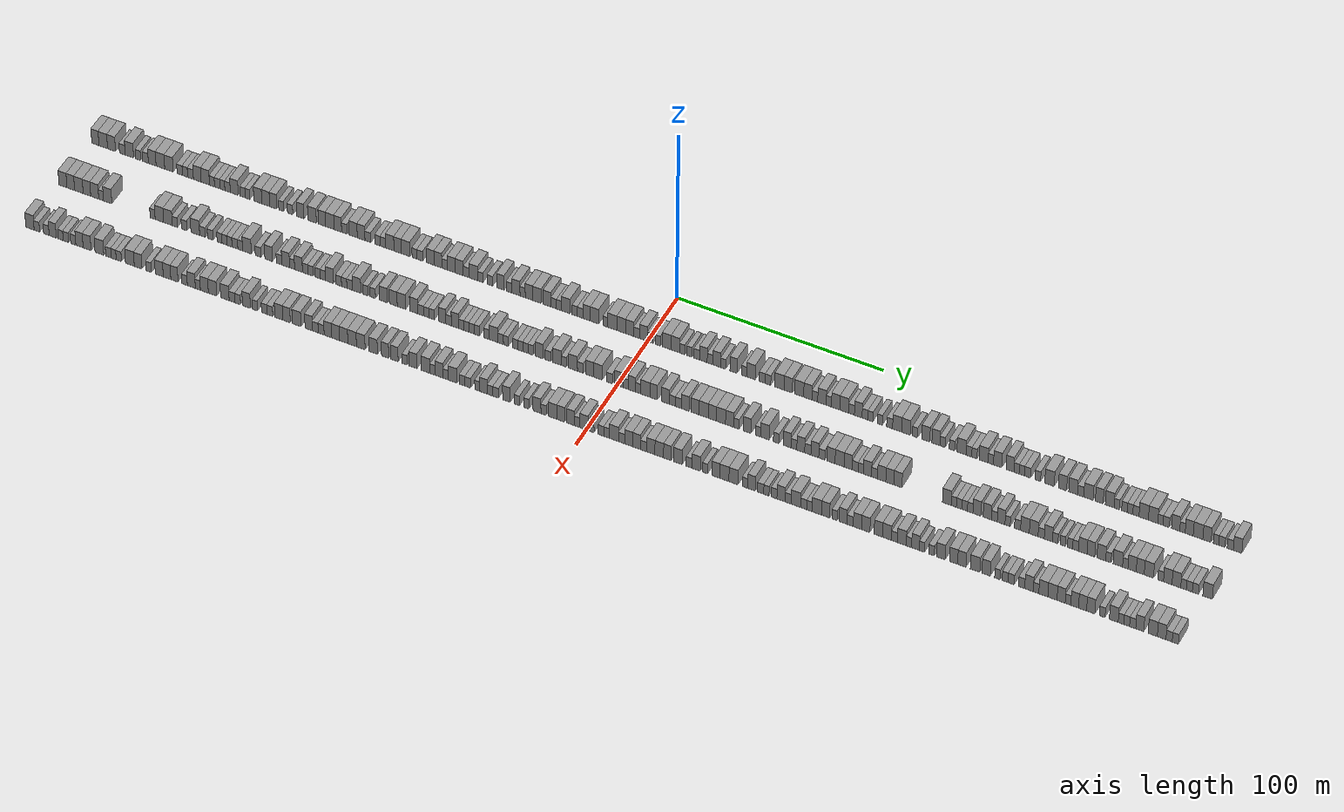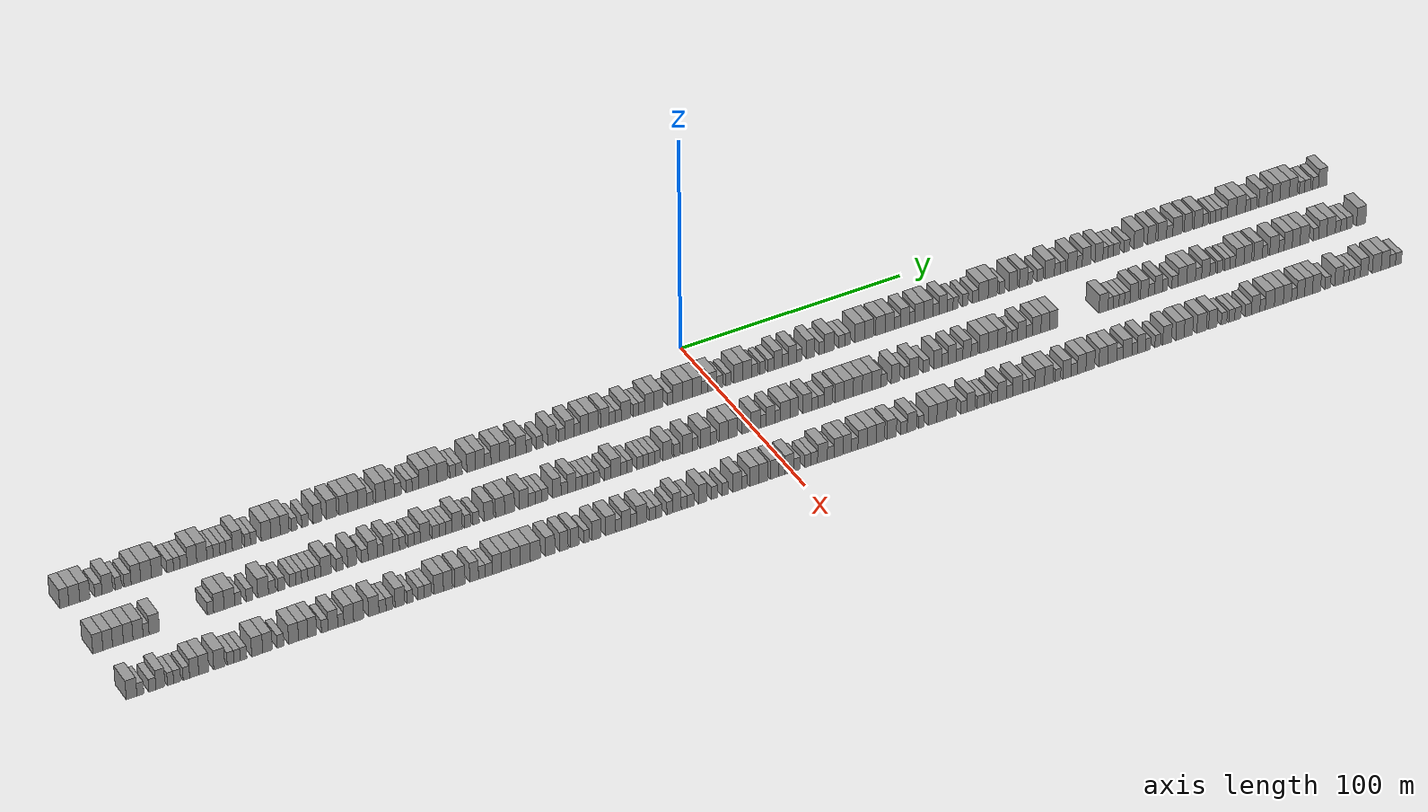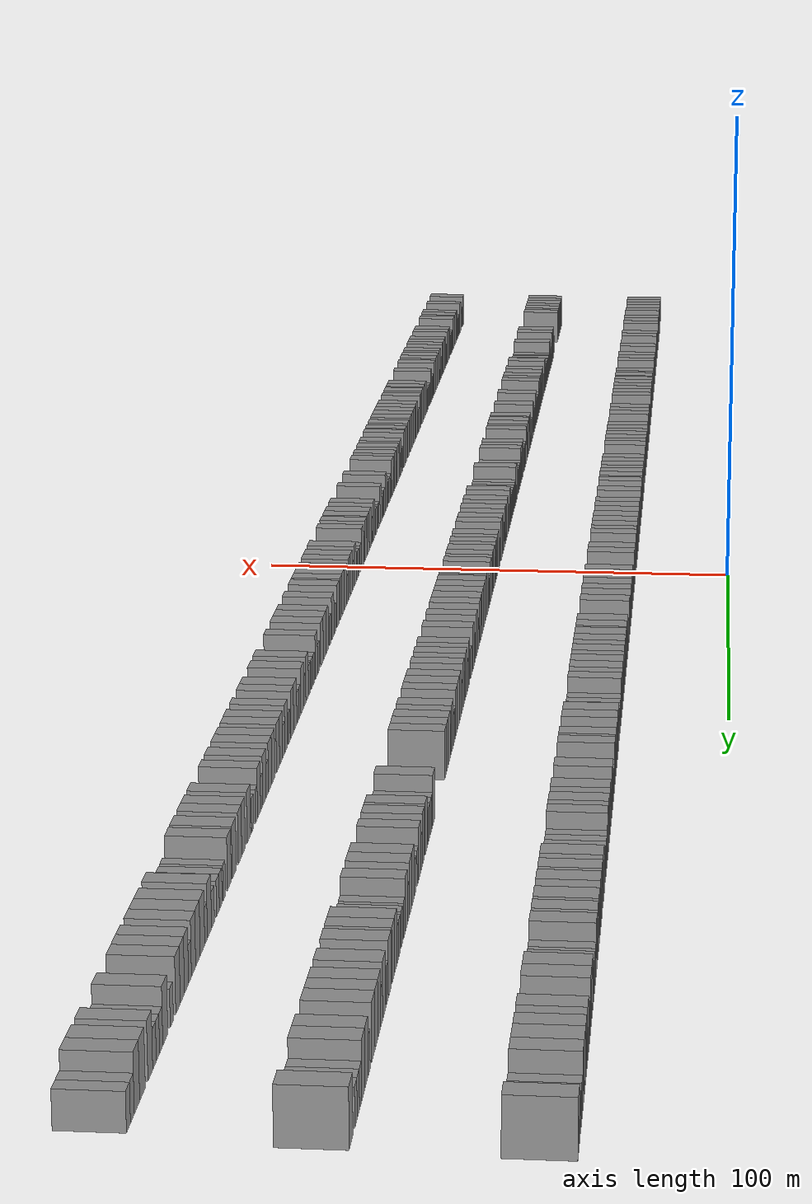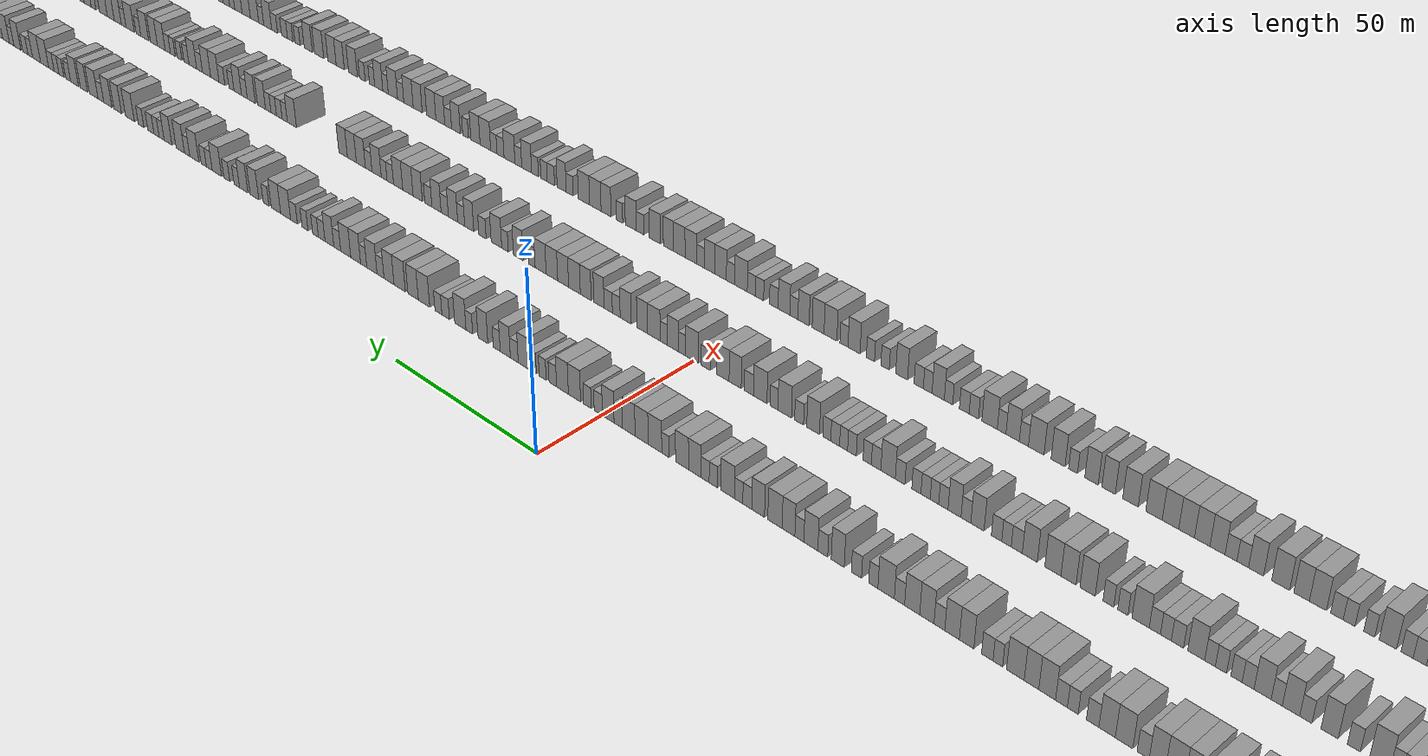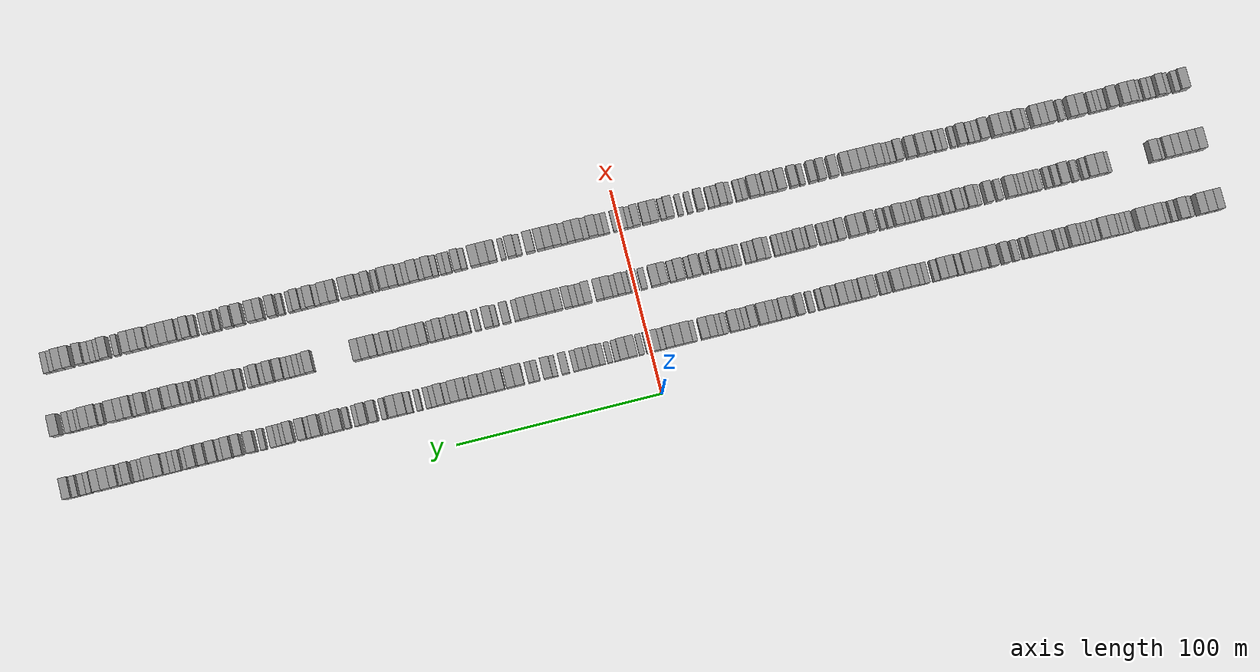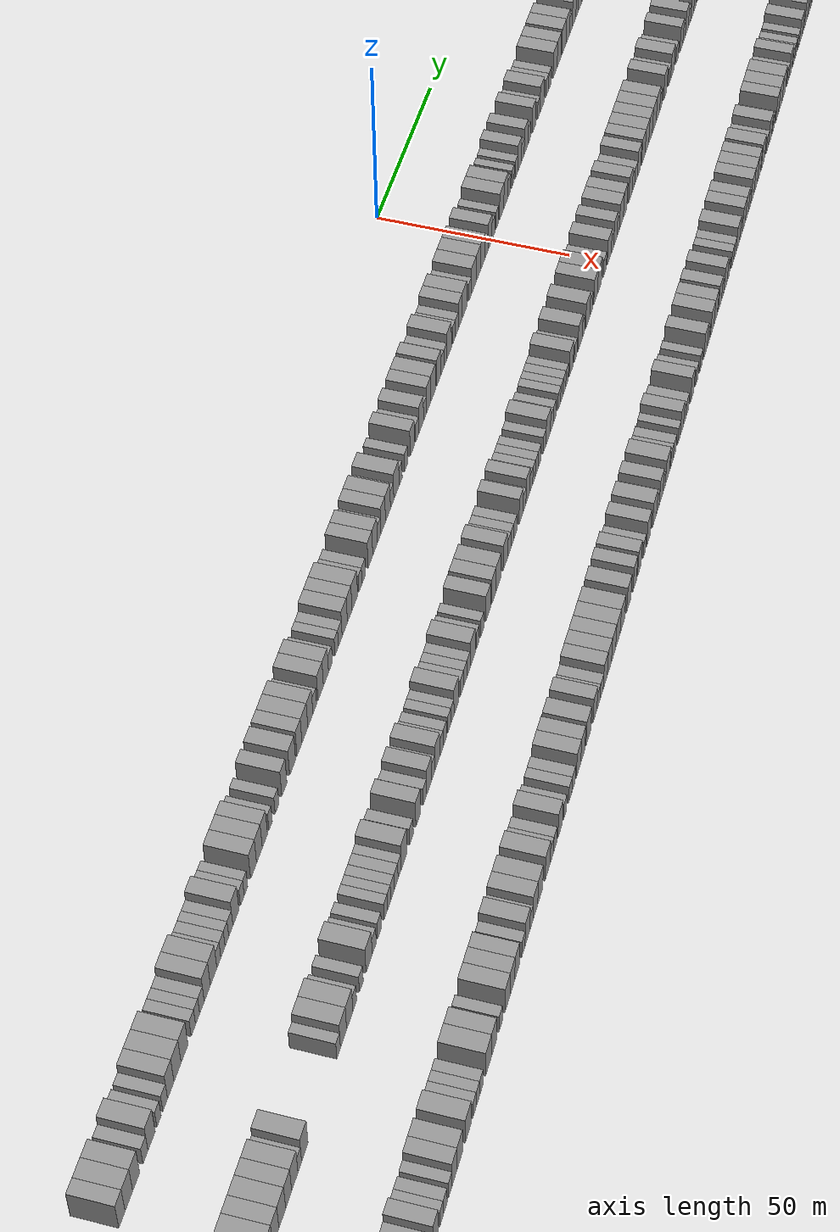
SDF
<sdf version="1.6">
 <world name="default">
  <scene>
   <sky><clouds><speed>12</speed></clouds></sky>
   <ambient>0.4 0.4 0.4 1</ambient>
   <background>0.7 0.7 0.7 1</background>
   <shadows>1</shadows>
  </scene>
  <gravity>0 0 -9.8066</gravity>
  <magnetic_field>6e-06 2.3e-05 -4.2e-05</magnetic_field>
  <physics default="0" name="default_physics" type="ode">
   <ode>
    <solver>
     <type>quick</type>
     <iters>10</iters>
     <sor>1.0</sor>
     <use_dynamic_moi_rescaling>0</use_dynamic_moi_rescaling>
    </solver>
    <constraints>
     <cfm>0</cfm>
     <erp>0.2</erp>
     <contact_max_correcting_vel>100</contact_max_correcting_vel>
     <contact_surface_layer>0.001</contact_surface_layer>
    </constraints>
   </ode>
   <max_step_size>0.004</max_step_size>
   <real_time_factor>1</real_time_factor>
   <real_time_update_rate>250</real_time_update_rate>
  </physics>
  <light name="sun" type="directional">
   <pose>0 0 10 0 0 0</pose>
   <diffuse>0.8 0.8 0.8 1</diffuse>
   <specular>0.2 0.2 0.2 1</specular>
   <attenuation>
    <range>1000</range>
    <constant>0.9</constant>
    <linear>0.01</linear>
    <quadratic>0.001</quadratic>
   </attenuation>
   <direction>-0.5 0.1 -0.9</direction>
  </light>
  <model name="building_1">
   <static>1</static>
   <pose>25.0000 -278.1522 0 0.000000 0.000000 0.000000</pose>
   <link name="link">
    <pose>0 0 4.50 0 0 0</pose>
    <collision name="collision"><geometry><box><size>10.0000 3.6957 9.0000</size></box></geometry></collision>
    <visual name="visual">
     <cast_shadows>0</cast_shadows>
     <geometry><box><size>10.0000 3.6957 9.0000</size></box></geometry>
     <material>
      <script>
       <uri>model://grey_wall/materials/scripts</uri>
       <uri>model://grey_wall/materials/textures</uri>
       <name>vrc/grey_wall</name>
      </script>
     </material>
    </visual>
   </link>
  </model>
  <model name="building_2">
   <static>1</static>
   <pose>25.0000 -274.0733 0 0.000000 0.000000 0.000000</pose>
   <link name="link">
    <pose>0 0 4.50 0 0 0</pose>
    <collision name="collision"><geometry><box><size>10.0000 4.4621 9.0000</size></box></geometry></collision>
    <visual name="visual">
     <cast_shadows>0</cast_shadows>
     <geometry><box><size>10.0000 4.4621 9.0000</size></box></geometry>
     <material>
      <script>
       <uri>model://grey_wall/materials/scripts</uri>
       <uri>model://grey_wall/materials/textures</uri>
       <name>vrc/grey_wall</name>
      </script>
     </material>
    </visual>
   </link>
  </model>
  <model name="building_3">
   <static>1</static>
   <pose>25.0000 -269.7885 0 0.000000 0.000000 0.000000</pose>
   <link name="link">
    <pose>0 0 4.50 0 0 0</pose>
    <collision name="collision"><geometry><box><size>10.0000 4.1075 9.0000</size></box></geometry></collision>
    <visual name="visual">
     <cast_shadows>0</cast_shadows>
     <geometry><box><size>10.0000 4.1075 9.0000</size></box></geometry>
     <material>
      <script>
       <uri>model://grey_wall/materials/scripts</uri>
       <uri>model://grey_wall/materials/textures</uri>
       <name>vrc/grey_wall</name>
      </script>
     </material>
    </visual>
   </link>
  </model>
  <model name="building_4">
   <static>1</static>
   <pose>25.0000 -264.2511 0 0.000000 0.000000 0.000000</pose>
   <link name="link">
    <pose>0 0 3.00 0 0 0</pose>
    <collision name="collision"><geometry><box><size>10.0000 2.9672 6.0000</size></box></geometry></collision>
    <visual name="visual">
     <cast_shadows>0</cast_shadows>
     <geometry><box><size>10.0000 2.9672 6.0000</size></box></geometry>
     <material>
      <script>
       <uri>model://grey_wall/materials/scripts</uri>
       <uri>model://grey_wall/materials/textures</uri>
       <name>vrc/grey_wall</name>
      </script>
     </material>
    </visual>
   </link>
  </model>
  <model name="building_5">
   <static>1</static>
   <pose>25.0000 -260.5834 0 0.000000 0.000000 0.000000</pose>
   <link name="link">
    <pose>0 0 4.50 0 0 0</pose>
    <collision name="collision"><geometry><box><size>10.0000 4.3683 9.0000</size></box></geometry></collision>
    <visual name="visual">
     <cast_shadows>0</cast_shadows>
     <geometry><box><size>10.0000 4.3683 9.0000</size></box></geometry>
     <material>
      <script>
       <uri>model://grey_wall/materials/scripts</uri>
       <uri>model://grey_wall/materials/textures</uri>
       <name>vrc/grey_wall</name>
      </script>
     </material>
    </visual>
   </link>
  </model>
  <model name="building_6">
   <static>1</static>
   <pose>25.0000 -256.0788 0 0.000000 0.000000 0.000000</pose>
   <link name="link">
    <pose>0 0 3.00 0 0 0</pose>
    <collision name="collision"><geometry><box><size>10.0000 2.6410 6.0000</size></box></geometry></collision>
    <visual name="visual">
     <cast_shadows>0</cast_shadows>
     <geometry><box><size>10.0000 2.6410 6.0000</size></box></geometry>
     <material>
      <script>
       <uri>model://grey_wall/materials/scripts</uri>
       <uri>model://grey_wall/materials/textures</uri>
       <name>vrc/grey_wall</name>
      </script>
     </material>
    </visual>
   </link>
  </model>
  <model name="building_7">
   <static>1</static>
   <pose>25.0000 -252.2933 0 0.000000 0.000000 0.000000</pose>
   <link name="link">
    <pose>0 0 3.00 0 0 0</pose>
    <collision name="collision"><geometry><box><size>10.0000 2.9300 6.0000</size></box></geometry></collision>
    <visual name="visual">
     <cast_shadows>0</cast_shadows>
     <geometry><box><size>10.0000 2.9300 6.0000</size></box></geometry>
     <material>
      <script>
       <uri>model://grey_wall/materials/scripts</uri>
       <uri>model://grey_wall/materials/textures</uri>
       <name>vrc/grey_wall</name>
      </script>
     </material>
    </visual>
   </link>
  </model>
  <model name="building_8">
   <static>1</static>
   <pose>25.0000 -248.8521 0 0.000000 0.000000 0.000000</pose>
   <link name="link">
    <pose>0 0 4.50 0 0 0</pose>
    <collision name="collision"><geometry><box><size>10.0000 3.9522 9.0000</size></box></geometry></collision>
    <visual name="visual">
     <cast_shadows>0</cast_shadows>
     <geometry><box><size>10.0000 3.9522 9.0000</size></box></geometry>
     <material>
      <script>
       <uri>model://grey_wall/materials/scripts</uri>
       <uri>model://grey_wall/materials/textures</uri>
       <name>vrc/grey_wall</name>
      </script>
     </material>
    </visual>
   </link>
  </model>
  <model name="building_9">
   <static>1</static>
   <pose>25.0000 -244.6514 0 0.000000 0.000000 0.000000</pose>
   <link name="link">
    <pose>0 0 4.50 0 0 0</pose>
    <collision name="collision"><geometry><box><size>10.0000 4.4492 9.0000</size></box></geometry></collision>
    <visual name="visual">
     <cast_shadows>0</cast_shadows>
     <geometry><box><size>10.0000 4.4492 9.0000</size></box></geometry>
     <material>
      <script>
       <uri>model://grey_wall/materials/scripts</uri>
       <uri>model://grey_wall/materials/textures</uri>
       <name>vrc/grey_wall</name>
      </script>
     </material>
    </visual>
   </link>
  </model>
  <model name="building_10">
   <static>1</static>
   <pose>25.0000 -240.2662 0 0.000000 0.000000 0.000000</pose>
   <link name="link">
    <pose>0 0 4.50 0 0 0</pose>
    <collision name="collision"><geometry><box><size>10.0000 4.3212 9.0000</size></box></geometry></collision>
    <visual name="visual">
     <cast_shadows>0</cast_shadows>
     <geometry><box><size>10.0000 4.3212 9.0000</size></box></geometry>
     <material>
      <script>
       <uri>model://grey_wall/materials/scripts</uri>
       <uri>model://grey_wall/materials/textures</uri>
       <name>vrc/grey_wall</name>
      </script>
     </material>
    </visual>
   </link>
  </model>
  <model name="building_11">
   <static>1</static>
   <pose>25.0000 -234.7153 0 0.000000 0.000000 0.000000</pose>
   <link name="link">
    <pose>0 0 3.00 0 0 0</pose>
    <collision name="collision"><geometry><box><size>10.0000 2.7806 6.0000</size></box></geometry></collision>
    <visual name="visual">
     <cast_shadows>0</cast_shadows>
     <geometry><box><size>10.0000 2.7806 6.0000</size></box></geometry>
     <material>
      <script>
       <uri>model://grey_wall/materials/scripts</uri>
       <uri>model://grey_wall/materials/textures</uri>
       <name>vrc/grey_wall</name>
      </script>
     </material>
    </visual>
   </link>
  </model>
  <model name="building_12">
   <static>1</static>
   <pose>25.0000 -232.0040 0 0.000000 0.000000 0.000000</pose>
   <link name="link">
    <pose>0 0 3.00 0 0 0</pose>
    <collision name="collision"><geometry><box><size>10.0000 2.6419 6.0000</size></box></geometry></collision>
    <visual name="visual">
     <cast_shadows>0</cast_shadows>
     <geometry><box><size>10.0000 2.6419 6.0000</size></box></geometry>
     <material>
      <script>
       <uri>model://grey_wall/materials/scripts</uri>
       <uri>model://grey_wall/materials/textures</uri>
       <name>vrc/grey_wall</name>
      </script>
     </material>
    </visual>
   </link>
  </model>
  <model name="building_13">
   <static>1</static>
   <pose>25.0000 -229.2043 0 0.000000 0.000000 0.000000</pose>
   <link name="link">
    <pose>0 0 3.00 0 0 0</pose>
    <collision name="collision"><geometry><box><size>10.0000 2.9576 6.0000</size></box></geometry></collision>
    <visual name="visual">
     <cast_shadows>0</cast_shadows>
     <geometry><box><size>10.0000 2.9576 6.0000</size></box></geometry>
     <material>
      <script>
       <uri>model://grey_wall/materials/scripts</uri>
       <uri>model://grey_wall/materials/textures</uri>
       <name>vrc/grey_wall</name>
      </script>
     </material>
    </visual>
   </link>
  </model>
  <model name="building_14">
   <static>1</static>
   <pose>25.0000 -225.7431 0 0.000000 0.000000 0.000000</pose>
   <link name="link">
    <pose>0 0 4.50 0 0 0</pose>
    <collision name="collision"><geometry><box><size>10.0000 3.9648 9.0000</size></box></geometry></collision>
    <visual name="visual">
     <cast_shadows>0</cast_shadows>
     <geometry><box><size>10.0000 3.9648 9.0000</size></box></geometry>
     <material>
      <script>
       <uri>model://grey_wall/materials/scripts</uri>
       <uri>model://grey_wall/materials/textures</uri>
       <name>vrc/grey_wall</name>
      </script>
     </material>
    </visual>
   </link>
  </model>
  <model name="building_15">
   <static>1</static>
   <pose>25.0000 -221.6441 0 0.000000 0.000000 0.000000</pose>
   <link name="link">
    <pose>0 0 4.50 0 0 0</pose>
    <collision name="collision"><geometry><box><size>10.0000 4.2332 9.0000</size></box></geometry></collision>
    <visual name="visual">
     <cast_shadows>0</cast_shadows>
     <geometry><box><size>10.0000 4.2332 9.0000</size></box></geometry>
     <material>
      <script>
       <uri>model://grey_wall/materials/scripts</uri>
       <uri>model://grey_wall/materials/textures</uri>
       <name>vrc/grey_wall</name>
      </script>
     </material>
    </visual>
   </link>
  </model>
  <model name="building_16">
   <static>1</static>
   <pose>25.0000 -218.2289 0 0.000000 0.000000 0.000000</pose>
   <link name="link">
    <pose>0 0 3.00 0 0 0</pose>
    <collision name="collision"><geometry><box><size>10.0000 2.5972 6.0000</size></box></geometry></collision>
    <visual name="visual">
     <cast_shadows>0</cast_shadows>
     <geometry><box><size>10.0000 2.5972 6.0000</size></box></geometry>
     <material>
      <script>
       <uri>model://grey_wall/materials/scripts</uri>
       <uri>model://grey_wall/materials/textures</uri>
       <name>vrc/grey_wall</name>
      </script>
     </material>
    </visual>
   </link>
  </model>
  <model name="building_17">
   <static>1</static>
   <pose>25.0000 -215.5340 0 0.000000 0.000000 0.000000</pose>
   <link name="link">
    <pose>0 0 3.00 0 0 0</pose>
    <collision name="collision"><geometry><box><size>10.0000 2.7925 6.0000</size></box></geometry></collision>
    <visual name="visual">
     <cast_shadows>0</cast_shadows>
     <geometry><box><size>10.0000 2.7925 6.0000</size></box></geometry>
     <material>
      <script>
       <uri>model://grey_wall/materials/scripts</uri>
       <uri>model://grey_wall/materials/textures</uri>
       <name>vrc/grey_wall</name>
      </script>
     </material>
    </visual>
   </link>
  </model>
  <model name="building_18">
   <static>1</static>
   <pose>25.0000 -212.8991 0 0.000000 0.000000 0.000000</pose>
   <link name="link">
    <pose>0 0 3.00 0 0 0</pose>
    <collision name="collision"><geometry><box><size>10.0000 2.4773 6.0000</size></box></geometry></collision>
    <visual name="visual">
     <cast_shadows>0</cast_shadows>
     <geometry><box><size>10.0000 2.4773 6.0000</size></box></geometry>
     <material>
      <script>
       <uri>model://grey_wall/materials/scripts</uri>
       <uri>model://grey_wall/materials/textures</uri>
       <name>vrc/grey_wall</name>
      </script>
     </material>
    </visual>
   </link>
  </model>
  <model name="building_19">
   <static>1</static>
   <pose>25.0000 -210.2767 0 0.000000 0.000000 0.000000</pose>
   <link name="link">
    <pose>0 0 3.00 0 0 0</pose>
    <collision name="collision"><geometry><box><size>10.0000 2.7677 6.0000</size></box></geometry></collision>
    <visual name="visual">
     <cast_shadows>0</cast_shadows>
     <geometry><box><size>10.0000 2.7677 6.0000</size></box></geometry>
     <material>
      <script>
       <uri>model://grey_wall/materials/scripts</uri>
       <uri>model://grey_wall/materials/textures</uri>
       <name>vrc/grey_wall</name>
      </script>
     </material>
    </visual>
   </link>
  </model>
  <model name="building_20">
   <static>1</static>
   <pose>25.0000 -206.8603 0 0.000000 0.000000 0.000000</pose>
   <link name="link">
    <pose>0 0 4.50 0 0 0</pose>
    <collision name="collision"><geometry><box><size>10.0000 4.0650 9.0000</size></box></geometry></collision>
    <visual name="visual">
     <cast_shadows>0</cast_shadows>
     <geometry><box><size>10.0000 4.0650 9.0000</size></box></geometry>
     <material>
      <script>
       <uri>model://grey_wall/materials/scripts</uri>
       <uri>model://grey_wall/materials/textures</uri>
       <name>vrc/grey_wall</name>
      </script>
     </material>
    </visual>
   </link>
  </model>
  <model name="building_21">
   <static>1</static>
   <pose>25.0000 -202.5629 0 0.000000 0.000000 0.000000</pose>
   <link name="link">
    <pose>0 0 3.00 0 0 0</pose>
    <collision name="collision"><geometry><box><size>10.0000 2.5299 6.0000</size></box></geometry></collision>
    <visual name="visual">
     <cast_shadows>0</cast_shadows>
     <geometry><box><size>10.0000 2.5299 6.0000</size></box></geometry>
     <material>
      <script>
       <uri>model://grey_wall/materials/scripts</uri>
       <uri>model://grey_wall/materials/textures</uri>
       <name>vrc/grey_wall</name>
      </script>
     </material>
    </visual>
   </link>
  </model>
  <model name="building_22">
   <static>1</static>
   <pose>25.0000 -200.0885 0 0.000000 0.000000 0.000000</pose>
   <link name="link">
    <pose>0 0 3.00 0 0 0</pose>
    <collision name="collision"><geometry><box><size>10.0000 2.4189 6.0000</size></box></geometry></collision>
    <visual name="visual">
     <cast_shadows>0</cast_shadows>
     <geometry><box><size>10.0000 2.4189 6.0000</size></box></geometry>
     <material>
      <script>
       <uri>model://grey_wall/materials/scripts</uri>
       <uri>model://grey_wall/materials/textures</uri>
       <name>vrc/grey_wall</name>
      </script>
     </material>
    </visual>
   </link>
  </model>
  <model name="building_23">
   <static>1</static>
   <pose>25.0000 -194.8447 0 0.000000 0.000000 0.000000</pose>
   <link name="link">
    <pose>0 0 4.50 0 0 0</pose>
    <collision name="collision"><geometry><box><size>10.0000 4.0688 9.0000</size></box></geometry></collision>
    <visual name="visual">
     <cast_shadows>0</cast_shadows>
     <geometry><box><size>10.0000 4.0688 9.0000</size></box></geometry>
     <material>
      <script>
       <uri>model://grey_wall/materials/scripts</uri>
       <uri>model://grey_wall/materials/textures</uri>
       <name>vrc/grey_wall</name>
      </script>
     </material>
    </visual>
   </link>
  </model>
  <model name="building_24">
   <static>1</static>
   <pose>25.0000 -190.8185 0 0.000000 0.000000 0.000000</pose>
   <link name="link">
    <pose>0 0 4.50 0 0 0</pose>
    <collision name="collision"><geometry><box><size>10.0000 3.9835 9.0000</size></box></geometry></collision>
    <visual name="visual">
     <cast_shadows>0</cast_shadows>
     <geometry><box><size>10.0000 3.9835 9.0000</size></box></geometry>
     <material>
      <script>
       <uri>model://grey_wall/materials/scripts</uri>
       <uri>model://grey_wall/materials/textures</uri>
       <name>vrc/grey_wall</name>
      </script>
     </material>
    </visual>
   </link>
  </model>
  <model name="building_25">
   <static>1</static>
   <pose>25.0000 -187.0232 0 0.000000 0.000000 0.000000</pose>
   <link name="link">
    <pose>0 0 4.50 0 0 0</pose>
    <collision name="collision"><geometry><box><size>10.0000 3.6071 9.0000</size></box></geometry></collision>
    <visual name="visual">
     <cast_shadows>0</cast_shadows>
     <geometry><box><size>10.0000 3.6071 9.0000</size></box></geometry>
     <material>
      <script>
       <uri>model://grey_wall/materials/scripts</uri>
       <uri>model://grey_wall/materials/textures</uri>
       <name>vrc/grey_wall</name>
      </script>
     </material>
    </visual>
   </link>
  </model>
  <model name="building_26">
   <static>1</static>
   <pose>25.0000 -183.0187 0 0.000000 0.000000 0.000000</pose>
   <link name="link">
    <pose>0 0 3.00 0 0 0</pose>
    <collision name="collision"><geometry><box><size>10.0000 2.4019 6.0000</size></box></geometry></collision>
    <visual name="visual">
     <cast_shadows>0</cast_shadows>
     <geometry><box><size>10.0000 2.4019 6.0000</size></box></geometry>
     <material>
      <script>
       <uri>model://grey_wall/materials/scripts</uri>
       <uri>model://grey_wall/materials/textures</uri>
       <name>vrc/grey_wall</name>
      </script>
     </material>
    </visual>
   </link>
  </model>
  <model name="building_27">
   <static>1</static>
   <pose>25.0000 -178.4467 0 0.000000 0.000000 0.000000</pose>
   <link name="link">
    <pose>0 0 3.00 0 0 0</pose>
    <collision name="collision"><geometry><box><size>10.0000 2.7422 6.0000</size></box></geometry></collision>
    <visual name="visual">
     <cast_shadows>0</cast_shadows>
     <geometry><box><size>10.0000 2.7422 6.0000</size></box></geometry>
     <material>
      <script>
       <uri>model://grey_wall/materials/scripts</uri>
       <uri>model://grey_wall/materials/textures</uri>
       <name>vrc/grey_wall</name>
      </script>
     </material>
    </visual>
   </link>
  </model>
  <model name="building_28">
   <static>1</static>
   <pose>25.0000 -173.2510 0 0.000000 0.000000 0.000000</pose>
   <link name="link">
    <pose>0 0 4.50 0 0 0</pose>
    <collision name="collision"><geometry><box><size>10.0000 3.6491 9.0000</size></box></geometry></collision>
    <visual name="visual">
     <cast_shadows>0</cast_shadows>
     <geometry><box><size>10.0000 3.6491 9.0000</size></box></geometry>
     <material>
      <script>
       <uri>model://grey_wall/materials/scripts</uri>
       <uri>model://grey_wall/materials/textures</uri>
       <name>vrc/grey_wall</name>
      </script>
     </material>
    </visual>
   </link>
  </model>
  <model name="building_29">
   <static>1</static>
   <pose>25.0000 -167.2839 0 0.000000 0.000000 0.000000</pose>
   <link name="link">
    <pose>0 0 4.50 0 0 0</pose>
    <collision name="collision"><geometry><box><size>10.0000 4.2852 9.0000</size></box></geometry></collision>
    <visual name="visual">
     <cast_shadows>0</cast_shadows>
     <geometry><box><size>10.0000 4.2852 9.0000</size></box></geometry>
     <material>
      <script>
       <uri>model://grey_wall/materials/scripts</uri>
       <uri>model://grey_wall/materials/textures</uri>
       <name>vrc/grey_wall</name>
      </script>
     </material>
    </visual>
   </link>
  </model>
  <model name="building_30">
   <static>1</static>
   <pose>25.0000 -162.3185 0 0.000000 0.000000 0.000000</pose>
   <link name="link">
    <pose>0 0 4.50 0 0 0</pose>
    <collision name="collision"><geometry><box><size>10.0000 3.6455 9.0000</size></box></geometry></collision>
    <visual name="visual">
     <cast_shadows>0</cast_shadows>
     <geometry><box><size>10.0000 3.6455 9.0000</size></box></geometry>
     <material>
      <script>
       <uri>model://grey_wall/materials/scripts</uri>
       <uri>model://grey_wall/materials/textures</uri>
       <name>vrc/grey_wall</name>
      </script>
     </material>
    </visual>
   </link>
  </model>
  <model name="building_31">
   <static>1</static>
   <pose>25.0000 -158.3245 0 0.000000 0.000000 0.000000</pose>
   <link name="link">
    <pose>0 0 4.50 0 0 0</pose>
    <collision name="collision"><geometry><box><size>10.0000 4.3426 9.0000</size></box></geometry></collision>
    <visual name="visual">
     <cast_shadows>0</cast_shadows>
     <geometry><box><size>10.0000 4.3426 9.0000</size></box></geometry>
     <material>
      <script>
       <uri>model://grey_wall/materials/scripts</uri>
       <uri>model://grey_wall/materials/textures</uri>
       <name>vrc/grey_wall</name>
      </script>
     </material>
    </visual>
   </link>
  </model>
  <model name="building_32">
   <static>1</static>
   <pose>25.0000 -154.2778 0 0.000000 0.000000 0.000000</pose>
   <link name="link">
    <pose>0 0 4.50 0 0 0</pose>
    <collision name="collision"><geometry><box><size>10.0000 3.7507 9.0000</size></box></geometry></collision>
    <visual name="visual">
     <cast_shadows>0</cast_shadows>
     <geometry><box><size>10.0000 3.7507 9.0000</size></box></geometry>
     <material>
      <script>
       <uri>model://grey_wall/materials/scripts</uri>
       <uri>model://grey_wall/materials/textures</uri>
       <name>vrc/grey_wall</name>
      </script>
     </material>
    </visual>
   </link>
  </model>
  <model name="building_33">
   <static>1</static>
   <pose>25.0000 -151.0073 0 0.000000 0.000000 0.000000</pose>
   <link name="link">
    <pose>0 0 3.00 0 0 0</pose>
    <collision name="collision"><geometry><box><size>10.0000 2.7904 6.0000</size></box></geometry></collision>
    <visual name="visual">
     <cast_shadows>0</cast_shadows>
     <geometry><box><size>10.0000 2.7904 6.0000</size></box></geometry>
     <material>
      <script>
       <uri>model://grey_wall/materials/scripts</uri>
       <uri>model://grey_wall/materials/textures</uri>
       <name>vrc/grey_wall</name>
      </script>
     </material>
    </visual>
   </link>
  </model>
  <model name="building_34">
   <static>1</static>
   <pose>25.0000 -146.5571 0 0.000000 0.000000 0.000000</pose>
   <link name="link">
    <pose>0 0 4.50 0 0 0</pose>
    <collision name="collision"><geometry><box><size>10.0000 4.1099 9.0000</size></box></geometry></collision>
    <visual name="visual">
     <cast_shadows>0</cast_shadows>
     <geometry><box><size>10.0000 4.1099 9.0000</size></box></geometry>
     <material>
      <script>
       <uri>model://grey_wall/materials/scripts</uri>
       <uri>model://grey_wall/materials/textures</uri>
       <name>vrc/grey_wall</name>
      </script>
     </material>
    </visual>
   </link>
  </model>
  <model name="building_35">
   <static>1</static>
   <pose>25.0000 -142.5649 0 0.000000 0.000000 0.000000</pose>
   <link name="link">
    <pose>0 0 4.50 0 0 0</pose>
    <collision name="collision"><geometry><box><size>10.0000 3.8745 9.0000</size></box></geometry></collision>
    <visual name="visual">
     <cast_shadows>0</cast_shadows>
     <geometry><box><size>10.0000 3.8745 9.0000</size></box></geometry>
     <material>
      <script>
       <uri>model://grey_wall/materials/scripts</uri>
       <uri>model://grey_wall/materials/textures</uri>
       <name>vrc/grey_wall</name>
      </script>
     </material>
    </visual>
   </link>
  </model>
  <model name="building_36">
   <static>1</static>
   <pose>25.0000 -139.1422 0 0.000000 0.000000 0.000000</pose>
   <link name="link">
    <pose>0 0 3.00 0 0 0</pose>
    <collision name="collision"><geometry><box><size>10.0000 2.9710 6.0000</size></box></geometry></collision>
    <visual name="visual">
     <cast_shadows>0</cast_shadows>
     <geometry><box><size>10.0000 2.9710 6.0000</size></box></geometry>
     <material>
      <script>
       <uri>model://grey_wall/materials/scripts</uri>
       <uri>model://grey_wall/materials/textures</uri>
       <name>vrc/grey_wall</name>
      </script>
     </material>
    </visual>
   </link>
  </model>
  <model name="building_37">
   <static>1</static>
   <pose>25.0000 -134.3586 0 0.000000 0.000000 0.000000</pose>
   <link name="link">
    <pose>0 0 3.00 0 0 0</pose>
    <collision name="collision"><geometry><box><size>10.0000 2.5962 6.0000</size></box></geometry></collision>
    <visual name="visual">
     <cast_shadows>0</cast_shadows>
     <geometry><box><size>10.0000 2.5962 6.0000</size></box></geometry>
     <material>
      <script>
       <uri>model://grey_wall/materials/scripts</uri>
       <uri>model://grey_wall/materials/textures</uri>
       <name>vrc/grey_wall</name>
      </script>
     </material>
    </visual>
   </link>
  </model>
  <model name="building_38">
   <static>1</static>
   <pose>25.0000 -131.6134 0 0.000000 0.000000 0.000000</pose>
   <link name="link">
    <pose>0 0 3.00 0 0 0</pose>
    <collision name="collision"><geometry><box><size>10.0000 2.8944 6.0000</size></box></geometry></collision>
    <visual name="visual">
     <cast_shadows>0</cast_shadows>
     <geometry><box><size>10.0000 2.8944 6.0000</size></box></geometry>
     <material>
      <script>
       <uri>model://grey_wall/materials/scripts</uri>
       <uri>model://grey_wall/materials/textures</uri>
       <name>vrc/grey_wall</name>
      </script>
     </material>
    </visual>
   </link>
  </model>
  <model name="building_39">
   <static>1</static>
   <pose>25.0000 -128.1045 0 0.000000 0.000000 0.000000</pose>
   <link name="link">
    <pose>0 0 4.50 0 0 0</pose>
    <collision name="collision"><geometry><box><size>10.0000 4.1233 9.0000</size></box></geometry></collision>
    <visual name="visual">
     <cast_shadows>0</cast_shadows>
     <geometry><box><size>10.0000 4.1233 9.0000</size></box></geometry>
     <material>
      <script>
       <uri>model://grey_wall/materials/scripts</uri>
       <uri>model://grey_wall/materials/textures</uri>
       <name>vrc/grey_wall</name>
      </script>
     </material>
    </visual>
   </link>
  </model>
  <model name="building_40">
   <static>1</static>
   <pose>25.0000 -124.2351 0 0.000000 0.000000 0.000000</pose>
   <link name="link">
    <pose>0 0 4.50 0 0 0</pose>
    <collision name="collision"><geometry><box><size>10.0000 3.6154 9.0000</size></box></geometry></collision>
    <visual name="visual">
     <cast_shadows>0</cast_shadows>
     <geometry><box><size>10.0000 3.6154 9.0000</size></box></geometry>
     <material>
      <script>
       <uri>model://grey_wall/materials/scripts</uri>
       <uri>model://grey_wall/materials/textures</uri>
       <name>vrc/grey_wall</name>
      </script>
     </material>
    </visual>
   </link>
  </model>
  <model name="building_41">
   <static>1</static>
   <pose>25.0000 -120.2014 0 0.000000 0.000000 0.000000</pose>
   <link name="link">
    <pose>0 0 4.50 0 0 0</pose>
    <collision name="collision"><geometry><box><size>10.0000 4.4520 9.0000</size></box></geometry></collision>
    <visual name="visual">
     <cast_shadows>0</cast_shadows>
     <geometry><box><size>10.0000 4.4520 9.0000</size></box></geometry>
     <material>
      <script>
       <uri>model://grey_wall/materials/scripts</uri>
       <uri>model://grey_wall/materials/textures</uri>
       <name>vrc/grey_wall</name>
      </script>
     </material>
    </visual>
   </link>
  </model>
  <model name="building_42">
   <static>1</static>
   <pose>25.0000 -115.7638 0 0.000000 0.000000 0.000000</pose>
   <link name="link">
    <pose>0 0 3.00 0 0 0</pose>
    <collision name="collision"><geometry><box><size>10.0000 2.4232 6.0000</size></box></geometry></collision>
    <visual name="visual">
     <cast_shadows>0</cast_shadows>
     <geometry><box><size>10.0000 2.4232 6.0000</size></box></geometry>
     <material>
      <script>
       <uri>model://grey_wall/materials/scripts</uri>
       <uri>model://grey_wall/materials/textures</uri>
       <name>vrc/grey_wall</name>
      </script>
     </material>
    </visual>
   </link>
  </model>
  <model name="building_43">
   <static>1</static>
   <pose>25.0000 -113.0874 0 0.000000 0.000000 0.000000</pose>
   <link name="link">
    <pose>0 0 3.00 0 0 0</pose>
    <collision name="collision"><geometry><box><size>10.0000 2.9295 6.0000</size></box></geometry></collision>
    <visual name="visual">
     <cast_shadows>0</cast_shadows>
     <geometry><box><size>10.0000 2.9295 6.0000</size></box></geometry>
     <material>
      <script>
       <uri>model://grey_wall/materials/scripts</uri>
       <uri>model://grey_wall/materials/textures</uri>
       <name>vrc/grey_wall</name>
      </script>
     </material>
    </visual>
   </link>
  </model>
  <model name="building_44">
   <static>1</static>
   <pose>25.0000 -107.7457 0 0.000000 0.000000 0.000000</pose>
   <link name="link">
    <pose>0 0 4.50 0 0 0</pose>
    <collision name="collision"><geometry><box><size>10.0000 3.7540 9.0000</size></box></geometry></collision>
    <visual name="visual">
     <cast_shadows>0</cast_shadows>
     <geometry><box><size>10.0000 3.7540 9.0000</size></box></geometry>
     <material>
      <script>
       <uri>model://grey_wall/materials/scripts</uri>
       <uri>model://grey_wall/materials/textures</uri>
       <name>vrc/grey_wall</name>
      </script>
     </material>
    </visual>
   </link>
  </model>
  <model name="building_45">
   <static>1</static>
   <pose>25.0000 -103.9578 0 0.000000 0.000000 0.000000</pose>
   <link name="link">
    <pose>0 0 4.50 0 0 0</pose>
    <collision name="collision"><geometry><box><size>10.0000 3.8217 9.0000</size></box></geometry></collision>
    <visual name="visual">
     <cast_shadows>0</cast_shadows>
     <geometry><box><size>10.0000 3.8217 9.0000</size></box></geometry>
     <material>
      <script>
       <uri>model://grey_wall/materials/scripts</uri>
       <uri>model://grey_wall/materials/textures</uri>
       <name>vrc/grey_wall</name>
      </script>
     </material>
    </visual>
   </link>
  </model>
  <model name="building_46">
   <static>1</static>
   <pose>25.0000 -100.6220 0 0.000000 0.000000 0.000000</pose>
   <link name="link">
    <pose>0 0 3.00 0 0 0</pose>
    <collision name="collision"><geometry><box><size>10.0000 2.8498 6.0000</size></box></geometry></collision>
    <visual name="visual">
     <cast_shadows>0</cast_shadows>
     <geometry><box><size>10.0000 2.8498 6.0000</size></box></geometry>
     <material>
      <script>
       <uri>model://grey_wall/materials/scripts</uri>
       <uri>model://grey_wall/materials/textures</uri>
       <name>vrc/grey_wall</name>
      </script>
     </material>
    </visual>
   </link>
  </model>
  <model name="building_47">
   <static>1</static>
   <pose>25.0000 -97.2985 0 0.000000 0.000000 0.000000</pose>
   <link name="link">
    <pose>0 0 4.50 0 0 0</pose>
    <collision name="collision"><geometry><box><size>10.0000 3.7972 9.0000</size></box></geometry></collision>
    <visual name="visual">
     <cast_shadows>0</cast_shadows>
     <geometry><box><size>10.0000 3.7972 9.0000</size></box></geometry>
     <material>
      <script>
       <uri>model://grey_wall/materials/scripts</uri>
       <uri>model://grey_wall/materials/textures</uri>
       <name>vrc/grey_wall</name>
      </script>
     </material>
    </visual>
   </link>
  </model>
  <model name="building_48">
   <static>1</static>
   <pose>25.0000 -93.3656 0 0.000000 0.000000 0.000000</pose>
   <link name="link">
    <pose>0 0 4.50 0 0 0</pose>
    <collision name="collision"><geometry><box><size>10.0000 4.0687 9.0000</size></box></geometry></collision>
    <visual name="visual">
     <cast_shadows>0</cast_shadows>
     <geometry><box><size>10.0000 4.0687 9.0000</size></box></geometry>
     <material>
      <script>
       <uri>model://grey_wall/materials/scripts</uri>
       <uri>model://grey_wall/materials/textures</uri>
       <name>vrc/grey_wall</name>
      </script>
     </material>
    </visual>
   </link>
  </model>
  <model name="building_49">
   <static>1</static>
   <pose>25.0000 -89.9338 0 0.000000 0.000000 0.000000</pose>
   <link name="link">
    <pose>0 0 3.00 0 0 0</pose>
    <collision name="collision"><geometry><box><size>10.0000 2.7948 6.0000</size></box></geometry></collision>
    <visual name="visual">
     <cast_shadows>0</cast_shadows>
     <geometry><box><size>10.0000 2.7948 6.0000</size></box></geometry>
     <material>
      <script>
       <uri>model://grey_wall/materials/scripts</uri>
       <uri>model://grey_wall/materials/textures</uri>
       <name>vrc/grey_wall</name>
      </script>
     </material>
    </visual>
   </link>
  </model>
  <model name="building_50">
   <static>1</static>
   <pose>25.0000 -86.2893 0 0.000000 0.000000 0.000000</pose>
   <link name="link">
    <pose>0 0 4.50 0 0 0</pose>
    <collision name="collision"><geometry><box><size>10.0000 4.4942 9.0000</size></box></geometry></collision>
    <visual name="visual">
     <cast_shadows>0</cast_shadows>
     <geometry><box><size>10.0000 4.4942 9.0000</size></box></geometry>
     <material>
      <script>
       <uri>model://grey_wall/materials/scripts</uri>
       <uri>model://grey_wall/materials/textures</uri>
       <name>vrc/grey_wall</name>
      </script>
     </material>
    </visual>
   </link>
  </model>
  <model name="building_51">
   <static>1</static>
   <pose>25.0000 -82.7685 0 0.000000 0.000000 0.000000</pose>
   <link name="link">
    <pose>0 0 3.00 0 0 0</pose>
    <collision name="collision"><geometry><box><size>10.0000 2.5475 6.0000</size></box></geometry></collision>
    <visual name="visual">
     <cast_shadows>0</cast_shadows>
     <geometry><box><size>10.0000 2.5475 6.0000</size></box></geometry>
     <material>
      <script>
       <uri>model://grey_wall/materials/scripts</uri>
       <uri>model://grey_wall/materials/textures</uri>
       <name>vrc/grey_wall</name>
      </script>
     </material>
    </visual>
   </link>
  </model>
  <model name="building_52">
   <static>1</static>
   <pose>25.0000 -78.0742 0 0.000000 0.000000 0.000000</pose>
   <link name="link">
    <pose>0 0 3.00 0 0 0</pose>
    <collision name="collision"><geometry><box><size>10.0000 2.8412 6.0000</size></box></geometry></collision>
    <visual name="visual">
     <cast_shadows>0</cast_shadows>
     <geometry><box><size>10.0000 2.8412 6.0000</size></box></geometry>
     <material>
      <script>
       <uri>model://grey_wall/materials/scripts</uri>
       <uri>model://grey_wall/materials/textures</uri>
       <name>vrc/grey_wall</name>
      </script>
     </material>
    </visual>
   </link>
  </model>
  <model name="building_53">
   <static>1</static>
   <pose>25.0000 -72.8111 0 0.000000 0.000000 0.000000</pose>
   <link name="link">
    <pose>0 0 4.50 0 0 0</pose>
    <collision name="collision"><geometry><box><size>10.0000 3.6848 9.0000</size></box></geometry></collision>
    <visual name="visual">
     <cast_shadows>0</cast_shadows>
     <geometry><box><size>10.0000 3.6848 9.0000</size></box></geometry>
     <material>
      <script>
       <uri>model://grey_wall/materials/scripts</uri>
       <uri>model://grey_wall/materials/textures</uri>
       <name>vrc/grey_wall</name>
      </script>
     </material>
    </visual>
   </link>
  </model>
  <model name="building_54">
   <static>1</static>
   <pose>25.0000 -68.5531 0 0.000000 0.000000 0.000000</pose>
   <link name="link">
    <pose>0 0 3.00 0 0 0</pose>
    <collision name="collision"><geometry><box><size>10.0000 2.8312 6.0000</size></box></geometry></collision>
    <visual name="visual">
     <cast_shadows>0</cast_shadows>
     <geometry><box><size>10.0000 2.8312 6.0000</size></box></geometry>
     <material>
      <script>
       <uri>model://grey_wall/materials/scripts</uri>
       <uri>model://grey_wall/materials/textures</uri>
       <name>vrc/grey_wall</name>
      </script>
     </material>
    </visual>
   </link>
  </model>
  <model name="building_55">
   <static>1</static>
   <pose>25.0000 -65.1235 0 0.000000 0.000000 0.000000</pose>
   <link name="link">
    <pose>0 0 4.50 0 0 0</pose>
    <collision name="collision"><geometry><box><size>10.0000 4.0279 9.0000</size></box></geometry></collision>
    <visual name="visual">
     <cast_shadows>0</cast_shadows>
     <geometry><box><size>10.0000 4.0279 9.0000</size></box></geometry>
     <material>
      <script>
       <uri>model://grey_wall/materials/scripts</uri>
       <uri>model://grey_wall/materials/textures</uri>
       <name>vrc/grey_wall</name>
      </script>
     </material>
    </visual>
   </link>
  </model>
  <model name="building_56">
   <static>1</static>
   <pose>25.0000 -61.8055 0 0.000000 0.000000 0.000000</pose>
   <link name="link">
    <pose>0 0 3.00 0 0 0</pose>
    <collision name="collision"><geometry><box><size>10.0000 2.6081 6.0000</size></box></geometry></collision>
    <visual name="visual">
     <cast_shadows>0</cast_shadows>
     <geometry><box><size>10.0000 2.6081 6.0000</size></box></geometry>
     <material>
      <script>
       <uri>model://grey_wall/materials/scripts</uri>
       <uri>model://grey_wall/materials/textures</uri>
       <name>vrc/grey_wall</name>
      </script>
     </material>
    </visual>
   </link>
  </model>
  <model name="building_57">
   <static>1</static>
   <pose>25.0000 -58.6286 0 0.000000 0.000000 0.000000</pose>
   <link name="link">
    <pose>0 0 4.50 0 0 0</pose>
    <collision name="collision"><geometry><box><size>10.0000 3.7456 9.0000</size></box></geometry></collision>
    <visual name="visual">
     <cast_shadows>0</cast_shadows>
     <geometry><box><size>10.0000 3.7456 9.0000</size></box></geometry>
     <material>
      <script>
       <uri>model://grey_wall/materials/scripts</uri>
       <uri>model://grey_wall/materials/textures</uri>
       <name>vrc/grey_wall</name>
      </script>
     </material>
    </visual>
   </link>
  </model>
  <model name="building_58">
   <static>1</static>
   <pose>25.0000 -54.6424 0 0.000000 0.000000 0.000000</pose>
   <link name="link">
    <pose>0 0 4.50 0 0 0</pose>
    <collision name="collision"><geometry><box><size>10.0000 4.2268 9.0000</size></box></geometry></collision>
    <visual name="visual">
     <cast_shadows>0</cast_shadows>
     <geometry><box><size>10.0000 4.2268 9.0000</size></box></geometry>
     <material>
      <script>
       <uri>model://grey_wall/materials/scripts</uri>
       <uri>model://grey_wall/materials/textures</uri>
       <name>vrc/grey_wall</name>
      </script>
     </material>
    </visual>
   </link>
  </model>
  <model name="building_59">
   <static>1</static>
   <pose>25.0000 -49.6313 0 0.000000 0.000000 0.000000</pose>
   <link name="link">
    <pose>0 0 4.50 0 0 0</pose>
    <collision name="collision"><geometry><box><size>10.0000 3.7955 9.0000</size></box></geometry></collision>
    <visual name="visual">
     <cast_shadows>0</cast_shadows>
     <geometry><box><size>10.0000 3.7955 9.0000</size></box></geometry>
     <material>
      <script>
       <uri>model://grey_wall/materials/scripts</uri>
       <uri>model://grey_wall/materials/textures</uri>
       <name>vrc/grey_wall</name>
      </script>
     </material>
    </visual>
   </link>
  </model>
  <model name="building_60">
   <static>1</static>
   <pose>25.0000 -46.3752 0 0.000000 0.000000 0.000000</pose>
   <link name="link">
    <pose>0 0 3.00 0 0 0</pose>
    <collision name="collision"><geometry><box><size>10.0000 2.7167 6.0000</size></box></geometry></collision>
    <visual name="visual">
     <cast_shadows>0</cast_shadows>
     <geometry><box><size>10.0000 2.7167 6.0000</size></box></geometry>
     <material>
      <script>
       <uri>model://grey_wall/materials/scripts</uri>
       <uri>model://grey_wall/materials/textures</uri>
       <name>vrc/grey_wall</name>
      </script>
     </material>
    </visual>
   </link>
  </model>
  <model name="building_61">
   <static>1</static>
   <pose>25.0000 -43.7608 0 0.000000 0.000000 0.000000</pose>
   <link name="link">
    <pose>0 0 3.00 0 0 0</pose>
    <collision name="collision"><geometry><box><size>10.0000 2.5121 6.0000</size></box></geometry></collision>
    <visual name="visual">
     <cast_shadows>0</cast_shadows>
     <geometry><box><size>10.0000 2.5121 6.0000</size></box></geometry>
     <material>
      <script>
       <uri>model://grey_wall/materials/scripts</uri>
       <uri>model://grey_wall/materials/textures</uri>
       <name>vrc/grey_wall</name>
      </script>
     </material>
    </visual>
   </link>
  </model>
  <model name="building_62">
   <static>1</static>
   <pose>25.0000 -40.3799 0 0.000000 0.000000 0.000000</pose>
   <link name="link">
    <pose>0 0 4.50 0 0 0</pose>
    <collision name="collision"><geometry><box><size>10.0000 4.2499 9.0000</size></box></geometry></collision>
    <visual name="visual">
     <cast_shadows>0</cast_shadows>
     <geometry><box><size>10.0000 4.2499 9.0000</size></box></geometry>
     <material>
      <script>
       <uri>model://grey_wall/materials/scripts</uri>
       <uri>model://grey_wall/materials/textures</uri>
       <name>vrc/grey_wall</name>
      </script>
     </material>
    </visual>
   </link>
  </model>
  <model name="building_63">
   <static>1</static>
   <pose>25.0000 -35.9774 0 0.000000 0.000000 0.000000</pose>
   <link name="link">
    <pose>0 0 3.00 0 0 0</pose>
    <collision name="collision"><geometry><box><size>10.0000 2.5551 6.0000</size></box></geometry></collision>
    <visual name="visual">
     <cast_shadows>0</cast_shadows>
     <geometry><box><size>10.0000 2.5551 6.0000</size></box></geometry>
     <material>
      <script>
       <uri>model://grey_wall/materials/scripts</uri>
       <uri>model://grey_wall/materials/textures</uri>
       <name>vrc/grey_wall</name>
      </script>
     </material>
    </visual>
   </link>
  </model>
  <model name="building_64">
   <static>1</static>
   <pose>25.0000 -33.3610 0 0.000000 0.000000 0.000000</pose>
   <link name="link">
    <pose>0 0 3.00 0 0 0</pose>
    <collision name="collision"><geometry><box><size>10.0000 2.6778 6.0000</size></box></geometry></collision>
    <visual name="visual">
     <cast_shadows>0</cast_shadows>
     <geometry><box><size>10.0000 2.6778 6.0000</size></box></geometry>
     <material>
      <script>
       <uri>model://grey_wall/materials/scripts</uri>
       <uri>model://grey_wall/materials/textures</uri>
       <name>vrc/grey_wall</name>
      </script>
     </material>
    </visual>
   </link>
  </model>
  <model name="building_65">
   <static>1</static>
   <pose>25.0000 -30.1258 0 0.000000 0.000000 0.000000</pose>
   <link name="link">
    <pose>0 0 4.50 0 0 0</pose>
    <collision name="collision"><geometry><box><size>10.0000 3.7925 9.0000</size></box></geometry></collision>
    <visual name="visual">
     <cast_shadows>0</cast_shadows>
     <geometry><box><size>10.0000 3.7925 9.0000</size></box></geometry>
     <material>
      <script>
       <uri>model://grey_wall/materials/scripts</uri>
       <uri>model://grey_wall/materials/textures</uri>
       <name>vrc/grey_wall</name>
      </script>
     </material>
    </visual>
   </link>
  </model>
  <model name="building_66">
   <static>1</static>
   <pose>25.0000 -26.1723 0 0.000000 0.000000 0.000000</pose>
   <link name="link">
    <pose>0 0 4.50 0 0 0</pose>
    <collision name="collision"><geometry><box><size>10.0000 4.1146 9.0000</size></box></geometry></collision>
    <visual name="visual">
     <cast_shadows>0</cast_shadows>
     <geometry><box><size>10.0000 4.1146 9.0000</size></box></geometry>
     <material>
      <script>
       <uri>model://grey_wall/materials/scripts</uri>
       <uri>model://grey_wall/materials/textures</uri>
       <name>vrc/grey_wall</name>
      </script>
     </material>
    </visual>
   </link>
  </model>
  <model name="building_67">
   <static>1</static>
   <pose>25.0000 -20.9108 0 0.000000 0.000000 0.000000</pose>
   <link name="link">
    <pose>0 0 3.00 0 0 0</pose>
    <collision name="collision"><geometry><box><size>10.0000 2.4083 6.0000</size></box></geometry></collision>
    <visual name="visual">
     <cast_shadows>0</cast_shadows>
     <geometry><box><size>10.0000 2.4083 6.0000</size></box></geometry>
     <material>
      <script>
       <uri>model://grey_wall/materials/scripts</uri>
       <uri>model://grey_wall/materials/textures</uri>
       <name>vrc/grey_wall</name>
      </script>
     </material>
    </visual>
   </link>
  </model>
  <model name="building_68">
   <static>1</static>
   <pose>25.0000 -17.5138 0 0.000000 0.000000 0.000000</pose>
   <link name="link">
    <pose>0 0 4.50 0 0 0</pose>
    <collision name="collision"><geometry><box><size>10.0000 4.3857 9.0000</size></box></geometry></collision>
    <visual name="visual">
     <cast_shadows>0</cast_shadows>
     <geometry><box><size>10.0000 4.3857 9.0000</size></box></geometry>
     <material>
      <script>
       <uri>model://grey_wall/materials/scripts</uri>
       <uri>model://grey_wall/materials/textures</uri>
       <name>vrc/grey_wall</name>
      </script>
     </material>
    </visual>
   </link>
  </model>
  <model name="building_69">
   <static>1</static>
   <pose>25.0000 -13.1848 0 0.000000 0.000000 0.000000</pose>
   <link name="link">
    <pose>0 0 4.50 0 0 0</pose>
    <collision name="collision"><geometry><box><size>10.0000 4.2723 9.0000</size></box></geometry></collision>
    <visual name="visual">
     <cast_shadows>0</cast_shadows>
     <geometry><box><size>10.0000 4.2723 9.0000</size></box></geometry>
     <material>
      <script>
       <uri>model://grey_wall/materials/scripts</uri>
       <uri>model://grey_wall/materials/textures</uri>
       <name>vrc/grey_wall</name>
      </script>
     </material>
    </visual>
   </link>
  </model>
  <model name="building_70">
   <static>1</static>
   <pose>25.0000 -8.9782 0 0.000000 0.000000 0.000000</pose>
   <link name="link">
    <pose>0 0 4.50 0 0 0</pose>
    <collision name="collision"><geometry><box><size>10.0000 4.1408 9.0000</size></box></geometry></collision>
    <visual name="visual">
     <cast_shadows>0</cast_shadows>
     <geometry><box><size>10.0000 4.1408 9.0000</size></box></geometry>
     <material>
      <script>
       <uri>model://grey_wall/materials/scripts</uri>
       <uri>model://grey_wall/materials/textures</uri>
       <name>vrc/grey_wall</name>
      </script>
     </material>
    </visual>
   </link>
  </model>
  <model name="building_71">
   <static>1</static>
   <pose>25.0000 -5.5005 0 0.000000 0.000000 0.000000</pose>
   <link name="link">
    <pose>0 0 3.00 0 0 0</pose>
    <collision name="collision"><geometry><box><size>10.0000 2.8145 6.0000</size></box></geometry></collision>
    <visual name="visual">
     <cast_shadows>0</cast_shadows>
     <geometry><box><size>10.0000 2.8145 6.0000</size></box></geometry>
     <material>
      <script>
       <uri>model://grey_wall/materials/scripts</uri>
       <uri>model://grey_wall/materials/textures</uri>
       <name>vrc/grey_wall</name>
      </script>
     </material>
    </visual>
   </link>
  </model>
  <model name="building_72">
   <static>1</static>
   <pose>25.0000 -2.1521 0 0.000000 0.000000 0.000000</pose>
   <link name="link">
    <pose>0 0 4.50 0 0 0</pose>
    <collision name="collision"><geometry><box><size>10.0000 3.8823 9.0000</size></box></geometry></collision>
    <visual name="visual">
     <cast_shadows>0</cast_shadows>
     <geometry><box><size>10.0000 3.8823 9.0000</size></box></geometry>
     <material>
      <script>
       <uri>model://grey_wall/materials/scripts</uri>
       <uri>model://grey_wall/materials/textures</uri>
       <name>vrc/grey_wall</name>
      </script>
     </material>
    </visual>
   </link>
  </model>
  <model name="building_73">
   <static>1</static>
   <pose>25.0000 1.1869 0 0.000000 0.000000 0.000000</pose>
   <link name="link">
    <pose>0 0 3.00 0 0 0</pose>
    <collision name="collision"><geometry><box><size>10.0000 2.7957 6.0000</size></box></geometry></collision>
    <visual name="visual">
     <cast_shadows>0</cast_shadows>
     <geometry><box><size>10.0000 2.7957 6.0000</size></box></geometry>
     <material>
      <script>
       <uri>model://grey_wall/materials/scripts</uri>
       <uri>model://grey_wall/materials/textures</uri>
       <name>vrc/grey_wall</name>
      </script>
     </material>
    </visual>
   </link>
  </model>
  <model name="building_74">
   <static>1</static>
   <pose>25.0000 4.8869 0 0.000000 0.000000 0.000000</pose>
   <link name="link">
    <pose>0 0 3.00 0 0 0</pose>
    <collision name="collision"><geometry><box><size>10.0000 2.6042 6.0000</size></box></geometry></collision>
    <visual name="visual">
     <cast_shadows>0</cast_shadows>
     <geometry><box><size>10.0000 2.6042 6.0000</size></box></geometry>
     <material>
      <script>
       <uri>model://grey_wall/materials/scripts</uri>
       <uri>model://grey_wall/materials/textures</uri>
       <name>vrc/grey_wall</name>
      </script>
     </material>
    </visual>
   </link>
  </model>
  <model name="building_75">
   <static>1</static>
   <pose>25.0000 9.2905 0 0.000000 0.000000 0.000000</pose>
   <link name="link">
    <pose>0 0 4.50 0 0 0</pose>
    <collision name="collision"><geometry><box><size>10.0000 4.2030 9.0000</size></box></geometry></collision>
    <visual name="visual">
     <cast_shadows>0</cast_shadows>
     <geometry><box><size>10.0000 4.2030 9.0000</size></box></geometry>
     <material>
      <script>
       <uri>model://grey_wall/materials/scripts</uri>
       <uri>model://grey_wall/materials/textures</uri>
       <name>vrc/grey_wall</name>
      </script>
     </material>
    </visual>
   </link>
  </model>
  <model name="building_76">
   <static>1</static>
   <pose>25.0000 13.4351 0 0.000000 0.000000 0.000000</pose>
   <link name="link">
    <pose>0 0 4.50 0 0 0</pose>
    <collision name="collision"><geometry><box><size>10.0000 4.0862 9.0000</size></box></geometry></collision>
    <visual name="visual">
     <cast_shadows>0</cast_shadows>
     <geometry><box><size>10.0000 4.0862 9.0000</size></box></geometry>
     <material>
      <script>
       <uri>model://grey_wall/materials/scripts</uri>
       <uri>model://grey_wall/materials/textures</uri>
       <name>vrc/grey_wall</name>
      </script>
     </material>
    </visual>
   </link>
  </model>
  <model name="building_77">
   <static>1</static>
   <pose>25.0000 16.8014 0 0.000000 0.000000 0.000000</pose>
   <link name="link">
    <pose>0 0 3.00 0 0 0</pose>
    <collision name="collision"><geometry><box><size>10.0000 2.6464 6.0000</size></box></geometry></collision>
    <visual name="visual">
     <cast_shadows>0</cast_shadows>
     <geometry><box><size>10.0000 2.6464 6.0000</size></box></geometry>
     <material>
      <script>
       <uri>model://grey_wall/materials/scripts</uri>
       <uri>model://grey_wall/materials/textures</uri>
       <name>vrc/grey_wall</name>
      </script>
     </material>
    </visual>
   </link>
  </model>
  <model name="building_78">
   <static>1</static>
   <pose>25.0000 20.3485 0 0.000000 0.000000 0.000000</pose>
   <link name="link">
    <pose>0 0 3.00 0 0 0</pose>
    <collision name="collision"><geometry><box><size>10.0000 2.4479 6.0000</size></box></geometry></collision>
    <visual name="visual">
     <cast_shadows>0</cast_shadows>
     <geometry><box><size>10.0000 2.4479 6.0000</size></box></geometry>
     <material>
      <script>
       <uri>model://grey_wall/materials/scripts</uri>
       <uri>model://grey_wall/materials/textures</uri>
       <name>vrc/grey_wall</name>
      </script>
     </material>
    </visual>
   </link>
  </model>
  <model name="building_79">
   <static>1</static>
   <pose>25.0000 23.9484 0 0.000000 0.000000 0.000000</pose>
   <link name="link">
    <pose>0 0 3.00 0 0 0</pose>
    <collision name="collision"><geometry><box><size>10.0000 2.7519 6.0000</size></box></geometry></collision>
    <visual name="visual">
     <cast_shadows>0</cast_shadows>
     <geometry><box><size>10.0000 2.7519 6.0000</size></box></geometry>
     <material>
      <script>
       <uri>model://grey_wall/materials/scripts</uri>
       <uri>model://grey_wall/materials/textures</uri>
       <name>vrc/grey_wall</name>
      </script>
     </material>
    </visual>
   </link>
  </model>
  <model name="building_80">
   <static>1</static>
   <pose>25.0000 27.1741 0 0.000000 0.000000 0.000000</pose>
   <link name="link">
    <pose>0 0 4.50 0 0 0</pose>
    <collision name="collision"><geometry><box><size>10.0000 3.6996 9.0000</size></box></geometry></collision>
    <visual name="visual">
     <cast_shadows>0</cast_shadows>
     <geometry><box><size>10.0000 3.6996 9.0000</size></box></geometry>
     <material>
      <script>
       <uri>model://grey_wall/materials/scripts</uri>
       <uri>model://grey_wall/materials/textures</uri>
       <name>vrc/grey_wall</name>
      </script>
     </material>
    </visual>
   </link>
  </model>
  <model name="building_81">
   <static>1</static>
   <pose>25.0000 30.4387 0 0.000000 0.000000 0.000000</pose>
   <link name="link">
    <pose>0 0 3.00 0 0 0</pose>
    <collision name="collision"><geometry><box><size>10.0000 2.8297 6.0000</size></box></geometry></collision>
    <visual name="visual">
     <cast_shadows>0</cast_shadows>
     <geometry><box><size>10.0000 2.8297 6.0000</size></box></geometry>
     <material>
      <script>
       <uri>model://grey_wall/materials/scripts</uri>
       <uri>model://grey_wall/materials/textures</uri>
       <name>vrc/grey_wall</name>
      </script>
     </material>
    </visual>
   </link>
  </model>
  <model name="building_82">
   <static>1</static>
   <pose>25.0000 33.7056 0 0.000000 0.000000 0.000000</pose>
   <link name="link">
    <pose>0 0 4.50 0 0 0</pose>
    <collision name="collision"><geometry><box><size>10.0000 3.7041 9.0000</size></box></geometry></collision>
    <visual name="visual">
     <cast_shadows>0</cast_shadows>
     <geometry><box><size>10.0000 3.7041 9.0000</size></box></geometry>
     <material>
      <script>
       <uri>model://grey_wall/materials/scripts</uri>
       <uri>model://grey_wall/materials/textures</uri>
       <name>vrc/grey_wall</name>
      </script>
     </material>
    </visual>
   </link>
  </model>
  <model name="building_83">
   <static>1</static>
   <pose>25.0000 36.8170 0 0.000000 0.000000 0.000000</pose>
   <link name="link">
    <pose>0 0 3.00 0 0 0</pose>
    <collision name="collision"><geometry><box><size>10.0000 2.5187 6.0000</size></box></geometry></collision>
    <visual name="visual">
     <cast_shadows>0</cast_shadows>
     <geometry><box><size>10.0000 2.5187 6.0000</size></box></geometry>
     <material>
      <script>
       <uri>model://grey_wall/materials/scripts</uri>
       <uri>model://grey_wall/materials/textures</uri>
       <name>vrc/grey_wall</name>
      </script>
     </material>
    </visual>
   </link>
  </model>
  <model name="building_84">
   <static>1</static>
   <pose>25.0000 41.8803 0 0.000000 0.000000 0.000000</pose>
   <link name="link">
    <pose>0 0 4.50 0 0 0</pose>
    <collision name="collision"><geometry><box><size>10.0000 3.6078 9.0000</size></box></geometry></collision>
    <visual name="visual">
     <cast_shadows>0</cast_shadows>
     <geometry><box><size>10.0000 3.6078 9.0000</size></box></geometry>
     <material>
      <script>
       <uri>model://grey_wall/materials/scripts</uri>
       <uri>model://grey_wall/materials/textures</uri>
       <name>vrc/grey_wall</name>
      </script>
     </material>
    </visual>
   </link>
  </model>
  <model name="building_85">
   <static>1</static>
   <pose>25.0000 46.9330 0 0.000000 0.000000 0.000000</pose>
   <link name="link">
    <pose>0 0 3.00 0 0 0</pose>
    <collision name="collision"><geometry><box><size>10.0000 2.4978 6.0000</size></box></geometry></collision>
    <visual name="visual">
     <cast_shadows>0</cast_shadows>
     <geometry><box><size>10.0000 2.4978 6.0000</size></box></geometry>
     <material>
      <script>
       <uri>model://grey_wall/materials/scripts</uri>
       <uri>model://grey_wall/materials/textures</uri>
       <name>vrc/grey_wall</name>
      </script>
     </material>
    </visual>
   </link>
  </model>
  <model name="building_86">
   <static>1</static>
   <pose>25.0000 50.2954 0 0.000000 0.000000 0.000000</pose>
   <link name="link">
    <pose>0 0 4.50 0 0 0</pose>
    <collision name="collision"><geometry><box><size>10.0000 4.2269 9.0000</size></box></geometry></collision>
    <visual name="visual">
     <cast_shadows>0</cast_shadows>
     <geometry><box><size>10.0000 4.2269 9.0000</size></box></geometry>
     <material>
      <script>
       <uri>model://grey_wall/materials/scripts</uri>
       <uri>model://grey_wall/materials/textures</uri>
       <name>vrc/grey_wall</name>
      </script>
     </material>
    </visual>
   </link>
  </model>
  <model name="building_87">
   <static>1</static>
   <pose>25.0000 55.8367 0 0.000000 0.000000 0.000000</pose>
   <link name="link">
    <pose>0 0 3.00 0 0 0</pose>
    <collision name="collision"><geometry><box><size>10.0000 2.8557 6.0000</size></box></geometry></collision>
    <visual name="visual">
     <cast_shadows>0</cast_shadows>
     <geometry><box><size>10.0000 2.8557 6.0000</size></box></geometry>
     <material>
      <script>
       <uri>model://grey_wall/materials/scripts</uri>
       <uri>model://grey_wall/materials/textures</uri>
       <name>vrc/grey_wall</name>
      </script>
     </material>
    </visual>
   </link>
  </model>
  <model name="building_88">
   <static>1</static>
   <pose>25.0000 58.6057 0 0.000000 0.000000 0.000000</pose>
   <link name="link">
    <pose>0 0 3.00 0 0 0</pose>
    <collision name="collision"><geometry><box><size>10.0000 2.6823 6.0000</size></box></geometry></collision>
    <visual name="visual">
     <cast_shadows>0</cast_shadows>
     <geometry><box><size>10.0000 2.6823 6.0000</size></box></geometry>
     <material>
      <script>
       <uri>model://grey_wall/materials/scripts</uri>
       <uri>model://grey_wall/materials/textures</uri>
       <name>vrc/grey_wall</name>
      </script>
     </material>
    </visual>
   </link>
  </model>
  <model name="building_89">
   <static>1</static>
   <pose>25.0000 64.1570 0 0.000000 0.000000 0.000000</pose>
   <link name="link">
    <pose>0 0 4.50 0 0 0</pose>
    <collision name="collision"><geometry><box><size>10.0000 4.4203 9.0000</size></box></geometry></collision>
    <visual name="visual">
     <cast_shadows>0</cast_shadows>
     <geometry><box><size>10.0000 4.4203 9.0000</size></box></geometry>
     <material>
      <script>
       <uri>model://grey_wall/materials/scripts</uri>
       <uri>model://grey_wall/materials/textures</uri>
       <name>vrc/grey_wall</name>
      </script>
     </material>
    </visual>
   </link>
  </model>
  <model name="building_90">
   <static>1</static>
   <pose>25.0000 68.3959 0 0.000000 0.000000 0.000000</pose>
   <link name="link">
    <pose>0 0 4.50 0 0 0</pose>
    <collision name="collision"><geometry><box><size>10.0000 4.0574 9.0000</size></box></geometry></collision>
    <visual name="visual">
     <cast_shadows>0</cast_shadows>
     <geometry><box><size>10.0000 4.0574 9.0000</size></box></geometry>
     <material>
      <script>
       <uri>model://grey_wall/materials/scripts</uri>
       <uri>model://grey_wall/materials/textures</uri>
       <name>vrc/grey_wall</name>
      </script>
     </material>
    </visual>
   </link>
  </model>
  <model name="building_91">
   <static>1</static>
   <pose>25.0000 73.6635 0 0.000000 0.000000 0.000000</pose>
   <link name="link">
    <pose>0 0 4.50 0 0 0</pose>
    <collision name="collision"><geometry><box><size>10.0000 4.4778 9.0000</size></box></geometry></collision>
    <visual name="visual">
     <cast_shadows>0</cast_shadows>
     <geometry><box><size>10.0000 4.4778 9.0000</size></box></geometry>
     <material>
      <script>
       <uri>model://grey_wall/materials/scripts</uri>
       <uri>model://grey_wall/materials/textures</uri>
       <name>vrc/grey_wall</name>
      </script>
     </material>
    </visual>
   </link>
  </model>
  <model name="building_92">
   <static>1</static>
   <pose>25.0000 77.8851 0 0.000000 0.000000 0.000000</pose>
   <link name="link">
    <pose>0 0 4.50 0 0 0</pose>
    <collision name="collision"><geometry><box><size>10.0000 3.9656 9.0000</size></box></geometry></collision>
    <visual name="visual">
     <cast_shadows>0</cast_shadows>
     <geometry><box><size>10.0000 3.9656 9.0000</size></box></geometry>
     <material>
      <script>
       <uri>model://grey_wall/materials/scripts</uri>
       <uri>model://grey_wall/materials/textures</uri>
       <name>vrc/grey_wall</name>
      </script>
     </material>
    </visual>
   </link>
  </model>
  <model name="building_93">
   <static>1</static>
   <pose>25.0000 81.2719 0 0.000000 0.000000 0.000000</pose>
   <link name="link">
    <pose>0 0 3.00 0 0 0</pose>
    <collision name="collision"><geometry><box><size>10.0000 2.8080 6.0000</size></box></geometry></collision>
    <visual name="visual">
     <cast_shadows>0</cast_shadows>
     <geometry><box><size>10.0000 2.8080 6.0000</size></box></geometry>
     <material>
      <script>
       <uri>model://grey_wall/materials/scripts</uri>
       <uri>model://grey_wall/materials/textures</uri>
       <name>vrc/grey_wall</name>
      </script>
     </material>
    </visual>
   </link>
  </model>
  <model name="building_94">
   <static>1</static>
   <pose>25.0000 84.7445 0 0.000000 0.000000 0.000000</pose>
   <link name="link">
    <pose>0 0 4.50 0 0 0</pose>
    <collision name="collision"><geometry><box><size>10.0000 4.1371 9.0000</size></box></geometry></collision>
    <visual name="visual">
     <cast_shadows>0</cast_shadows>
     <geometry><box><size>10.0000 4.1371 9.0000</size></box></geometry>
     <material>
      <script>
       <uri>model://grey_wall/materials/scripts</uri>
       <uri>model://grey_wall/materials/textures</uri>
       <name>vrc/grey_wall</name>
      </script>
     </material>
    </visual>
   </link>
  </model>
  <model name="building_95">
   <static>1</static>
   <pose>25.0000 88.0716 0 0.000000 0.000000 0.000000</pose>
   <link name="link">
    <pose>0 0 3.00 0 0 0</pose>
    <collision name="collision"><geometry><box><size>10.0000 2.5172 6.0000</size></box></geometry></collision>
    <visual name="visual">
     <cast_shadows>0</cast_shadows>
     <geometry><box><size>10.0000 2.5172 6.0000</size></box></geometry>
     <material>
      <script>
       <uri>model://grey_wall/materials/scripts</uri>
       <uri>model://grey_wall/materials/textures</uri>
       <name>vrc/grey_wall</name>
      </script>
     </material>
    </visual>
   </link>
  </model>
  <model name="building_96">
   <static>1</static>
   <pose>25.0000 91.3381 0 0.000000 0.000000 0.000000</pose>
   <link name="link">
    <pose>0 0 4.50 0 0 0</pose>
    <collision name="collision"><geometry><box><size>10.0000 4.0158 9.0000</size></box></geometry></collision>
    <visual name="visual">
     <cast_shadows>0</cast_shadows>
     <geometry><box><size>10.0000 4.0158 9.0000</size></box></geometry>
     <material>
      <script>
       <uri>model://grey_wall/materials/scripts</uri>
       <uri>model://grey_wall/materials/textures</uri>
       <name>vrc/grey_wall</name>
      </script>
     </material>
    </visual>
   </link>
  </model>
  <model name="building_97">
   <static>1</static>
   <pose>25.0000 95.4282 0 0.000000 0.000000 0.000000</pose>
   <link name="link">
    <pose>0 0 4.50 0 0 0</pose>
    <collision name="collision"><geometry><box><size>10.0000 4.1644 9.0000</size></box></geometry></collision>
    <visual name="visual">
     <cast_shadows>0</cast_shadows>
     <geometry><box><size>10.0000 4.1644 9.0000</size></box></geometry>
     <material>
      <script>
       <uri>model://grey_wall/materials/scripts</uri>
       <uri>model://grey_wall/materials/textures</uri>
       <name>vrc/grey_wall</name>
      </script>
     </material>
    </visual>
   </link>
  </model>
  <model name="building_98">
   <static>1</static>
   <pose>25.0000 98.9397 0 0.000000 0.000000 0.000000</pose>
   <link name="link">
    <pose>0 0 3.00 0 0 0</pose>
    <collision name="collision"><geometry><box><size>10.0000 2.8587 6.0000</size></box></geometry></collision>
    <visual name="visual">
     <cast_shadows>0</cast_shadows>
     <geometry><box><size>10.0000 2.8587 6.0000</size></box></geometry>
     <material>
      <script>
       <uri>model://grey_wall/materials/scripts</uri>
       <uri>model://grey_wall/materials/textures</uri>
       <name>vrc/grey_wall</name>
      </script>
     </material>
    </visual>
   </link>
  </model>
  <model name="building_99">
   <static>1</static>
   <pose>25.0000 102.2181 0 0.000000 0.000000 0.000000</pose>
   <link name="link">
    <pose>0 0 4.50 0 0 0</pose>
    <collision name="collision"><geometry><box><size>10.0000 3.6981 9.0000</size></box></geometry></collision>
    <visual name="visual">
     <cast_shadows>0</cast_shadows>
     <geometry><box><size>10.0000 3.6981 9.0000</size></box></geometry>
     <material>
      <script>
       <uri>model://grey_wall/materials/scripts</uri>
       <uri>model://grey_wall/materials/textures</uri>
       <name>vrc/grey_wall</name>
      </script>
     </material>
    </visual>
   </link>
  </model>
  <model name="building_100">
   <static>1</static>
   <pose>25.0000 105.4448 0 0.000000 0.000000 0.000000</pose>
   <link name="link">
    <pose>0 0 3.00 0 0 0</pose>
    <collision name="collision"><geometry><box><size>10.0000 2.7553 6.0000</size></box></geometry></collision>
    <visual name="visual">
     <cast_shadows>0</cast_shadows>
     <geometry><box><size>10.0000 2.7553 6.0000</size></box></geometry>
     <material>
      <script>
       <uri>model://grey_wall/materials/scripts</uri>
       <uri>model://grey_wall/materials/textures</uri>
       <name>vrc/grey_wall</name>
      </script>
     </material>
    </visual>
   </link>
  </model>
  <model name="building_101">
   <static>1</static>
   <pose>25.0000 108.0536 0 0.000000 0.000000 0.000000</pose>
   <link name="link">
    <pose>0 0 3.00 0 0 0</pose>
    <collision name="collision"><geometry><box><size>10.0000 2.4623 6.0000</size></box></geometry></collision>
    <visual name="visual">
     <cast_shadows>0</cast_shadows>
     <geometry><box><size>10.0000 2.4623 6.0000</size></box></geometry>
     <material>
      <script>
       <uri>model://grey_wall/materials/scripts</uri>
       <uri>model://grey_wall/materials/textures</uri>
       <name>vrc/grey_wall</name>
      </script>
     </material>
    </visual>
   </link>
  </model>
  <model name="building_102">
   <static>1</static>
   <pose>25.0000 112.5618 0 0.000000 0.000000 0.000000</pose>
   <link name="link">
    <pose>0 0 3.00 0 0 0</pose>
    <collision name="collision"><geometry><box><size>10.0000 2.5542 6.0000</size></box></geometry></collision>
    <visual name="visual">
     <cast_shadows>0</cast_shadows>
     <geometry><box><size>10.0000 2.5542 6.0000</size></box></geometry>
     <material>
      <script>
       <uri>model://grey_wall/materials/scripts</uri>
       <uri>model://grey_wall/materials/textures</uri>
       <name>vrc/grey_wall</name>
      </script>
     </material>
    </visual>
   </link>
  </model>
  <model name="building_103">
   <static>1</static>
   <pose>25.0000 117.2768 0 0.000000 0.000000 0.000000</pose>
   <link name="link">
    <pose>0 0 3.00 0 0 0</pose>
    <collision name="collision"><geometry><box><size>10.0000 2.8759 6.0000</size></box></geometry></collision>
    <visual name="visual">
     <cast_shadows>0</cast_shadows>
     <geometry><box><size>10.0000 2.8759 6.0000</size></box></geometry>
     <material>
      <script>
       <uri>model://grey_wall/materials/scripts</uri>
       <uri>model://grey_wall/materials/textures</uri>
       <name>vrc/grey_wall</name>
      </script>
     </material>
    </visual>
   </link>
  </model>
  <model name="building_104">
   <static>1</static>
   <pose>25.0000 120.8821 0 0.000000 0.000000 0.000000</pose>
   <link name="link">
    <pose>0 0 4.50 0 0 0</pose>
    <collision name="collision"><geometry><box><size>10.0000 4.3346 9.0000</size></box></geometry></collision>
    <visual name="visual">
     <cast_shadows>0</cast_shadows>
     <geometry><box><size>10.0000 4.3346 9.0000</size></box></geometry>
     <material>
      <script>
       <uri>model://grey_wall/materials/scripts</uri>
       <uri>model://grey_wall/materials/textures</uri>
       <name>vrc/grey_wall</name>
      </script>
     </material>
    </visual>
   </link>
  </model>
  <model name="building_105">
   <static>1</static>
   <pose>25.0000 125.1195 0 0.000000 0.000000 0.000000</pose>
   <link name="link">
    <pose>0 0 4.50 0 0 0</pose>
    <collision name="collision"><geometry><box><size>10.0000 4.1402 9.0000</size></box></geometry></collision>
    <visual name="visual">
     <cast_shadows>0</cast_shadows>
     <geometry><box><size>10.0000 4.1402 9.0000</size></box></geometry>
     <material>
      <script>
       <uri>model://grey_wall/materials/scripts</uri>
       <uri>model://grey_wall/materials/textures</uri>
       <name>vrc/grey_wall</name>
      </script>
     </material>
    </visual>
   </link>
  </model>
  <model name="building_106">
   <static>1</static>
   <pose>25.0000 129.4470 0 0.000000 0.000000 0.000000</pose>
   <link name="link">
    <pose>0 0 3.00 0 0 0</pose>
    <collision name="collision"><geometry><box><size>10.0000 2.5149 6.0000</size></box></geometry></collision>
    <visual name="visual">
     <cast_shadows>0</cast_shadows>
     <geometry><box><size>10.0000 2.5149 6.0000</size></box></geometry>
     <material>
      <script>
       <uri>model://grey_wall/materials/scripts</uri>
       <uri>model://grey_wall/materials/textures</uri>
       <name>vrc/grey_wall</name>
      </script>
     </material>
    </visual>
   </link>
  </model>
  <model name="building_107">
   <static>1</static>
   <pose>25.0000 134.6239 0 0.000000 0.000000 0.000000</pose>
   <link name="link">
    <pose>0 0 4.50 0 0 0</pose>
    <collision name="collision"><geometry><box><size>10.0000 3.8390 9.0000</size></box></geometry></collision>
    <visual name="visual">
     <cast_shadows>0</cast_shadows>
     <geometry><box><size>10.0000 3.8390 9.0000</size></box></geometry>
     <material>
      <script>
       <uri>model://grey_wall/materials/scripts</uri>
       <uri>model://grey_wall/materials/textures</uri>
       <name>vrc/grey_wall</name>
      </script>
     </material>
    </visual>
   </link>
  </model>
  <model name="building_108">
   <static>1</static>
   <pose>25.0000 139.4498 0 0.000000 0.000000 0.000000</pose>
   <link name="link">
    <pose>0 0 4.50 0 0 0</pose>
    <collision name="collision"><geometry><box><size>10.0000 3.8127 9.0000</size></box></geometry></collision>
    <visual name="visual">
     <cast_shadows>0</cast_shadows>
     <geometry><box><size>10.0000 3.8127 9.0000</size></box></geometry>
     <material>
      <script>
       <uri>model://grey_wall/materials/scripts</uri>
       <uri>model://grey_wall/materials/textures</uri>
       <name>vrc/grey_wall</name>
      </script>
     </material>
    </visual>
   </link>
  </model>
  <model name="building_109">
   <static>1</static>
   <pose>25.0000 142.5808 0 0.000000 0.000000 0.000000</pose>
   <link name="link">
    <pose>0 0 3.00 0 0 0</pose>
    <collision name="collision"><geometry><box><size>10.0000 2.4495 6.0000</size></box></geometry></collision>
    <visual name="visual">
     <cast_shadows>0</cast_shadows>
     <geometry><box><size>10.0000 2.4495 6.0000</size></box></geometry>
     <material>
      <script>
       <uri>model://grey_wall/materials/scripts</uri>
       <uri>model://grey_wall/materials/textures</uri>
       <name>vrc/grey_wall</name>
      </script>
     </material>
    </visual>
   </link>
  </model>
  <model name="building_110">
   <static>1</static>
   <pose>25.0000 147.1483 0 0.000000 0.000000 0.000000</pose>
   <link name="link">
    <pose>0 0 3.00 0 0 0</pose>
    <collision name="collision"><geometry><box><size>10.0000 2.6855 6.0000</size></box></geometry></collision>
    <visual name="visual">
     <cast_shadows>0</cast_shadows>
     <geometry><box><size>10.0000 2.6855 6.0000</size></box></geometry>
     <material>
      <script>
       <uri>model://grey_wall/materials/scripts</uri>
       <uri>model://grey_wall/materials/textures</uri>
       <name>vrc/grey_wall</name>
      </script>
     </material>
    </visual>
   </link>
  </model>
  <model name="building_111">
   <static>1</static>
   <pose>25.0000 151.6772 0 0.000000 0.000000 0.000000</pose>
   <link name="link">
    <pose>0 0 4.50 0 0 0</pose>
    <collision name="collision"><geometry><box><size>10.0000 4.3723 9.0000</size></box></geometry></collision>
    <visual name="visual">
     <cast_shadows>0</cast_shadows>
     <geometry><box><size>10.0000 4.3723 9.0000</size></box></geometry>
     <material>
      <script>
       <uri>model://grey_wall/materials/scripts</uri>
       <uri>model://grey_wall/materials/textures</uri>
       <name>vrc/grey_wall</name>
      </script>
     </material>
    </visual>
   </link>
  </model>
  <model name="building_112">
   <static>1</static>
   <pose>25.0000 155.2105 0 0.000000 0.000000 0.000000</pose>
   <link name="link">
    <pose>0 0 3.00 0 0 0</pose>
    <collision name="collision"><geometry><box><size>10.0000 2.6941 6.0000</size></box></geometry></collision>
    <visual name="visual">
     <cast_shadows>0</cast_shadows>
     <geometry><box><size>10.0000 2.6941 6.0000</size></box></geometry>
     <material>
      <script>
       <uri>model://grey_wall/materials/scripts</uri>
       <uri>model://grey_wall/materials/textures</uri>
       <name>vrc/grey_wall</name>
      </script>
     </material>
    </visual>
   </link>
  </model>
  <model name="building_113">
   <static>1</static>
   <pose>25.0000 157.8108 0 0.000000 0.000000 0.000000</pose>
   <link name="link">
    <pose>0 0 3.00 0 0 0</pose>
    <collision name="collision"><geometry><box><size>10.0000 2.5066 6.0000</size></box></geometry></collision>
    <visual name="visual">
     <cast_shadows>0</cast_shadows>
     <geometry><box><size>10.0000 2.5066 6.0000</size></box></geometry>
     <material>
      <script>
       <uri>model://grey_wall/materials/scripts</uri>
       <uri>model://grey_wall/materials/textures</uri>
       <name>vrc/grey_wall</name>
      </script>
     </material>
    </visual>
   </link>
  </model>
  <model name="building_114">
   <static>1</static>
   <pose>25.0000 162.2112 0 0.000000 0.000000 0.000000</pose>
   <link name="link">
    <pose>0 0 4.50 0 0 0</pose>
    <collision name="collision"><geometry><box><size>10.0000 4.2942 9.0000</size></box></geometry></collision>
    <visual name="visual">
     <cast_shadows>0</cast_shadows>
     <geometry><box><size>10.0000 4.2942 9.0000</size></box></geometry>
     <material>
      <script>
       <uri>model://grey_wall/materials/scripts</uri>
       <uri>model://grey_wall/materials/textures</uri>
       <name>vrc/grey_wall</name>
      </script>
     </material>
    </visual>
   </link>
  </model>
  <model name="building_115">
   <static>1</static>
   <pose>25.0000 165.6273 0 0.000000 0.000000 0.000000</pose>
   <link name="link">
    <pose>0 0 3.00 0 0 0</pose>
    <collision name="collision"><geometry><box><size>10.0000 2.5381 6.0000</size></box></geometry></collision>
    <visual name="visual">
     <cast_shadows>0</cast_shadows>
     <geometry><box><size>10.0000 2.5381 6.0000</size></box></geometry>
     <material>
      <script>
       <uri>model://grey_wall/materials/scripts</uri>
       <uri>model://grey_wall/materials/textures</uri>
       <name>vrc/grey_wall</name>
      </script>
     </material>
    </visual>
   </link>
  </model>
  <model name="building_116">
   <static>1</static>
   <pose>25.0000 168.8938 0 0.000000 0.000000 0.000000</pose>
   <link name="link">
    <pose>0 0 4.50 0 0 0</pose>
    <collision name="collision"><geometry><box><size>10.0000 3.9948 9.0000</size></box></geometry></collision>
    <visual name="visual">
     <cast_shadows>0</cast_shadows>
     <geometry><box><size>10.0000 3.9948 9.0000</size></box></geometry>
     <material>
      <script>
       <uri>model://grey_wall/materials/scripts</uri>
       <uri>model://grey_wall/materials/textures</uri>
       <name>vrc/grey_wall</name>
      </script>
     </material>
    </visual>
   </link>
  </model>
  <model name="building_117">
   <static>1</static>
   <pose>25.0000 174.7597 0 0.000000 0.000000 0.000000</pose>
   <link name="link">
    <pose>0 0 4.50 0 0 0</pose>
    <collision name="collision"><geometry><box><size>10.0000 3.7370 9.0000</size></box></geometry></collision>
    <visual name="visual">
     <cast_shadows>0</cast_shadows>
     <geometry><box><size>10.0000 3.7370 9.0000</size></box></geometry>
     <material>
      <script>
       <uri>model://grey_wall/materials/scripts</uri>
       <uri>model://grey_wall/materials/textures</uri>
       <name>vrc/grey_wall</name>
      </script>
     </material>
    </visual>
   </link>
  </model>
  <model name="building_118">
   <static>1</static>
   <pose>25.0000 177.8474 0 0.000000 0.000000 0.000000</pose>
   <link name="link">
    <pose>0 0 3.00 0 0 0</pose>
    <collision name="collision"><geometry><box><size>10.0000 2.4384 6.0000</size></box></geometry></collision>
    <visual name="visual">
     <cast_shadows>0</cast_shadows>
     <geometry><box><size>10.0000 2.4384 6.0000</size></box></geometry>
     <material>
      <script>
       <uri>model://grey_wall/materials/scripts</uri>
       <uri>model://grey_wall/materials/textures</uri>
       <name>vrc/grey_wall</name>
      </script>
     </material>
    </visual>
   </link>
  </model>
  <model name="building_119">
   <static>1</static>
   <pose>25.0000 180.3274 0 0.000000 0.000000 0.000000</pose>
   <link name="link">
    <pose>0 0 3.00 0 0 0</pose>
    <collision name="collision"><geometry><box><size>10.0000 2.5216 6.0000</size></box></geometry></collision>
    <visual name="visual">
     <cast_shadows>0</cast_shadows>
     <geometry><box><size>10.0000 2.5216 6.0000</size></box></geometry>
     <material>
      <script>
       <uri>model://grey_wall/materials/scripts</uri>
       <uri>model://grey_wall/materials/textures</uri>
       <name>vrc/grey_wall</name>
      </script>
     </material>
    </visual>
   </link>
  </model>
  <model name="building_120">
   <static>1</static>
   <pose>25.0000 183.0725 0 0.000000 0.000000 0.000000</pose>
   <link name="link">
    <pose>0 0 3.00 0 0 0</pose>
    <collision name="collision"><geometry><box><size>10.0000 2.9686 6.0000</size></box></geometry></collision>
    <visual name="visual">
     <cast_shadows>0</cast_shadows>
     <geometry><box><size>10.0000 2.9686 6.0000</size></box></geometry>
     <material>
      <script>
       <uri>model://grey_wall/materials/scripts</uri>
       <uri>model://grey_wall/materials/textures</uri>
       <name>vrc/grey_wall</name>
      </script>
     </material>
    </visual>
   </link>
  </model>
  <model name="building_121">
   <static>1</static>
   <pose>25.0000 187.8951 0 0.000000 0.000000 0.000000</pose>
   <link name="link">
    <pose>0 0 3.00 0 0 0</pose>
    <collision name="collision"><geometry><box><size>10.0000 2.6766 6.0000</size></box></geometry></collision>
    <visual name="visual">
     <cast_shadows>0</cast_shadows>
     <geometry><box><size>10.0000 2.6766 6.0000</size></box></geometry>
     <material>
      <script>
       <uri>model://grey_wall/materials/scripts</uri>
       <uri>model://grey_wall/materials/textures</uri>
       <name>vrc/grey_wall</name>
      </script>
     </material>
    </visual>
   </link>
  </model>
  <model name="building_122">
   <static>1</static>
   <pose>25.0000 193.4580 0 0.000000 0.000000 0.000000</pose>
   <link name="link">
    <pose>0 0 4.50 0 0 0</pose>
    <collision name="collision"><geometry><box><size>10.0000 4.4493 9.0000</size></box></geometry></collision>
    <visual name="visual">
     <cast_shadows>0</cast_shadows>
     <geometry><box><size>10.0000 4.4493 9.0000</size></box></geometry>
     <material>
      <script>
       <uri>model://grey_wall/materials/scripts</uri>
       <uri>model://grey_wall/materials/textures</uri>
       <name>vrc/grey_wall</name>
      </script>
     </material>
    </visual>
   </link>
  </model>
  <model name="building_123">
   <static>1</static>
   <pose>25.0000 199.6156 0 0.000000 0.000000 0.000000</pose>
   <link name="link">
    <pose>0 0 4.50 0 0 0</pose>
    <collision name="collision"><geometry><box><size>10.0000 3.8660 9.0000</size></box></geometry></collision>
    <visual name="visual">
     <cast_shadows>0</cast_shadows>
     <geometry><box><size>10.0000 3.8660 9.0000</size></box></geometry>
     <material>
      <script>
       <uri>model://grey_wall/materials/scripts</uri>
       <uri>model://grey_wall/materials/textures</uri>
       <name>vrc/grey_wall</name>
      </script>
     </material>
    </visual>
   </link>
  </model>
  <model name="building_124">
   <static>1</static>
   <pose>25.0000 204.6122 0 0.000000 0.000000 0.000000</pose>
   <link name="link">
    <pose>0 0 4.50 0 0 0</pose>
    <collision name="collision"><geometry><box><size>10.0000 4.1271 9.0000</size></box></geometry></collision>
    <visual name="visual">
     <cast_shadows>0</cast_shadows>
     <geometry><box><size>10.0000 4.1271 9.0000</size></box></geometry>
     <material>
      <script>
       <uri>model://grey_wall/materials/scripts</uri>
       <uri>model://grey_wall/materials/textures</uri>
       <name>vrc/grey_wall</name>
      </script>
     </material>
    </visual>
   </link>
  </model>
  <model name="building_125">
   <static>1</static>
   <pose>25.0000 208.1645 0 0.000000 0.000000 0.000000</pose>
   <link name="link">
    <pose>0 0 3.00 0 0 0</pose>
    <collision name="collision"><geometry><box><size>10.0000 2.9774 6.0000</size></box></geometry></collision>
    <visual name="visual">
     <cast_shadows>0</cast_shadows>
     <geometry><box><size>10.0000 2.9774 6.0000</size></box></geometry>
     <material>
      <script>
       <uri>model://grey_wall/materials/scripts</uri>
       <uri>model://grey_wall/materials/textures</uri>
       <name>vrc/grey_wall</name>
      </script>
     </material>
    </visual>
   </link>
  </model>
  <model name="building_126">
   <static>1</static>
   <pose>25.0000 211.8741 0 0.000000 0.000000 0.000000</pose>
   <link name="link">
    <pose>0 0 4.50 0 0 0</pose>
    <collision name="collision"><geometry><box><size>10.0000 4.4418 9.0000</size></box></geometry></collision>
    <visual name="visual">
     <cast_shadows>0</cast_shadows>
     <geometry><box><size>10.0000 4.4418 9.0000</size></box></geometry>
     <material>
      <script>
       <uri>model://grey_wall/materials/scripts</uri>
       <uri>model://grey_wall/materials/textures</uri>
       <name>vrc/grey_wall</name>
      </script>
     </material>
    </visual>
   </link>
  </model>
  <model name="building_127">
   <static>1</static>
   <pose>25.0000 216.9432 0 0.000000 0.000000 0.000000</pose>
   <link name="link">
    <pose>0 0 4.50 0 0 0</pose>
    <collision name="collision"><geometry><box><size>10.0000 3.6965 9.0000</size></box></geometry></collision>
    <visual name="visual">
     <cast_shadows>0</cast_shadows>
     <geometry><box><size>10.0000 3.6965 9.0000</size></box></geometry>
     <material>
      <script>
       <uri>model://grey_wall/materials/scripts</uri>
       <uri>model://grey_wall/materials/textures</uri>
       <name>vrc/grey_wall</name>
      </script>
     </material>
    </visual>
   </link>
  </model>
  <model name="building_128">
   <static>1</static>
   <pose>25.0000 221.8548 0 0.000000 0.000000 0.000000</pose>
   <link name="link">
    <pose>0 0 4.50 0 0 0</pose>
    <collision name="collision"><geometry><box><size>10.0000 4.1267 9.0000</size></box></geometry></collision>
    <visual name="visual">
     <cast_shadows>0</cast_shadows>
     <geometry><box><size>10.0000 4.1267 9.0000</size></box></geometry>
     <material>
      <script>
       <uri>model://grey_wall/materials/scripts</uri>
       <uri>model://grey_wall/materials/textures</uri>
       <name>vrc/grey_wall</name>
      </script>
     </material>
    </visual>
   </link>
  </model>
  <model name="building_129">
   <static>1</static>
   <pose>25.0000 225.1959 0 0.000000 0.000000 0.000000</pose>
   <link name="link">
    <pose>0 0 3.00 0 0 0</pose>
    <collision name="collision"><geometry><box><size>10.0000 2.5555 6.0000</size></box></geometry></collision>
    <visual name="visual">
     <cast_shadows>0</cast_shadows>
     <geometry><box><size>10.0000 2.5555 6.0000</size></box></geometry>
     <material>
      <script>
       <uri>model://grey_wall/materials/scripts</uri>
       <uri>model://grey_wall/materials/textures</uri>
       <name>vrc/grey_wall</name>
      </script>
     </material>
    </visual>
   </link>
  </model>
  <model name="building_130">
   <static>1</static>
   <pose>25.0000 228.7928 0 0.000000 0.000000 0.000000</pose>
   <link name="link">
    <pose>0 0 3.00 0 0 0</pose>
    <collision name="collision"><geometry><box><size>10.0000 2.6382 6.0000</size></box></geometry></collision>
    <visual name="visual">
     <cast_shadows>0</cast_shadows>
     <geometry><box><size>10.0000 2.6382 6.0000</size></box></geometry>
     <material>
      <script>
       <uri>model://grey_wall/materials/scripts</uri>
       <uri>model://grey_wall/materials/textures</uri>
       <name>vrc/grey_wall</name>
      </script>
     </material>
    </visual>
   </link>
  </model>
  <model name="building_131">
   <static>1</static>
   <pose>25.0000 231.4139 0 0.000000 0.000000 0.000000</pose>
   <link name="link">
    <pose>0 0 3.00 0 0 0</pose>
    <collision name="collision"><geometry><box><size>10.0000 2.6039 6.0000</size></box></geometry></collision>
    <visual name="visual">
     <cast_shadows>0</cast_shadows>
     <geometry><box><size>10.0000 2.6039 6.0000</size></box></geometry>
     <material>
      <script>
       <uri>model://grey_wall/materials/scripts</uri>
       <uri>model://grey_wall/materials/textures</uri>
       <name>vrc/grey_wall</name>
      </script>
     </material>
    </visual>
   </link>
  </model>
  <model name="building_132">
   <static>1</static>
   <pose>25.0000 234.1875 0 0.000000 0.000000 0.000000</pose>
   <link name="link">
    <pose>0 0 3.00 0 0 0</pose>
    <collision name="collision"><geometry><box><size>10.0000 2.9432 6.0000</size></box></geometry></collision>
    <visual name="visual">
     <cast_shadows>0</cast_shadows>
     <geometry><box><size>10.0000 2.9432 6.0000</size></box></geometry>
     <material>
      <script>
       <uri>model://grey_wall/materials/scripts</uri>
       <uri>model://grey_wall/materials/textures</uri>
       <name>vrc/grey_wall</name>
      </script>
     </material>
    </visual>
   </link>
  </model>
  <model name="building_133">
   <static>1</static>
   <pose>25.0000 237.8364 0 0.000000 0.000000 0.000000</pose>
   <link name="link">
    <pose>0 0 4.50 0 0 0</pose>
    <collision name="collision"><geometry><box><size>10.0000 4.3547 9.0000</size></box></geometry></collision>
    <visual name="visual">
     <cast_shadows>0</cast_shadows>
     <geometry><box><size>10.0000 4.3547 9.0000</size></box></geometry>
     <material>
      <script>
       <uri>model://grey_wall/materials/scripts</uri>
       <uri>model://grey_wall/materials/textures</uri>
       <name>vrc/grey_wall</name>
      </script>
     </material>
    </visual>
   </link>
  </model>
  <model name="building_134">
   <static>1</static>
   <pose>25.0000 242.2276 0 0.000000 0.000000 0.000000</pose>
   <link name="link">
    <pose>0 0 4.50 0 0 0</pose>
    <collision name="collision"><geometry><box><size>10.0000 4.4278 9.0000</size></box></geometry></collision>
    <visual name="visual">
     <cast_shadows>0</cast_shadows>
     <geometry><box><size>10.0000 4.4278 9.0000</size></box></geometry>
     <material>
      <script>
       <uri>model://grey_wall/materials/scripts</uri>
       <uri>model://grey_wall/materials/textures</uri>
       <name>vrc/grey_wall</name>
      </script>
     </material>
    </visual>
   </link>
  </model>
  <model name="building_135">
   <static>1</static>
   <pose>25.0000 245.6632 0 0.000000 0.000000 0.000000</pose>
   <link name="link">
    <pose>0 0 3.00 0 0 0</pose>
    <collision name="collision"><geometry><box><size>10.0000 2.4433 6.0000</size></box></geometry></collision>
    <visual name="visual">
     <cast_shadows>0</cast_shadows>
     <geometry><box><size>10.0000 2.4433 6.0000</size></box></geometry>
     <material>
      <script>
       <uri>model://grey_wall/materials/scripts</uri>
       <uri>model://grey_wall/materials/textures</uri>
       <name>vrc/grey_wall</name>
      </script>
     </material>
    </visual>
   </link>
  </model>
  <model name="building_136">
   <static>1</static>
   <pose>25.0000 248.3655 0 0.000000 0.000000 0.000000</pose>
   <link name="link">
    <pose>0 0 3.00 0 0 0</pose>
    <collision name="collision"><geometry><box><size>10.0000 2.9613 6.0000</size></box></geometry></collision>
    <visual name="visual">
     <cast_shadows>0</cast_shadows>
     <geometry><box><size>10.0000 2.9613 6.0000</size></box></geometry>
     <material>
      <script>
       <uri>model://grey_wall/materials/scripts</uri>
       <uri>model://grey_wall/materials/textures</uri>
       <name>vrc/grey_wall</name>
      </script>
     </material>
    </visual>
   </link>
  </model>
  <model name="building_137">
   <static>1</static>
   <pose>25.0000 252.7912 0 0.000000 0.000000 0.000000</pose>
   <link name="link">
    <pose>0 0 4.50 0 0 0</pose>
    <collision name="collision"><geometry><box><size>10.0000 3.8902 9.0000</size></box></geometry></collision>
    <visual name="visual">
     <cast_shadows>0</cast_shadows>
     <geometry><box><size>10.0000 3.8902 9.0000</size></box></geometry>
     <material>
      <script>
       <uri>model://grey_wall/materials/scripts</uri>
       <uri>model://grey_wall/materials/textures</uri>
       <name>vrc/grey_wall</name>
      </script>
     </material>
    </visual>
   </link>
  </model>
  <model name="building_138">
   <static>1</static>
   <pose>25.0000 255.9922 0 0.000000 0.000000 0.000000</pose>
   <link name="link">
    <pose>0 0 3.00 0 0 0</pose>
    <collision name="collision"><geometry><box><size>10.0000 2.5119 6.0000</size></box></geometry></collision>
    <visual name="visual">
     <cast_shadows>0</cast_shadows>
     <geometry><box><size>10.0000 2.5119 6.0000</size></box></geometry>
     <material>
      <script>
       <uri>model://grey_wall/materials/scripts</uri>
       <uri>model://grey_wall/materials/textures</uri>
       <name>vrc/grey_wall</name>
      </script>
     </material>
    </visual>
   </link>
  </model>
  <model name="building_139">
   <static>1</static>
   <pose>25.0000 259.1299 0 0.000000 0.000000 0.000000</pose>
   <link name="link">
    <pose>0 0 4.50 0 0 0</pose>
    <collision name="collision"><geometry><box><size>10.0000 3.7633 9.0000</size></box></geometry></collision>
    <visual name="visual">
     <cast_shadows>0</cast_shadows>
     <geometry><box><size>10.0000 3.7633 9.0000</size></box></geometry>
     <material>
      <script>
       <uri>model://grey_wall/materials/scripts</uri>
       <uri>model://grey_wall/materials/textures</uri>
       <name>vrc/grey_wall</name>
      </script>
     </material>
    </visual>
   </link>
  </model>
  <model name="building_140">
   <static>1</static>
   <pose>25.0000 263.2577 0 0.000000 0.000000 0.000000</pose>
   <link name="link">
    <pose>0 0 4.50 0 0 0</pose>
    <collision name="collision"><geometry><box><size>10.0000 4.4923 9.0000</size></box></geometry></collision>
    <visual name="visual">
     <cast_shadows>0</cast_shadows>
     <geometry><box><size>10.0000 4.4923 9.0000</size></box></geometry>
     <material>
      <script>
       <uri>model://grey_wall/materials/scripts</uri>
       <uri>model://grey_wall/materials/textures</uri>
       <name>vrc/grey_wall</name>
      </script>
     </material>
    </visual>
   </link>
  </model>
  <model name="building_141">
   <static>1</static>
   <pose>25.0000 267.4378 0 0.000000 0.000000 0.000000</pose>
   <link name="link">
    <pose>0 0 4.50 0 0 0</pose>
    <collision name="collision"><geometry><box><size>10.0000 3.8680 9.0000</size></box></geometry></collision>
    <visual name="visual">
     <cast_shadows>0</cast_shadows>
     <geometry><box><size>10.0000 3.8680 9.0000</size></box></geometry>
     <material>
      <script>
       <uri>model://grey_wall/materials/scripts</uri>
       <uri>model://grey_wall/materials/textures</uri>
       <name>vrc/grey_wall</name>
      </script>
     </material>
    </visual>
   </link>
  </model>
  <model name="building_142">
   <static>1</static>
   <pose>25.0000 271.6406 0 0.000000 0.000000 0.000000</pose>
   <link name="link">
    <pose>0 0 3.00 0 0 0</pose>
    <collision name="collision"><geometry><box><size>10.0000 2.5377 6.0000</size></box></geometry></collision>
    <visual name="visual">
     <cast_shadows>0</cast_shadows>
     <geometry><box><size>10.0000 2.5377 6.0000</size></box></geometry>
     <material>
      <script>
       <uri>model://grey_wall/materials/scripts</uri>
       <uri>model://grey_wall/materials/textures</uri>
       <name>vrc/grey_wall</name>
      </script>
     </material>
    </visual>
   </link>
  </model>
  <model name="building_143">
   <static>1</static>
   <pose>25.0000 274.3706 0 0.000000 0.000000 0.000000</pose>
   <link name="link">
    <pose>0 0 3.00 0 0 0</pose>
    <collision name="collision"><geometry><box><size>10.0000 2.9223 6.0000</size></box></geometry></collision>
    <visual name="visual">
     <cast_shadows>0</cast_shadows>
     <geometry><box><size>10.0000 2.9223 6.0000</size></box></geometry>
     <material>
      <script>
       <uri>model://grey_wall/materials/scripts</uri>
       <uri>model://grey_wall/materials/textures</uri>
       <name>vrc/grey_wall</name>
      </script>
     </material>
    </visual>
   </link>
  </model>
  <model name="building_144">
   <static>1</static>
   <pose>25.0000 278.2603 0 0.000000 0.000000 0.000000</pose>
   <link name="link">
    <pose>0 0 3.00 0 0 0</pose>
    <collision name="collision"><geometry><box><size>10.0000 2.8571 6.0000</size></box></geometry></collision>
    <visual name="visual">
     <cast_shadows>0</cast_shadows>
     <geometry><box><size>10.0000 2.8571 6.0000</size></box></geometry>
     <material>
      <script>
       <uri>model://grey_wall/materials/scripts</uri>
       <uri>model://grey_wall/materials/textures</uri>
       <name>vrc/grey_wall</name>
      </script>
     </material>
    </visual>
   </link>
  </model>
  <model name="building_145">
   <static>1</static>
   <pose>25.0000 281.6838 0 0.000000 0.000000 0.000000</pose>
   <link name="link">
    <pose>0 0 4.50 0 0 0</pose>
    <collision name="collision"><geometry><box><size>10.0000 3.9899 9.0000</size></box></geometry></collision>
    <visual name="visual">
     <cast_shadows>0</cast_shadows>
     <geometry><box><size>10.0000 3.9899 9.0000</size></box></geometry>
     <material>
      <script>
       <uri>model://grey_wall/materials/scripts</uri>
       <uri>model://grey_wall/materials/textures</uri>
       <name>vrc/grey_wall</name>
      </script>
     </material>
    </visual>
   </link>
  </model>
  <model name="building_146">
   <static>1</static>
   <pose>55.0000 -277.9407 0 0.000000 0.000000 0.000000</pose>
   <link name="link">
    <pose>0 0 4.50 0 0 0</pose>
    <collision name="collision"><geometry><box><size>10.0000 4.1187 9.0000</size></box></geometry></collision>
    <visual name="visual">
     <cast_shadows>0</cast_shadows>
     <geometry><box><size>10.0000 4.1187 9.0000</size></box></geometry>
     <material>
      <script>
       <uri>model://grey_wall/materials/scripts</uri>
       <uri>model://grey_wall/materials/textures</uri>
       <name>vrc/grey_wall</name>
      </script>
     </material>
    </visual>
   </link>
  </model>
  <model name="building_147">
   <static>1</static>
   <pose>55.0000 -273.9208 0 0.000000 0.000000 0.000000</pose>
   <link name="link">
    <pose>0 0 4.50 0 0 0</pose>
    <collision name="collision"><geometry><box><size>10.0000 3.9211 9.0000</size></box></geometry></collision>
    <visual name="visual">
     <cast_shadows>0</cast_shadows>
     <geometry><box><size>10.0000 3.9211 9.0000</size></box></geometry>
     <material>
      <script>
       <uri>model://grey_wall/materials/scripts</uri>
       <uri>model://grey_wall/materials/textures</uri>
       <name>vrc/grey_wall</name>
      </script>
     </material>
    </visual>
   </link>
  </model>
  <model name="building_148">
   <static>1</static>
   <pose>55.0000 -269.7641 0 0.000000 0.000000 0.000000</pose>
   <link name="link">
    <pose>0 0 4.50 0 0 0</pose>
    <collision name="collision"><geometry><box><size>10.0000 4.3924 9.0000</size></box></geometry></collision>
    <visual name="visual">
     <cast_shadows>0</cast_shadows>
     <geometry><box><size>10.0000 4.3924 9.0000</size></box></geometry>
     <material>
      <script>
       <uri>model://grey_wall/materials/scripts</uri>
       <uri>model://grey_wall/materials/textures</uri>
       <name>vrc/grey_wall</name>
      </script>
     </material>
    </visual>
   </link>
  </model>
  <model name="building_149">
   <static>1</static>
   <pose>55.0000 -265.6263 0 0.000000 0.000000 0.000000</pose>
   <link name="link">
    <pose>0 0 4.50 0 0 0</pose>
    <collision name="collision"><geometry><box><size>10.0000 3.8832 9.0000</size></box></geometry></collision>
    <visual name="visual">
     <cast_shadows>0</cast_shadows>
     <geometry><box><size>10.0000 3.8832 9.0000</size></box></geometry>
     <material>
      <script>
       <uri>model://grey_wall/materials/scripts</uri>
       <uri>model://grey_wall/materials/textures</uri>
       <name>vrc/grey_wall</name>
      </script>
     </material>
    </visual>
   </link>
  </model>
  <model name="building_150">
   <static>1</static>
   <pose>55.0000 -261.6253 0 0.000000 0.000000 0.000000</pose>
   <link name="link">
    <pose>0 0 4.50 0 0 0</pose>
    <collision name="collision"><geometry><box><size>10.0000 4.1189 9.0000</size></box></geometry></collision>
    <visual name="visual">
     <cast_shadows>0</cast_shadows>
     <geometry><box><size>10.0000 4.1189 9.0000</size></box></geometry>
     <material>
      <script>
       <uri>model://grey_wall/materials/scripts</uri>
       <uri>model://grey_wall/materials/textures</uri>
       <name>vrc/grey_wall</name>
      </script>
     </material>
    </visual>
   </link>
  </model>
  <model name="building_151">
   <static>1</static>
   <pose>55.0000 -258.3470 0 0.000000 0.000000 0.000000</pose>
   <link name="link">
    <pose>0 0 3.00 0 0 0</pose>
    <collision name="collision"><geometry><box><size>10.0000 2.4375 6.0000</size></box></geometry></collision>
    <visual name="visual">
     <cast_shadows>0</cast_shadows>
     <geometry><box><size>10.0000 2.4375 6.0000</size></box></geometry>
     <material>
      <script>
       <uri>model://grey_wall/materials/scripts</uri>
       <uri>model://grey_wall/materials/textures</uri>
       <name>vrc/grey_wall</name>
      </script>
     </material>
    </visual>
   </link>
  </model>
  <model name="building_152">
   <static>1</static>
   <pose>55.0000 -254.9903 0 0.000000 0.000000 0.000000</pose>
   <link name="link">
    <pose>0 0 4.50 0 0 0</pose>
    <collision name="collision"><geometry><box><size>10.0000 4.2760 9.0000</size></box></geometry></collision>
    <visual name="visual">
     <cast_shadows>0</cast_shadows>
     <geometry><box><size>10.0000 4.2760 9.0000</size></box></geometry>
     <material>
      <script>
       <uri>model://grey_wall/materials/scripts</uri>
       <uri>model://grey_wall/materials/textures</uri>
       <name>vrc/grey_wall</name>
      </script>
     </material>
    </visual>
   </link>
  </model>
  <model name="building_153">
   <static>1</static>
   <pose>55.0000 -232.0086 0 0.000000 0.000000 0.000000</pose>
   <link name="link">
    <pose>0 0 3.00 0 0 0</pose>
    <collision name="collision"><geometry><box><size>10.0000 2.5625 6.0000</size></box></geometry></collision>
    <visual name="visual">
     <cast_shadows>0</cast_shadows>
     <geometry><box><size>10.0000 2.5625 6.0000</size></box></geometry>
     <material>
      <script>
       <uri>model://grey_wall/materials/scripts</uri>
       <uri>model://grey_wall/materials/textures</uri>
       <name>vrc/grey_wall</name>
      </script>
     </material>
    </visual>
   </link>
  </model>
  <model name="building_154">
   <static>1</static>
   <pose>55.0000 -228.5545 0 0.000000 0.000000 0.000000</pose>
   <link name="link">
    <pose>0 0 4.50 0 0 0</pose>
    <collision name="collision"><geometry><box><size>10.0000 4.3457 9.0000</size></box></geometry></collision>
    <visual name="visual">
     <cast_shadows>0</cast_shadows>
     <geometry><box><size>10.0000 4.3457 9.0000</size></box></geometry>
     <material>
      <script>
       <uri>model://grey_wall/materials/scripts</uri>
       <uri>model://grey_wall/materials/textures</uri>
       <name>vrc/grey_wall</name>
      </script>
     </material>
    </visual>
   </link>
  </model>
  <model name="building_155">
   <static>1</static>
   <pose>55.0000 -224.1801 0 0.000000 0.000000 0.000000</pose>
   <link name="link">
    <pose>0 0 4.50 0 0 0</pose>
    <collision name="collision"><geometry><box><size>10.0000 4.4030 9.0000</size></box></geometry></collision>
    <visual name="visual">
     <cast_shadows>0</cast_shadows>
     <geometry><box><size>10.0000 4.4030 9.0000</size></box></geometry>
     <material>
      <script>
       <uri>model://grey_wall/materials/scripts</uri>
       <uri>model://grey_wall/materials/textures</uri>
       <name>vrc/grey_wall</name>
      </script>
     </material>
    </visual>
   </link>
  </model>
  <model name="building_156">
   <static>1</static>
   <pose>55.0000 -220.6407 0 0.000000 0.000000 0.000000</pose>
   <link name="link">
    <pose>0 0 3.00 0 0 0</pose>
    <collision name="collision"><geometry><box><size>10.0000 2.6757 6.0000</size></box></geometry></collision>
    <visual name="visual">
     <cast_shadows>0</cast_shadows>
     <geometry><box><size>10.0000 2.6757 6.0000</size></box></geometry>
     <material>
      <script>
       <uri>model://grey_wall/materials/scripts</uri>
       <uri>model://grey_wall/materials/textures</uri>
       <name>vrc/grey_wall</name>
      </script>
     </material>
    </visual>
   </link>
  </model>
  <model name="building_157">
   <static>1</static>
   <pose>55.0000 -215.9132 0 0.000000 0.000000 0.000000</pose>
   <link name="link">
    <pose>0 0 3.00 0 0 0</pose>
    <collision name="collision"><geometry><box><size>10.0000 2.7794 6.0000</size></box></geometry></collision>
    <visual name="visual">
     <cast_shadows>0</cast_shadows>
     <geometry><box><size>10.0000 2.7794 6.0000</size></box></geometry>
     <material>
      <script>
       <uri>model://grey_wall/materials/scripts</uri>
       <uri>model://grey_wall/materials/textures</uri>
       <name>vrc/grey_wall</name>
      </script>
     </material>
    </visual>
   </link>
  </model>
  <model name="building_158">
   <static>1</static>
   <pose>55.0000 -210.2858 0 0.000000 0.000000 0.000000</pose>
   <link name="link">
    <pose>0 0 4.50 0 0 0</pose>
    <collision name="collision"><geometry><box><size>10.0000 4.4754 9.0000</size></box></geometry></collision>
    <visual name="visual">
     <cast_shadows>0</cast_shadows>
     <geometry><box><size>10.0000 4.4754 9.0000</size></box></geometry>
     <material>
      <script>
       <uri>model://grey_wall/materials/scripts</uri>
       <uri>model://grey_wall/materials/textures</uri>
       <name>vrc/grey_wall</name>
      </script>
     </material>
    </visual>
   </link>
  </model>
  <model name="building_159">
   <static>1</static>
   <pose>55.0000 -206.5651 0 0.000000 0.000000 0.000000</pose>
   <link name="link">
    <pose>0 0 3.00 0 0 0</pose>
    <collision name="collision"><geometry><box><size>10.0000 2.9661 6.0000</size></box></geometry></collision>
    <visual name="visual">
     <cast_shadows>0</cast_shadows>
     <geometry><box><size>10.0000 2.9661 6.0000</size></box></geometry>
     <material>
      <script>
       <uri>model://grey_wall/materials/scripts</uri>
       <uri>model://grey_wall/materials/textures</uri>
       <name>vrc/grey_wall</name>
      </script>
     </material>
    </visual>
   </link>
  </model>
  <model name="building_160">
   <static>1</static>
   <pose>55.0000 -202.6608 0 0.000000 0.000000 0.000000</pose>
   <link name="link">
    <pose>0 0 3.00 0 0 0</pose>
    <collision name="collision"><geometry><box><size>10.0000 2.8425 6.0000</size></box></geometry></collision>
    <visual name="visual">
     <cast_shadows>0</cast_shadows>
     <geometry><box><size>10.0000 2.8425 6.0000</size></box></geometry>
     <material>
      <script>
       <uri>model://grey_wall/materials/scripts</uri>
       <uri>model://grey_wall/materials/textures</uri>
       <name>vrc/grey_wall</name>
      </script>
     </material>
    </visual>
   </link>
  </model>
  <model name="building_161">
   <static>1</static>
   <pose>55.0000 -197.9616 0 0.000000 0.000000 0.000000</pose>
   <link name="link">
    <pose>0 0 3.00 0 0 0</pose>
    <collision name="collision"><geometry><box><size>10.0000 2.5559 6.0000</size></box></geometry></collision>
    <visual name="visual">
     <cast_shadows>0</cast_shadows>
     <geometry><box><size>10.0000 2.5559 6.0000</size></box></geometry>
     <material>
      <script>
       <uri>model://grey_wall/materials/scripts</uri>
       <uri>model://grey_wall/materials/textures</uri>
       <name>vrc/grey_wall</name>
      </script>
     </material>
    </visual>
   </link>
  </model>
  <model name="building_162">
   <static>1</static>
   <pose>55.0000 -195.4822 0 0.000000 0.000000 0.000000</pose>
   <link name="link">
    <pose>0 0 3.00 0 0 0</pose>
    <collision name="collision"><geometry><box><size>10.0000 2.4030 6.0000</size></box></geometry></collision>
    <visual name="visual">
     <cast_shadows>0</cast_shadows>
     <geometry><box><size>10.0000 2.4030 6.0000</size></box></geometry>
     <material>
      <script>
       <uri>model://grey_wall/materials/scripts</uri>
       <uri>model://grey_wall/materials/textures</uri>
       <name>vrc/grey_wall</name>
      </script>
     </material>
    </visual>
   </link>
  </model>
  <model name="building_163">
   <static>1</static>
   <pose>55.0000 -192.9745 0 0.000000 0.000000 0.000000</pose>
   <link name="link">
    <pose>0 0 3.00 0 0 0</pose>
    <collision name="collision"><geometry><box><size>10.0000 2.6123 6.0000</size></box></geometry></collision>
    <visual name="visual">
     <cast_shadows>0</cast_shadows>
     <geometry><box><size>10.0000 2.6123 6.0000</size></box></geometry>
     <material>
      <script>
       <uri>model://grey_wall/materials/scripts</uri>
       <uri>model://grey_wall/materials/textures</uri>
       <name>vrc/grey_wall</name>
      </script>
     </material>
    </visual>
   </link>
  </model>
  <model name="building_164">
   <static>1</static>
   <pose>55.0000 -190.1978 0 0.000000 0.000000 0.000000</pose>
   <link name="link">
    <pose>0 0 3.00 0 0 0</pose>
    <collision name="collision"><geometry><box><size>10.0000 2.9413 6.0000</size></box></geometry></collision>
    <visual name="visual">
     <cast_shadows>0</cast_shadows>
     <geometry><box><size>10.0000 2.9413 6.0000</size></box></geometry>
     <material>
      <script>
       <uri>model://grey_wall/materials/scripts</uri>
       <uri>model://grey_wall/materials/textures</uri>
       <name>vrc/grey_wall</name>
      </script>
     </material>
    </visual>
   </link>
  </model>
  <model name="building_165">
   <static>1</static>
   <pose>55.0000 -187.5165 0 0.000000 0.000000 0.000000</pose>
   <link name="link">
    <pose>0 0 3.00 0 0 0</pose>
    <collision name="collision"><geometry><box><size>10.0000 2.4213 6.0000</size></box></geometry></collision>
    <visual name="visual">
     <cast_shadows>0</cast_shadows>
     <geometry><box><size>10.0000 2.4213 6.0000</size></box></geometry>
     <material>
      <script>
       <uri>model://grey_wall/materials/scripts</uri>
       <uri>model://grey_wall/materials/textures</uri>
       <name>vrc/grey_wall</name>
      </script>
     </material>
    </visual>
   </link>
  </model>
  <model name="building_166">
   <static>1</static>
   <pose>55.0000 -184.1040 0 0.000000 0.000000 0.000000</pose>
   <link name="link">
    <pose>0 0 4.50 0 0 0</pose>
    <collision name="collision"><geometry><box><size>10.0000 4.4035 9.0000</size></box></geometry></collision>
    <visual name="visual">
     <cast_shadows>0</cast_shadows>
     <geometry><box><size>10.0000 4.4035 9.0000</size></box></geometry>
     <material>
      <script>
       <uri>model://grey_wall/materials/scripts</uri>
       <uri>model://grey_wall/materials/textures</uri>
       <name>vrc/grey_wall</name>
      </script>
     </material>
    </visual>
   </link>
  </model>
  <model name="building_167">
   <static>1</static>
   <pose>55.0000 -178.4823 0 0.000000 0.000000 0.000000</pose>
   <link name="link">
    <pose>0 0 3.00 0 0 0</pose>
    <collision name="collision"><geometry><box><size>10.0000 2.8400 6.0000</size></box></geometry></collision>
    <visual name="visual">
     <cast_shadows>0</cast_shadows>
     <geometry><box><size>10.0000 2.8400 6.0000</size></box></geometry>
     <material>
      <script>
       <uri>model://grey_wall/materials/scripts</uri>
       <uri>model://grey_wall/materials/textures</uri>
       <name>vrc/grey_wall</name>
      </script>
     </material>
    </visual>
   </link>
  </model>
  <model name="building_168">
   <static>1</static>
   <pose>55.0000 -173.1579 0 0.000000 0.000000 0.000000</pose>
   <link name="link">
    <pose>0 0 4.50 0 0 0</pose>
    <collision name="collision"><geometry><box><size>10.0000 3.8088 9.0000</size></box></geometry></collision>
    <visual name="visual">
     <cast_shadows>0</cast_shadows>
     <geometry><box><size>10.0000 3.8088 9.0000</size></box></geometry>
     <material>
      <script>
       <uri>model://grey_wall/materials/scripts</uri>
       <uri>model://grey_wall/materials/textures</uri>
       <name>vrc/grey_wall</name>
      </script>
     </material>
    </visual>
   </link>
  </model>
  <model name="building_169">
   <static>1</static>
   <pose>55.0000 -167.8806 0 0.000000 0.000000 0.000000</pose>
   <link name="link">
    <pose>0 0 3.00 0 0 0</pose>
    <collision name="collision"><geometry><box><size>10.0000 2.7459 6.0000</size></box></geometry></collision>
    <visual name="visual">
     <cast_shadows>0</cast_shadows>
     <geometry><box><size>10.0000 2.7459 6.0000</size></box></geometry>
     <material>
      <script>
       <uri>model://grey_wall/materials/scripts</uri>
       <uri>model://grey_wall/materials/textures</uri>
       <name>vrc/grey_wall</name>
      </script>
     </material>
    </visual>
   </link>
  </model>
  <model name="building_170">
   <static>1</static>
   <pose>55.0000 -164.5421 0 0.000000 0.000000 0.000000</pose>
   <link name="link">
    <pose>0 0 4.50 0 0 0</pose>
    <collision name="collision"><geometry><box><size>10.0000 3.9311 9.0000</size></box></geometry></collision>
    <visual name="visual">
     <cast_shadows>0</cast_shadows>
     <geometry><box><size>10.0000 3.9311 9.0000</size></box></geometry>
     <material>
      <script>
       <uri>model://grey_wall/materials/scripts</uri>
       <uri>model://grey_wall/materials/textures</uri>
       <name>vrc/grey_wall</name>
      </script>
     </material>
    </visual>
   </link>
  </model>
  <model name="building_171">
   <static>1</static>
   <pose>55.0000 -161.3103 0 0.000000 0.000000 0.000000</pose>
   <link name="link">
    <pose>0 0 3.00 0 0 0</pose>
    <collision name="collision"><geometry><box><size>10.0000 2.5326 6.0000</size></box></geometry></collision>
    <visual name="visual">
     <cast_shadows>0</cast_shadows>
     <geometry><box><size>10.0000 2.5326 6.0000</size></box></geometry>
     <material>
      <script>
       <uri>model://grey_wall/materials/scripts</uri>
       <uri>model://grey_wall/materials/textures</uri>
       <name>vrc/grey_wall</name>
      </script>
     </material>
    </visual>
   </link>
  </model>
  <model name="building_172">
   <static>1</static>
   <pose>55.0000 -158.0698 0 0.000000 0.000000 0.000000</pose>
   <link name="link">
    <pose>0 0 4.50 0 0 0</pose>
    <collision name="collision"><geometry><box><size>10.0000 3.9484 9.0000</size></box></geometry></collision>
    <visual name="visual">
     <cast_shadows>0</cast_shadows>
     <geometry><box><size>10.0000 3.9484 9.0000</size></box></geometry>
     <material>
      <script>
       <uri>model://grey_wall/materials/scripts</uri>
       <uri>model://grey_wall/materials/textures</uri>
       <name>vrc/grey_wall</name>
      </script>
     </material>
    </visual>
   </link>
  </model>
  <model name="building_173">
   <static>1</static>
   <pose>55.0000 -154.7131 0 0.000000 0.000000 0.000000</pose>
   <link name="link">
    <pose>0 0 3.00 0 0 0</pose>
    <collision name="collision"><geometry><box><size>10.0000 2.7648 6.0000</size></box></geometry></collision>
    <visual name="visual">
     <cast_shadows>0</cast_shadows>
     <geometry><box><size>10.0000 2.7648 6.0000</size></box></geometry>
     <material>
      <script>
       <uri>model://grey_wall/materials/scripts</uri>
       <uri>model://grey_wall/materials/textures</uri>
       <name>vrc/grey_wall</name>
      </script>
     </material>
    </visual>
   </link>
  </model>
  <model name="building_174">
   <static>1</static>
   <pose>55.0000 -152.0063 0 0.000000 0.000000 0.000000</pose>
   <link name="link">
    <pose>0 0 3.00 0 0 0</pose>
    <collision name="collision"><geometry><box><size>10.0000 2.6489 6.0000</size></box></geometry></collision>
    <visual name="visual">
     <cast_shadows>0</cast_shadows>
     <geometry><box><size>10.0000 2.6489 6.0000</size></box></geometry>
     <material>
      <script>
       <uri>model://grey_wall/materials/scripts</uri>
       <uri>model://grey_wall/materials/textures</uri>
       <name>vrc/grey_wall</name>
      </script>
     </material>
    </visual>
   </link>
  </model>
  <model name="building_175">
   <static>1</static>
   <pose>55.0000 -148.3621 0 0.000000 0.000000 0.000000</pose>
   <link name="link">
    <pose>0 0 3.00 0 0 0</pose>
    <collision name="collision"><geometry><box><size>10.0000 2.6394 6.0000</size></box></geometry></collision>
    <visual name="visual">
     <cast_shadows>0</cast_shadows>
     <geometry><box><size>10.0000 2.6394 6.0000</size></box></geometry>
     <material>
      <script>
       <uri>model://grey_wall/materials/scripts</uri>
       <uri>model://grey_wall/materials/textures</uri>
       <name>vrc/grey_wall</name>
      </script>
     </material>
    </visual>
   </link>
  </model>
  <model name="building_176">
   <static>1</static>
   <pose>55.0000 -145.7772 0 0.000000 0.000000 0.000000</pose>
   <link name="link">
    <pose>0 0 3.00 0 0 0</pose>
    <collision name="collision"><geometry><box><size>10.0000 2.5305 6.0000</size></box></geometry></collision>
    <visual name="visual">
     <cast_shadows>0</cast_shadows>
     <geometry><box><size>10.0000 2.5305 6.0000</size></box></geometry>
     <material>
      <script>
       <uri>model://grey_wall/materials/scripts</uri>
       <uri>model://grey_wall/materials/textures</uri>
       <name>vrc/grey_wall</name>
      </script>
     </material>
    </visual>
   </link>
  </model>
  <model name="building_177">
   <static>1</static>
   <pose>55.0000 -142.4748 0 0.000000 0.000000 0.000000</pose>
   <link name="link">
    <pose>0 0 4.50 0 0 0</pose>
    <collision name="collision"><geometry><box><size>10.0000 4.0742 9.0000</size></box></geometry></collision>
    <visual name="visual">
     <cast_shadows>0</cast_shadows>
     <geometry><box><size>10.0000 4.0742 9.0000</size></box></geometry>
     <material>
      <script>
       <uri>model://grey_wall/materials/scripts</uri>
       <uri>model://grey_wall/materials/textures</uri>
       <name>vrc/grey_wall</name>
      </script>
     </material>
    </visual>
   </link>
  </model>
  <model name="building_178">
   <static>1</static>
   <pose>55.0000 -137.9572 0 0.000000 0.000000 0.000000</pose>
   <link name="link">
    <pose>0 0 3.00 0 0 0</pose>
    <collision name="collision"><geometry><box><size>10.0000 2.9611 6.0000</size></box></geometry></collision>
    <visual name="visual">
     <cast_shadows>0</cast_shadows>
     <geometry><box><size>10.0000 2.9611 6.0000</size></box></geometry>
     <material>
      <script>
       <uri>model://grey_wall/materials/scripts</uri>
       <uri>model://grey_wall/materials/textures</uri>
       <name>vrc/grey_wall</name>
      </script>
     </material>
    </visual>
   </link>
  </model>
  <model name="building_179">
   <static>1</static>
   <pose>55.0000 -135.1537 0 0.000000 0.000000 0.000000</pose>
   <link name="link">
    <pose>0 0 3.00 0 0 0</pose>
    <collision name="collision"><geometry><box><size>10.0000 2.6460 6.0000</size></box></geometry></collision>
    <visual name="visual">
     <cast_shadows>0</cast_shadows>
     <geometry><box><size>10.0000 2.6460 6.0000</size></box></geometry>
     <material>
      <script>
       <uri>model://grey_wall/materials/scripts</uri>
       <uri>model://grey_wall/materials/textures</uri>
       <name>vrc/grey_wall</name>
      </script>
     </material>
    </visual>
   </link>
  </model>
  <model name="building_180">
   <static>1</static>
   <pose>55.0000 -132.4491 0 0.000000 0.000000 0.000000</pose>
   <link name="link">
    <pose>0 0 3.00 0 0 0</pose>
    <collision name="collision"><geometry><box><size>10.0000 2.7632 6.0000</size></box></geometry></collision>
    <visual name="visual">
     <cast_shadows>0</cast_shadows>
     <geometry><box><size>10.0000 2.7632 6.0000</size></box></geometry>
     <material>
      <script>
       <uri>model://grey_wall/materials/scripts</uri>
       <uri>model://grey_wall/materials/textures</uri>
       <name>vrc/grey_wall</name>
      </script>
     </material>
    </visual>
   </link>
  </model>
  <model name="building_181">
   <static>1</static>
   <pose>55.0000 -128.9226 0 0.000000 0.000000 0.000000</pose>
   <link name="link">
    <pose>0 0 4.50 0 0 0</pose>
    <collision name="collision"><geometry><box><size>10.0000 4.2898 9.0000</size></box></geometry></collision>
    <visual name="visual">
     <cast_shadows>0</cast_shadows>
     <geometry><box><size>10.0000 4.2898 9.0000</size></box></geometry>
     <material>
      <script>
       <uri>model://grey_wall/materials/scripts</uri>
       <uri>model://grey_wall/materials/textures</uri>
       <name>vrc/grey_wall</name>
      </script>
     </material>
    </visual>
   </link>
  </model>
  <model name="building_182">
   <static>1</static>
   <pose>55.0000 -124.4945 0 0.000000 0.000000 0.000000</pose>
   <link name="link">
    <pose>0 0 3.00 0 0 0</pose>
    <collision name="collision"><geometry><box><size>10.0000 2.5666 6.0000</size></box></geometry></collision>
    <visual name="visual">
     <cast_shadows>0</cast_shadows>
     <geometry><box><size>10.0000 2.5666 6.0000</size></box></geometry>
     <material>
      <script>
       <uri>model://grey_wall/materials/scripts</uri>
       <uri>model://grey_wall/materials/textures</uri>
       <name>vrc/grey_wall</name>
      </script>
     </material>
    </visual>
   </link>
  </model>
  <model name="building_183">
   <static>1</static>
   <pose>55.0000 -120.8527 0 0.000000 0.000000 0.000000</pose>
   <link name="link">
    <pose>0 0 3.00 0 0 0</pose>
    <collision name="collision"><geometry><box><size>10.0000 2.7170 6.0000</size></box></geometry></collision>
    <visual name="visual">
     <cast_shadows>0</cast_shadows>
     <geometry><box><size>10.0000 2.7170 6.0000</size></box></geometry>
     <material>
      <script>
       <uri>model://grey_wall/materials/scripts</uri>
       <uri>model://grey_wall/materials/textures</uri>
       <name>vrc/grey_wall</name>
      </script>
     </material>
    </visual>
   </link>
  </model>
  <model name="building_184">
   <static>1</static>
   <pose>55.0000 -115.5406 0 0.000000 0.000000 0.000000</pose>
   <link name="link">
    <pose>0 0 4.50 0 0 0</pose>
    <collision name="collision"><geometry><box><size>10.0000 3.9071 9.0000</size></box></geometry></collision>
    <visual name="visual">
     <cast_shadows>0</cast_shadows>
     <geometry><box><size>10.0000 3.9071 9.0000</size></box></geometry>
     <material>
      <script>
       <uri>model://grey_wall/materials/scripts</uri>
       <uri>model://grey_wall/materials/textures</uri>
       <name>vrc/grey_wall</name>
      </script>
     </material>
    </visual>
   </link>
  </model>
  <model name="building_185">
   <static>1</static>
   <pose>55.0000 -110.6169 0 0.000000 0.000000 0.000000</pose>
   <link name="link">
    <pose>0 0 4.50 0 0 0</pose>
    <collision name="collision"><geometry><box><size>10.0000 3.9405 9.0000</size></box></geometry></collision>
    <visual name="visual">
     <cast_shadows>0</cast_shadows>
     <geometry><box><size>10.0000 3.9405 9.0000</size></box></geometry>
     <material>
      <script>
       <uri>model://grey_wall/materials/scripts</uri>
       <uri>model://grey_wall/materials/textures</uri>
       <name>vrc/grey_wall</name>
      </script>
     </material>
    </visual>
   </link>
  </model>
  <model name="building_186">
   <static>1</static>
   <pose>55.0000 -106.5384 0 0.000000 0.000000 0.000000</pose>
   <link name="link">
    <pose>0 0 4.50 0 0 0</pose>
    <collision name="collision"><geometry><box><size>10.0000 4.2164 9.0000</size></box></geometry></collision>
    <visual name="visual">
     <cast_shadows>0</cast_shadows>
     <geometry><box><size>10.0000 4.2164 9.0000</size></box></geometry>
     <material>
      <script>
       <uri>model://grey_wall/materials/scripts</uri>
       <uri>model://grey_wall/materials/textures</uri>
       <name>vrc/grey_wall</name>
      </script>
     </material>
    </visual>
   </link>
  </model>
  <model name="building_187">
   <static>1</static>
   <pose>55.0000 -100.4392 0 0.000000 0.000000 0.000000</pose>
   <link name="link">
    <pose>0 0 4.50 0 0 0</pose>
    <collision name="collision"><geometry><box><size>10.0000 3.9820 9.0000</size></box></geometry></collision>
    <visual name="visual">
     <cast_shadows>0</cast_shadows>
     <geometry><box><size>10.0000 3.9820 9.0000</size></box></geometry>
     <material>
      <script>
       <uri>model://grey_wall/materials/scripts</uri>
       <uri>model://grey_wall/materials/textures</uri>
       <name>vrc/grey_wall</name>
      </script>
     </material>
    </visual>
   </link>
  </model>
  <model name="building_188">
   <static>1</static>
   <pose>55.0000 -96.9670 0 0.000000 0.000000 0.000000</pose>
   <link name="link">
    <pose>0 0 3.00 0 0 0</pose>
    <collision name="collision"><geometry><box><size>10.0000 2.9623 6.0000</size></box></geometry></collision>
    <visual name="visual">
     <cast_shadows>0</cast_shadows>
     <geometry><box><size>10.0000 2.9623 6.0000</size></box></geometry>
     <material>
      <script>
       <uri>model://grey_wall/materials/scripts</uri>
       <uri>model://grey_wall/materials/textures</uri>
       <name>vrc/grey_wall</name>
      </script>
     </material>
    </visual>
   </link>
  </model>
  <model name="building_189">
   <static>1</static>
   <pose>55.0000 -94.1926 0 0.000000 0.000000 0.000000</pose>
   <link name="link">
    <pose>0 0 3.00 0 0 0</pose>
    <collision name="collision"><geometry><box><size>10.0000 2.5866 6.0000</size></box></geometry></collision>
    <visual name="visual">
     <cast_shadows>0</cast_shadows>
     <geometry><box><size>10.0000 2.5866 6.0000</size></box></geometry>
     <material>
      <script>
       <uri>model://grey_wall/materials/scripts</uri>
       <uri>model://grey_wall/materials/textures</uri>
       <name>vrc/grey_wall</name>
      </script>
     </material>
    </visual>
   </link>
  </model>
  <model name="building_190">
   <static>1</static>
   <pose>55.0000 -91.4847 0 0.000000 0.000000 0.000000</pose>
   <link name="link">
    <pose>0 0 3.00 0 0 0</pose>
    <collision name="collision"><geometry><box><size>10.0000 2.8292 6.0000</size></box></geometry></collision>
    <visual name="visual">
     <cast_shadows>0</cast_shadows>
     <geometry><box><size>10.0000 2.8292 6.0000</size></box></geometry>
     <material>
      <script>
       <uri>model://grey_wall/materials/scripts</uri>
       <uri>model://grey_wall/materials/textures</uri>
       <name>vrc/grey_wall</name>
      </script>
     </material>
    </visual>
   </link>
  </model>
  <model name="building_191">
   <static>1</static>
   <pose>55.0000 -86.2502 0 0.000000 0.000000 0.000000</pose>
   <link name="link">
    <pose>0 0 4.50 0 0 0</pose>
    <collision name="collision"><geometry><box><size>10.0000 3.6398 9.0000</size></box></geometry></collision>
    <visual name="visual">
     <cast_shadows>0</cast_shadows>
     <geometry><box><size>10.0000 3.6398 9.0000</size></box></geometry>
     <material>
      <script>
       <uri>model://grey_wall/materials/scripts</uri>
       <uri>model://grey_wall/materials/textures</uri>
       <name>vrc/grey_wall</name>
      </script>
     </material>
    </visual>
   </link>
  </model>
  <model name="building_192">
   <static>1</static>
   <pose>55.0000 -83.0707 0 0.000000 0.000000 0.000000</pose>
   <link name="link">
    <pose>0 0 3.00 0 0 0</pose>
    <collision name="collision"><geometry><box><size>10.0000 2.7193 6.0000</size></box></geometry></collision>
    <visual name="visual">
     <cast_shadows>0</cast_shadows>
     <geometry><box><size>10.0000 2.7193 6.0000</size></box></geometry>
     <material>
      <script>
       <uri>model://grey_wall/materials/scripts</uri>
       <uri>model://grey_wall/materials/textures</uri>
       <name>vrc/grey_wall</name>
      </script>
     </material>
    </visual>
   </link>
  </model>
  <model name="building_193">
   <static>1</static>
   <pose>55.0000 -79.8961 0 0.000000 0.000000 0.000000</pose>
   <link name="link">
    <pose>0 0 4.50 0 0 0</pose>
    <collision name="collision"><geometry><box><size>10.0000 3.6299 9.0000</size></box></geometry></collision>
    <visual name="visual">
     <cast_shadows>0</cast_shadows>
     <geometry><box><size>10.0000 3.6299 9.0000</size></box></geometry>
     <material>
      <script>
       <uri>model://grey_wall/materials/scripts</uri>
       <uri>model://grey_wall/materials/textures</uri>
       <name>vrc/grey_wall</name>
      </script>
     </material>
    </visual>
   </link>
  </model>
  <model name="building_194">
   <static>1</static>
   <pose>55.0000 -76.7607 0 0.000000 0.000000 0.000000</pose>
   <link name="link">
    <pose>0 0 3.00 0 0 0</pose>
    <collision name="collision"><geometry><box><size>10.0000 2.6409 6.0000</size></box></geometry></collision>
    <visual name="visual">
     <cast_shadows>0</cast_shadows>
     <geometry><box><size>10.0000 2.6409 6.0000</size></box></geometry>
     <material>
      <script>
       <uri>model://grey_wall/materials/scripts</uri>
       <uri>model://grey_wall/materials/textures</uri>
       <name>vrc/grey_wall</name>
      </script>
     </material>
    </visual>
   </link>
  </model>
  <model name="building_195">
   <static>1</static>
   <pose>55.0000 -74.2346 0 0.000000 0.000000 0.000000</pose>
   <link name="link">
    <pose>0 0 3.00 0 0 0</pose>
    <collision name="collision"><geometry><box><size>10.0000 2.4113 6.0000</size></box></geometry></collision>
    <visual name="visual">
     <cast_shadows>0</cast_shadows>
     <geometry><box><size>10.0000 2.4113 6.0000</size></box></geometry>
     <material>
      <script>
       <uri>model://grey_wall/materials/scripts</uri>
       <uri>model://grey_wall/materials/textures</uri>
       <name>vrc/grey_wall</name>
      </script>
     </material>
    </visual>
   </link>
  </model>
  <model name="building_196">
   <static>1</static>
   <pose>55.0000 -71.7079 0 0.000000 0.000000 0.000000</pose>
   <link name="link">
    <pose>0 0 3.00 0 0 0</pose>
    <collision name="collision"><geometry><box><size>10.0000 2.6422 6.0000</size></box></geometry></collision>
    <visual name="visual">
     <cast_shadows>0</cast_shadows>
     <geometry><box><size>10.0000 2.6422 6.0000</size></box></geometry>
     <material>
      <script>
       <uri>model://grey_wall/materials/scripts</uri>
       <uri>model://grey_wall/materials/textures</uri>
       <name>vrc/grey_wall</name>
      </script>
     </material>
    </visual>
   </link>
  </model>
  <model name="building_197">
   <static>1</static>
   <pose>55.0000 -69.0763 0 0.000000 0.000000 0.000000</pose>
   <link name="link">
    <pose>0 0 3.00 0 0 0</pose>
    <collision name="collision"><geometry><box><size>10.0000 2.6211 6.0000</size></box></geometry></collision>
    <visual name="visual">
     <cast_shadows>0</cast_shadows>
     <geometry><box><size>10.0000 2.6211 6.0000</size></box></geometry>
     <material>
      <script>
       <uri>model://grey_wall/materials/scripts</uri>
       <uri>model://grey_wall/materials/textures</uri>
       <name>vrc/grey_wall</name>
      </script>
     </material>
    </visual>
   </link>
  </model>
  <model name="building_198">
   <static>1</static>
   <pose>55.0000 -64.3720 0 0.000000 0.000000 0.000000</pose>
   <link name="link">
    <pose>0 0 3.00 0 0 0</pose>
    <collision name="collision"><geometry><box><size>10.0000 2.7875 6.0000</size></box></geometry></collision>
    <visual name="visual">
     <cast_shadows>0</cast_shadows>
     <geometry><box><size>10.0000 2.7875 6.0000</size></box></geometry>
     <material>
      <script>
       <uri>model://grey_wall/materials/scripts</uri>
       <uri>model://grey_wall/materials/textures</uri>
       <name>vrc/grey_wall</name>
      </script>
     </material>
    </visual>
   </link>
  </model>
  <model name="building_199">
   <static>1</static>
   <pose>55.0000 -60.8640 0 0.000000 0.000000 0.000000</pose>
   <link name="link">
    <pose>0 0 4.50 0 0 0</pose>
    <collision name="collision"><geometry><box><size>10.0000 4.2285 9.0000</size></box></geometry></collision>
    <visual name="visual">
     <cast_shadows>0</cast_shadows>
     <geometry><box><size>10.0000 4.2285 9.0000</size></box></geometry>
     <material>
      <script>
       <uri>model://grey_wall/materials/scripts</uri>
       <uri>model://grey_wall/materials/textures</uri>
       <name>vrc/grey_wall</name>
      </script>
     </material>
    </visual>
   </link>
  </model>
  <model name="building_200">
   <static>1</static>
   <pose>55.0000 -57.3499 0 0.000000 0.000000 0.000000</pose>
   <link name="link">
    <pose>0 0 3.00 0 0 0</pose>
    <collision name="collision"><geometry><box><size>10.0000 2.7997 6.0000</size></box></geometry></collision>
    <visual name="visual">
     <cast_shadows>0</cast_shadows>
     <geometry><box><size>10.0000 2.7997 6.0000</size></box></geometry>
     <material>
      <script>
       <uri>model://grey_wall/materials/scripts</uri>
       <uri>model://grey_wall/materials/textures</uri>
       <name>vrc/grey_wall</name>
      </script>
     </material>
    </visual>
   </link>
  </model>
  <model name="building_201">
   <static>1</static>
   <pose>55.0000 -54.7097 0 0.000000 0.000000 0.000000</pose>
   <link name="link">
    <pose>0 0 3.00 0 0 0</pose>
    <collision name="collision"><geometry><box><size>10.0000 2.4806 6.0000</size></box></geometry></collision>
    <visual name="visual">
     <cast_shadows>0</cast_shadows>
     <geometry><box><size>10.0000 2.4806 6.0000</size></box></geometry>
     <material>
      <script>
       <uri>model://grey_wall/materials/scripts</uri>
       <uri>model://grey_wall/materials/textures</uri>
       <name>vrc/grey_wall</name>
      </script>
     </material>
    </visual>
   </link>
  </model>
  <model name="building_202">
   <static>1</static>
   <pose>55.0000 -50.1585 0 0.000000 0.000000 0.000000</pose>
   <link name="link">
    <pose>0 0 3.00 0 0 0</pose>
    <collision name="collision"><geometry><box><size>10.0000 2.6218 6.0000</size></box></geometry></collision>
    <visual name="visual">
     <cast_shadows>0</cast_shadows>
     <geometry><box><size>10.0000 2.6218 6.0000</size></box></geometry>
     <material>
      <script>
       <uri>model://grey_wall/materials/scripts</uri>
       <uri>model://grey_wall/materials/textures</uri>
       <name>vrc/grey_wall</name>
      </script>
     </material>
    </visual>
   </link>
  </model>
  <model name="building_203">
   <static>1</static>
   <pose>55.0000 -47.6365 0 0.000000 0.000000 0.000000</pose>
   <link name="link">
    <pose>0 0 3.00 0 0 0</pose>
    <collision name="collision"><geometry><box><size>10.0000 2.4222 6.0000</size></box></geometry></collision>
    <visual name="visual">
     <cast_shadows>0</cast_shadows>
     <geometry><box><size>10.0000 2.4222 6.0000</size></box></geometry>
     <material>
      <script>
       <uri>model://grey_wall/materials/scripts</uri>
       <uri>model://grey_wall/materials/textures</uri>
       <name>vrc/grey_wall</name>
      </script>
     </material>
    </visual>
   </link>
  </model>
  <model name="building_204">
   <static>1</static>
   <pose>55.0000 -45.0884 0 0.000000 0.000000 0.000000</pose>
   <link name="link">
    <pose>0 0 3.00 0 0 0</pose>
    <collision name="collision"><geometry><box><size>10.0000 2.6740 6.0000</size></box></geometry></collision>
    <visual name="visual">
     <cast_shadows>0</cast_shadows>
     <geometry><box><size>10.0000 2.6740 6.0000</size></box></geometry>
     <material>
      <script>
       <uri>model://grey_wall/materials/scripts</uri>
       <uri>model://grey_wall/materials/textures</uri>
       <name>vrc/grey_wall</name>
      </script>
     </material>
    </visual>
   </link>
  </model>
  <model name="building_205">
   <static>1</static>
   <pose>55.0000 -42.5283 0 0.000000 0.000000 0.000000</pose>
   <link name="link">
    <pose>0 0 3.00 0 0 0</pose>
    <collision name="collision"><geometry><box><size>10.0000 2.4463 6.0000</size></box></geometry></collision>
    <visual name="visual">
     <cast_shadows>0</cast_shadows>
     <geometry><box><size>10.0000 2.4463 6.0000</size></box></geometry>
     <material>
      <script>
       <uri>model://grey_wall/materials/scripts</uri>
       <uri>model://grey_wall/materials/textures</uri>
       <name>vrc/grey_wall</name>
      </script>
     </material>
    </visual>
   </link>
  </model>
  <model name="building_206">
   <static>1</static>
   <pose>55.0000 -38.3389 0 0.000000 0.000000 0.000000</pose>
   <link name="link">
    <pose>0 0 4.50 0 0 0</pose>
    <collision name="collision"><geometry><box><size>10.0000 3.9324 9.0000</size></box></geometry></collision>
    <visual name="visual">
     <cast_shadows>0</cast_shadows>
     <geometry><box><size>10.0000 3.9324 9.0000</size></box></geometry>
     <material>
      <script>
       <uri>model://grey_wall/materials/scripts</uri>
       <uri>model://grey_wall/materials/textures</uri>
       <name>vrc/grey_wall</name>
      </script>
     </material>
    </visual>
   </link>
  </model>
  <model name="building_207">
   <static>1</static>
   <pose>55.0000 -33.9950 0 0.000000 0.000000 0.000000</pose>
   <link name="link">
    <pose>0 0 3.00 0 0 0</pose>
    <collision name="collision"><geometry><box><size>10.0000 2.7554 6.0000</size></box></geometry></collision>
    <visual name="visual">
     <cast_shadows>0</cast_shadows>
     <geometry><box><size>10.0000 2.7554 6.0000</size></box></geometry>
     <material>
      <script>
       <uri>model://grey_wall/materials/scripts</uri>
       <uri>model://grey_wall/materials/textures</uri>
       <name>vrc/grey_wall</name>
      </script>
     </material>
    </visual>
   </link>
  </model>
  <model name="building_208">
   <static>1</static>
   <pose>55.0000 -29.4848 0 0.000000 0.000000 0.000000</pose>
   <link name="link">
    <pose>0 0 4.50 0 0 0</pose>
    <collision name="collision"><geometry><box><size>10.0000 4.2650 9.0000</size></box></geometry></collision>
    <visual name="visual">
     <cast_shadows>0</cast_shadows>
     <geometry><box><size>10.0000 4.2650 9.0000</size></box></geometry>
     <material>
      <script>
       <uri>model://grey_wall/materials/scripts</uri>
       <uri>model://grey_wall/materials/textures</uri>
       <name>vrc/grey_wall</name>
      </script>
     </material>
    </visual>
   </link>
  </model>
  <model name="building_209">
   <static>1</static>
   <pose>55.0000 -26.1138 0 0.000000 0.000000 0.000000</pose>
   <link name="link">
    <pose>0 0 3.00 0 0 0</pose>
    <collision name="collision"><geometry><box><size>10.0000 2.4770 6.0000</size></box></geometry></collision>
    <visual name="visual">
     <cast_shadows>0</cast_shadows>
     <geometry><box><size>10.0000 2.4770 6.0000</size></box></geometry>
     <material>
      <script>
       <uri>model://grey_wall/materials/scripts</uri>
       <uri>model://grey_wall/materials/textures</uri>
       <name>vrc/grey_wall</name>
      </script>
     </material>
    </visual>
   </link>
  </model>
  <model name="building_210">
   <static>1</static>
   <pose>55.0000 -21.7017 0 0.000000 0.000000 0.000000</pose>
   <link name="link">
    <pose>0 0 4.50 0 0 0</pose>
    <collision name="collision"><geometry><box><size>10.0000 4.3473 9.0000</size></box></geometry></collision>
    <visual name="visual">
     <cast_shadows>0</cast_shadows>
     <geometry><box><size>10.0000 4.3473 9.0000</size></box></geometry>
     <material>
      <script>
       <uri>model://grey_wall/materials/scripts</uri>
       <uri>model://grey_wall/materials/textures</uri>
       <name>vrc/grey_wall</name>
      </script>
     </material>
    </visual>
   </link>
  </model>
  <model name="building_211">
   <static>1</static>
   <pose>55.0000 -18.0573 0 0.000000 0.000000 0.000000</pose>
   <link name="link">
    <pose>0 0 3.00 0 0 0</pose>
    <collision name="collision"><geometry><box><size>10.0000 2.9415 6.0000</size></box></geometry></collision>
    <visual name="visual">
     <cast_shadows>0</cast_shadows>
     <geometry><box><size>10.0000 2.9415 6.0000</size></box></geometry>
     <material>
      <script>
       <uri>model://grey_wall/materials/scripts</uri>
       <uri>model://grey_wall/materials/textures</uri>
       <name>vrc/grey_wall</name>
      </script>
     </material>
    </visual>
   </link>
  </model>
  <model name="building_212">
   <static>1</static>
   <pose>55.0000 -13.6101 0 0.000000 0.000000 0.000000</pose>
   <link name="link">
    <pose>0 0 4.50 0 0 0</pose>
    <collision name="collision"><geometry><box><size>10.0000 3.9529 9.0000</size></box></geometry></collision>
    <visual name="visual">
     <cast_shadows>0</cast_shadows>
     <geometry><box><size>10.0000 3.9529 9.0000</size></box></geometry>
     <material>
      <script>
       <uri>model://grey_wall/materials/scripts</uri>
       <uri>model://grey_wall/materials/textures</uri>
       <name>vrc/grey_wall</name>
      </script>
     </material>
    </visual>
   </link>
  </model>
  <model name="building_213">
   <static>1</static>
   <pose>55.0000 -9.5145 0 0.000000 0.000000 0.000000</pose>
   <link name="link">
    <pose>0 0 4.50 0 0 0</pose>
    <collision name="collision"><geometry><box><size>10.0000 4.2383 9.0000</size></box></geometry></collision>
    <visual name="visual">
     <cast_shadows>0</cast_shadows>
     <geometry><box><size>10.0000 4.2383 9.0000</size></box></geometry>
     <material>
      <script>
       <uri>model://grey_wall/materials/scripts</uri>
       <uri>model://grey_wall/materials/textures</uri>
       <name>vrc/grey_wall</name>
      </script>
     </material>
    </visual>
   </link>
  </model>
  <model name="building_214">
   <static>1</static>
   <pose>55.0000 -3.9149 0 0.000000 0.000000 0.000000</pose>
   <link name="link">
    <pose>0 0 3.00 0 0 0</pose>
    <collision name="collision"><geometry><box><size>10.0000 2.9608 6.0000</size></box></geometry></collision>
    <visual name="visual">
     <cast_shadows>0</cast_shadows>
     <geometry><box><size>10.0000 2.9608 6.0000</size></box></geometry>
     <material>
      <script>
       <uri>model://grey_wall/materials/scripts</uri>
       <uri>model://grey_wall/materials/textures</uri>
       <name>vrc/grey_wall</name>
      </script>
     </material>
    </visual>
   </link>
  </model>
  <model name="building_215">
   <static>1</static>
   <pose>55.0000 0.6637 0 0.000000 0.000000 0.000000</pose>
   <link name="link">
    <pose>0 0 4.50 0 0 0</pose>
    <collision name="collision"><geometry><box><size>10.0000 4.1964 9.0000</size></box></geometry></collision>
    <visual name="visual">
     <cast_shadows>0</cast_shadows>
     <geometry><box><size>10.0000 4.1964 9.0000</size></box></geometry>
     <material>
      <script>
       <uri>model://grey_wall/materials/scripts</uri>
       <uri>model://grey_wall/materials/textures</uri>
       <name>vrc/grey_wall</name>
      </script>
     </material>
    </visual>
   </link>
  </model>
  <model name="building_216">
   <static>1</static>
   <pose>55.0000 4.0495 0 0.000000 0.000000 0.000000</pose>
   <link name="link">
    <pose>0 0 3.00 0 0 0</pose>
    <collision name="collision"><geometry><box><size>10.0000 2.5752 6.0000</size></box></geometry></collision>
    <visual name="visual">
     <cast_shadows>0</cast_shadows>
     <geometry><box><size>10.0000 2.5752 6.0000</size></box></geometry>
     <material>
      <script>
       <uri>model://grey_wall/materials/scripts</uri>
       <uri>model://grey_wall/materials/textures</uri>
       <name>vrc/grey_wall</name>
      </script>
     </material>
    </visual>
   </link>
  </model>
  <model name="building_217">
   <static>1</static>
   <pose>55.0000 7.1588 0 0.000000 0.000000 0.000000</pose>
   <link name="link">
    <pose>0 0 4.50 0 0 0</pose>
    <collision name="collision"><geometry><box><size>10.0000 3.6435 9.0000</size></box></geometry></collision>
    <visual name="visual">
     <cast_shadows>0</cast_shadows>
     <geometry><box><size>10.0000 3.6435 9.0000</size></box></geometry>
     <material>
      <script>
       <uri>model://grey_wall/materials/scripts</uri>
       <uri>model://grey_wall/materials/textures</uri>
       <name>vrc/grey_wall</name>
      </script>
     </material>
    </visual>
   </link>
  </model>
  <model name="building_218">
   <static>1</static>
   <pose>55.0000 10.2488 0 0.000000 0.000000 0.000000</pose>
   <link name="link">
    <pose>0 0 3.00 0 0 0</pose>
    <collision name="collision"><geometry><box><size>10.0000 2.5365 6.0000</size></box></geometry></collision>
    <visual name="visual">
     <cast_shadows>0</cast_shadows>
     <geometry><box><size>10.0000 2.5365 6.0000</size></box></geometry>
     <material>
      <script>
       <uri>model://grey_wall/materials/scripts</uri>
       <uri>model://grey_wall/materials/textures</uri>
       <name>vrc/grey_wall</name>
      </script>
     </material>
    </visual>
   </link>
  </model>
  <model name="building_219">
   <static>1</static>
   <pose>55.0000 13.6852 0 0.000000 0.000000 0.000000</pose>
   <link name="link">
    <pose>0 0 4.50 0 0 0</pose>
    <collision name="collision"><geometry><box><size>10.0000 4.3364 9.0000</size></box></geometry></collision>
    <visual name="visual">
     <cast_shadows>0</cast_shadows>
     <geometry><box><size>10.0000 4.3364 9.0000</size></box></geometry>
     <material>
      <script>
       <uri>model://grey_wall/materials/scripts</uri>
       <uri>model://grey_wall/materials/textures</uri>
       <name>vrc/grey_wall</name>
      </script>
     </material>
    </visual>
   </link>
  </model>
  <model name="building_220">
   <static>1</static>
   <pose>55.0000 17.7146 0 0.000000 0.000000 0.000000</pose>
   <link name="link">
    <pose>0 0 4.50 0 0 0</pose>
    <collision name="collision"><geometry><box><size>10.0000 3.7222 9.0000</size></box></geometry></collision>
    <visual name="visual">
     <cast_shadows>0</cast_shadows>
     <geometry><box><size>10.0000 3.7222 9.0000</size></box></geometry>
     <material>
      <script>
       <uri>model://grey_wall/materials/scripts</uri>
       <uri>model://grey_wall/materials/textures</uri>
       <name>vrc/grey_wall</name>
      </script>
     </material>
    </visual>
   </link>
  </model>
  <model name="building_221">
   <static>1</static>
   <pose>55.0000 23.5398 0 0.000000 0.000000 0.000000</pose>
   <link name="link">
    <pose>0 0 4.50 0 0 0</pose>
    <collision name="collision"><geometry><box><size>10.0000 3.9283 9.0000</size></box></geometry></collision>
    <visual name="visual">
     <cast_shadows>0</cast_shadows>
     <geometry><box><size>10.0000 3.9283 9.0000</size></box></geometry>
     <material>
      <script>
       <uri>model://grey_wall/materials/scripts</uri>
       <uri>model://grey_wall/materials/textures</uri>
       <name>vrc/grey_wall</name>
      </script>
     </material>
    </visual>
   </link>
  </model>
  <model name="building_222">
   <static>1</static>
   <pose>55.0000 26.8912 0 0.000000 0.000000 0.000000</pose>
   <link name="link">
    <pose>0 0 3.00 0 0 0</pose>
    <collision name="collision"><geometry><box><size>10.0000 2.7744 6.0000</size></box></geometry></collision>
    <visual name="visual">
     <cast_shadows>0</cast_shadows>
     <geometry><box><size>10.0000 2.7744 6.0000</size></box></geometry>
     <material>
      <script>
       <uri>model://grey_wall/materials/scripts</uri>
       <uri>model://grey_wall/materials/textures</uri>
       <name>vrc/grey_wall</name>
      </script>
     </material>
    </visual>
   </link>
  </model>
  <model name="building_223">
   <static>1</static>
   <pose>55.0000 29.7625 0 0.000000 0.000000 0.000000</pose>
   <link name="link">
    <pose>0 0 3.00 0 0 0</pose>
    <collision name="collision"><geometry><box><size>10.0000 2.9682 6.0000</size></box></geometry></collision>
    <visual name="visual">
     <cast_shadows>0</cast_shadows>
     <geometry><box><size>10.0000 2.9682 6.0000</size></box></geometry>
     <material>
      <script>
       <uri>model://grey_wall/materials/scripts</uri>
       <uri>model://grey_wall/materials/textures</uri>
       <name>vrc/grey_wall</name>
      </script>
     </material>
    </visual>
   </link>
  </model>
  <model name="building_224">
   <static>1</static>
   <pose>55.0000 33.0839 0 0.000000 0.000000 0.000000</pose>
   <link name="link">
    <pose>0 0 4.50 0 0 0</pose>
    <collision name="collision"><geometry><box><size>10.0000 3.6745 9.0000</size></box></geometry></collision>
    <visual name="visual">
     <cast_shadows>0</cast_shadows>
     <geometry><box><size>10.0000 3.6745 9.0000</size></box></geometry>
     <material>
      <script>
       <uri>model://grey_wall/materials/scripts</uri>
       <uri>model://grey_wall/materials/textures</uri>
       <name>vrc/grey_wall</name>
      </script>
     </material>
    </visual>
   </link>
  </model>
  <model name="building_225">
   <static>1</static>
   <pose>55.0000 37.8895 0 0.000000 0.000000 0.000000</pose>
   <link name="link">
    <pose>0 0 4.50 0 0 0</pose>
    <collision name="collision"><geometry><box><size>10.0000 3.9368 9.0000</size></box></geometry></collision>
    <visual name="visual">
     <cast_shadows>0</cast_shadows>
     <geometry><box><size>10.0000 3.9368 9.0000</size></box></geometry>
     <material>
      <script>
       <uri>model://grey_wall/materials/scripts</uri>
       <uri>model://grey_wall/materials/textures</uri>
       <name>vrc/grey_wall</name>
      </script>
     </material>
    </visual>
   </link>
  </model>
  <model name="building_226">
   <static>1</static>
   <pose>55.0000 42.0110 0 0.000000 0.000000 0.000000</pose>
   <link name="link">
    <pose>0 0 4.50 0 0 0</pose>
    <collision name="collision"><geometry><box><size>10.0000 4.3061 9.0000</size></box></geometry></collision>
    <visual name="visual">
     <cast_shadows>0</cast_shadows>
     <geometry><box><size>10.0000 4.3061 9.0000</size></box></geometry>
     <material>
      <script>
       <uri>model://grey_wall/materials/scripts</uri>
       <uri>model://grey_wall/materials/textures</uri>
       <name>vrc/grey_wall</name>
      </script>
     </material>
    </visual>
   </link>
  </model>
  <model name="building_227">
   <static>1</static>
   <pose>55.0000 46.1838 0 0.000000 0.000000 0.000000</pose>
   <link name="link">
    <pose>0 0 4.50 0 0 0</pose>
    <collision name="collision"><geometry><box><size>10.0000 4.0394 9.0000</size></box></geometry></collision>
    <visual name="visual">
     <cast_shadows>0</cast_shadows>
     <geometry><box><size>10.0000 4.0394 9.0000</size></box></geometry>
     <material>
      <script>
       <uri>model://grey_wall/materials/scripts</uri>
       <uri>model://grey_wall/materials/textures</uri>
       <name>vrc/grey_wall</name>
      </script>
     </material>
    </visual>
   </link>
  </model>
  <model name="building_228">
   <static>1</static>
   <pose>55.0000 50.3794 0 0.000000 0.000000 0.000000</pose>
   <link name="link">
    <pose>0 0 4.50 0 0 0</pose>
    <collision name="collision"><geometry><box><size>10.0000 4.3519 9.0000</size></box></geometry></collision>
    <visual name="visual">
     <cast_shadows>0</cast_shadows>
     <geometry><box><size>10.0000 4.3519 9.0000</size></box></geometry>
     <material>
      <script>
       <uri>model://grey_wall/materials/scripts</uri>
       <uri>model://grey_wall/materials/textures</uri>
       <name>vrc/grey_wall</name>
      </script>
     </material>
    </visual>
   </link>
  </model>
  <model name="building_229">
   <static>1</static>
   <pose>55.0000 54.6221 0 0.000000 0.000000 0.000000</pose>
   <link name="link">
    <pose>0 0 4.50 0 0 0</pose>
    <collision name="collision"><geometry><box><size>10.0000 4.1334 9.0000</size></box></geometry></collision>
    <visual name="visual">
     <cast_shadows>0</cast_shadows>
     <geometry><box><size>10.0000 4.1334 9.0000</size></box></geometry>
     <material>
      <script>
       <uri>model://grey_wall/materials/scripts</uri>
       <uri>model://grey_wall/materials/textures</uri>
       <name>vrc/grey_wall</name>
      </script>
     </material>
    </visual>
   </link>
  </model>
  <model name="building_230">
   <static>1</static>
   <pose>55.0000 57.9455 0 0.000000 0.000000 0.000000</pose>
   <link name="link">
    <pose>0 0 3.00 0 0 0</pose>
    <collision name="collision"><geometry><box><size>10.0000 2.5134 6.0000</size></box></geometry></collision>
    <visual name="visual">
     <cast_shadows>0</cast_shadows>
     <geometry><box><size>10.0000 2.5134 6.0000</size></box></geometry>
     <material>
      <script>
       <uri>model://grey_wall/materials/scripts</uri>
       <uri>model://grey_wall/materials/textures</uri>
       <name>vrc/grey_wall</name>
      </script>
     </material>
    </visual>
   </link>
  </model>
  <model name="building_231">
   <static>1</static>
   <pose>55.0000 63.0878 0 0.000000 0.000000 0.000000</pose>
   <link name="link">
    <pose>0 0 4.50 0 0 0</pose>
    <collision name="collision"><geometry><box><size>10.0000 3.7712 9.0000</size></box></geometry></collision>
    <visual name="visual">
     <cast_shadows>0</cast_shadows>
     <geometry><box><size>10.0000 3.7712 9.0000</size></box></geometry>
     <material>
      <script>
       <uri>model://grey_wall/materials/scripts</uri>
       <uri>model://grey_wall/materials/textures</uri>
       <name>vrc/grey_wall</name>
      </script>
     </material>
    </visual>
   </link>
  </model>
  <model name="building_232">
   <static>1</static>
   <pose>55.0000 68.2513 0 0.000000 0.000000 0.000000</pose>
   <link name="link">
    <pose>0 0 3.00 0 0 0</pose>
    <collision name="collision"><geometry><box><size>10.0000 2.5556 6.0000</size></box></geometry></collision>
    <visual name="visual">
     <cast_shadows>0</cast_shadows>
     <geometry><box><size>10.0000 2.5556 6.0000</size></box></geometry>
     <material>
      <script>
       <uri>model://grey_wall/materials/scripts</uri>
       <uri>model://grey_wall/materials/textures</uri>
       <name>vrc/grey_wall</name>
      </script>
     </material>
    </visual>
   </link>
  </model>
  <model name="building_233">
   <static>1</static>
   <pose>55.0000 71.5942 0 0.000000 0.000000 0.000000</pose>
   <link name="link">
    <pose>0 0 4.50 0 0 0</pose>
    <collision name="collision"><geometry><box><size>10.0000 4.1302 9.0000</size></box></geometry></collision>
    <visual name="visual">
     <cast_shadows>0</cast_shadows>
     <geometry><box><size>10.0000 4.1302 9.0000</size></box></geometry>
     <material>
      <script>
       <uri>model://grey_wall/materials/scripts</uri>
       <uri>model://grey_wall/materials/textures</uri>
       <name>vrc/grey_wall</name>
      </script>
     </material>
    </visual>
   </link>
  </model>
  <model name="building_234">
   <static>1</static>
   <pose>55.0000 77.0848 0 0.000000 0.000000 0.000000</pose>
   <link name="link">
    <pose>0 0 3.00 0 0 0</pose>
    <collision name="collision"><geometry><box><size>10.0000 2.8511 6.0000</size></box></geometry></collision>
    <visual name="visual">
     <cast_shadows>0</cast_shadows>
     <geometry><box><size>10.0000 2.8511 6.0000</size></box></geometry>
     <material>
      <script>
       <uri>model://grey_wall/materials/scripts</uri>
       <uri>model://grey_wall/materials/textures</uri>
       <name>vrc/grey_wall</name>
      </script>
     </material>
    </visual>
   </link>
  </model>
  <model name="building_235">
   <static>1</static>
   <pose>55.0000 82.3235 0 0.000000 0.000000 0.000000</pose>
   <link name="link">
    <pose>0 0 4.50 0 0 0</pose>
    <collision name="collision"><geometry><box><size>10.0000 3.6262 9.0000</size></box></geometry></collision>
    <visual name="visual">
     <cast_shadows>0</cast_shadows>
     <geometry><box><size>10.0000 3.6262 9.0000</size></box></geometry>
     <material>
      <script>
       <uri>model://grey_wall/materials/scripts</uri>
       <uri>model://grey_wall/materials/textures</uri>
       <name>vrc/grey_wall</name>
      </script>
     </material>
    </visual>
   </link>
  </model>
  <model name="building_236">
   <static>1</static>
   <pose>55.0000 85.5456 0 0.000000 0.000000 0.000000</pose>
   <link name="link">
    <pose>0 0 3.00 0 0 0</pose>
    <collision name="collision"><geometry><box><size>10.0000 2.8181 6.0000</size></box></geometry></collision>
    <visual name="visual">
     <cast_shadows>0</cast_shadows>
     <geometry><box><size>10.0000 2.8181 6.0000</size></box></geometry>
     <material>
      <script>
       <uri>model://grey_wall/materials/scripts</uri>
       <uri>model://grey_wall/materials/textures</uri>
       <name>vrc/grey_wall</name>
      </script>
     </material>
    </visual>
   </link>
  </model>
  <model name="building_237">
   <static>1</static>
   <pose>55.0000 88.8382 0 0.000000 0.000000 0.000000</pose>
   <link name="link">
    <pose>0 0 4.50 0 0 0</pose>
    <collision name="collision"><geometry><box><size>10.0000 3.7671 9.0000</size></box></geometry></collision>
    <visual name="visual">
     <cast_shadows>0</cast_shadows>
     <geometry><box><size>10.0000 3.7671 9.0000</size></box></geometry>
     <material>
      <script>
       <uri>model://grey_wall/materials/scripts</uri>
       <uri>model://grey_wall/materials/textures</uri>
       <name>vrc/grey_wall</name>
      </script>
     </material>
    </visual>
   </link>
  </model>
  <model name="building_238">
   <static>1</static>
   <pose>55.0000 92.2166 0 0.000000 0.000000 0.000000</pose>
   <link name="link">
    <pose>0 0 3.00 0 0 0</pose>
    <collision name="collision"><geometry><box><size>10.0000 2.9897 6.0000</size></box></geometry></collision>
    <visual name="visual">
     <cast_shadows>0</cast_shadows>
     <geometry><box><size>10.0000 2.9897 6.0000</size></box></geometry>
     <material>
      <script>
       <uri>model://grey_wall/materials/scripts</uri>
       <uri>model://grey_wall/materials/textures</uri>
       <name>vrc/grey_wall</name>
      </script>
     </material>
    </visual>
   </link>
  </model>
  <model name="building_239">
   <static>1</static>
   <pose>55.0000 95.5828 0 0.000000 0.000000 0.000000</pose>
   <link name="link">
    <pose>0 0 4.50 0 0 0</pose>
    <collision name="collision"><geometry><box><size>10.0000 3.7426 9.0000</size></box></geometry></collision>
    <visual name="visual">
     <cast_shadows>0</cast_shadows>
     <geometry><box><size>10.0000 3.7426 9.0000</size></box></geometry>
     <material>
      <script>
       <uri>model://grey_wall/materials/scripts</uri>
       <uri>model://grey_wall/materials/textures</uri>
       <name>vrc/grey_wall</name>
      </script>
     </material>
    </visual>
   </link>
  </model>
  <model name="building_240">
   <static>1</static>
   <pose>55.0000 98.9210 0 0.000000 0.000000 0.000000</pose>
   <link name="link">
    <pose>0 0 3.00 0 0 0</pose>
    <collision name="collision"><geometry><box><size>10.0000 2.9338 6.0000</size></box></geometry></collision>
    <visual name="visual">
     <cast_shadows>0</cast_shadows>
     <geometry><box><size>10.0000 2.9338 6.0000</size></box></geometry>
     <material>
      <script>
       <uri>model://grey_wall/materials/scripts</uri>
       <uri>model://grey_wall/materials/textures</uri>
       <name>vrc/grey_wall</name>
      </script>
     </material>
    </visual>
   </link>
  </model>
  <model name="building_241">
   <static>1</static>
   <pose>55.0000 103.3432 0 0.000000 0.000000 0.000000</pose>
   <link name="link">
    <pose>0 0 4.50 0 0 0</pose>
    <collision name="collision"><geometry><box><size>10.0000 3.9107 9.0000</size></box></geometry></collision>
    <visual name="visual">
     <cast_shadows>0</cast_shadows>
     <geometry><box><size>10.0000 3.9107 9.0000</size></box></geometry>
     <material>
      <script>
       <uri>model://grey_wall/materials/scripts</uri>
       <uri>model://grey_wall/materials/textures</uri>
       <name>vrc/grey_wall</name>
      </script>
     </material>
    </visual>
   </link>
  </model>
  <model name="building_242">
   <static>1</static>
   <pose>55.0000 107.4606 0 0.000000 0.000000 0.000000</pose>
   <link name="link">
    <pose>0 0 4.50 0 0 0</pose>
    <collision name="collision"><geometry><box><size>10.0000 4.3241 9.0000</size></box></geometry></collision>
    <visual name="visual">
     <cast_shadows>0</cast_shadows>
     <geometry><box><size>10.0000 4.3241 9.0000</size></box></geometry>
     <material>
      <script>
       <uri>model://grey_wall/materials/scripts</uri>
       <uri>model://grey_wall/materials/textures</uri>
       <name>vrc/grey_wall</name>
      </script>
     </material>
    </visual>
   </link>
  </model>
  <model name="building_243">
   <static>1</static>
   <pose>55.0000 111.5592 0 0.000000 0.000000 0.000000</pose>
   <link name="link">
    <pose>0 0 4.50 0 0 0</pose>
    <collision name="collision"><geometry><box><size>10.0000 3.8731 9.0000</size></box></geometry></collision>
    <visual name="visual">
     <cast_shadows>0</cast_shadows>
     <geometry><box><size>10.0000 3.8731 9.0000</size></box></geometry>
     <material>
      <script>
       <uri>model://grey_wall/materials/scripts</uri>
       <uri>model://grey_wall/materials/textures</uri>
       <name>vrc/grey_wall</name>
      </script>
     </material>
    </visual>
   </link>
  </model>
  <model name="building_244">
   <static>1</static>
   <pose>55.0000 114.8889 0 0.000000 0.000000 0.000000</pose>
   <link name="link">
    <pose>0 0 3.00 0 0 0</pose>
    <collision name="collision"><geometry><box><size>10.0000 2.7862 6.0000</size></box></geometry></collision>
    <visual name="visual">
     <cast_shadows>0</cast_shadows>
     <geometry><box><size>10.0000 2.7862 6.0000</size></box></geometry>
     <material>
      <script>
       <uri>model://grey_wall/materials/scripts</uri>
       <uri>model://grey_wall/materials/textures</uri>
       <name>vrc/grey_wall</name>
      </script>
     </material>
    </visual>
   </link>
  </model>
  <model name="building_245">
   <static>1</static>
   <pose>55.0000 117.5111 0 0.000000 0.000000 0.000000</pose>
   <link name="link">
    <pose>0 0 3.00 0 0 0</pose>
    <collision name="collision"><geometry><box><size>10.0000 2.4584 6.0000</size></box></geometry></collision>
    <visual name="visual">
     <cast_shadows>0</cast_shadows>
     <geometry><box><size>10.0000 2.4584 6.0000</size></box></geometry>
     <material>
      <script>
       <uri>model://grey_wall/materials/scripts</uri>
       <uri>model://grey_wall/materials/textures</uri>
       <name>vrc/grey_wall</name>
      </script>
     </material>
    </visual>
   </link>
  </model>
  <model name="building_246">
   <static>1</static>
   <pose>55.0000 120.7285 0 0.000000 0.000000 0.000000</pose>
   <link name="link">
    <pose>0 0 4.50 0 0 0</pose>
    <collision name="collision"><geometry><box><size>10.0000 3.9764 9.0000</size></box></geometry></collision>
    <visual name="visual">
     <cast_shadows>0</cast_shadows>
     <geometry><box><size>10.0000 3.9764 9.0000</size></box></geometry>
     <material>
      <script>
       <uri>model://grey_wall/materials/scripts</uri>
       <uri>model://grey_wall/materials/textures</uri>
       <name>vrc/grey_wall</name>
      </script>
     </material>
    </visual>
   </link>
  </model>
  <model name="building_247">
   <static>1</static>
   <pose>55.0000 124.1607 0 0.000000 0.000000 0.000000</pose>
   <link name="link">
    <pose>0 0 3.00 0 0 0</pose>
    <collision name="collision"><geometry><box><size>10.0000 2.8880 6.0000</size></box></geometry></collision>
    <visual name="visual">
     <cast_shadows>0</cast_shadows>
     <geometry><box><size>10.0000 2.8880 6.0000</size></box></geometry>
     <material>
      <script>
       <uri>model://grey_wall/materials/scripts</uri>
       <uri>model://grey_wall/materials/textures</uri>
       <name>vrc/grey_wall</name>
      </script>
     </material>
    </visual>
   </link>
  </model>
  <model name="building_248">
   <static>1</static>
   <pose>55.0000 127.5682 0 0.000000 0.000000 0.000000</pose>
   <link name="link">
    <pose>0 0 4.50 0 0 0</pose>
    <collision name="collision"><geometry><box><size>10.0000 3.9270 9.0000</size></box></geometry></collision>
    <visual name="visual">
     <cast_shadows>0</cast_shadows>
     <geometry><box><size>10.0000 3.9270 9.0000</size></box></geometry>
     <material>
      <script>
       <uri>model://grey_wall/materials/scripts</uri>
       <uri>model://grey_wall/materials/textures</uri>
       <name>vrc/grey_wall</name>
      </script>
     </material>
    </visual>
   </link>
  </model>
  <model name="building_249">
   <static>1</static>
   <pose>55.0000 131.5031 0 0.000000 0.000000 0.000000</pose>
   <link name="link">
    <pose>0 0 4.50 0 0 0</pose>
    <collision name="collision"><geometry><box><size>10.0000 3.9429 9.0000</size></box></geometry></collision>
    <visual name="visual">
     <cast_shadows>0</cast_shadows>
     <geometry><box><size>10.0000 3.9429 9.0000</size></box></geometry>
     <material>
      <script>
       <uri>model://grey_wall/materials/scripts</uri>
       <uri>model://grey_wall/materials/textures</uri>
       <name>vrc/grey_wall</name>
      </script>
     </material>
    </visual>
   </link>
  </model>
  <model name="building_250">
   <static>1</static>
   <pose>55.0000 135.3612 0 0.000000 0.000000 0.000000</pose>
   <link name="link">
    <pose>0 0 4.50 0 0 0</pose>
    <collision name="collision"><geometry><box><size>10.0000 3.7732 9.0000</size></box></geometry></collision>
    <visual name="visual">
     <cast_shadows>0</cast_shadows>
     <geometry><box><size>10.0000 3.7732 9.0000</size></box></geometry>
     <material>
      <script>
       <uri>model://grey_wall/materials/scripts</uri>
       <uri>model://grey_wall/materials/textures</uri>
       <name>vrc/grey_wall</name>
      </script>
     </material>
    </visual>
   </link>
  </model>
  <model name="building_251">
   <static>1</static>
   <pose>55.0000 158.5565 0 0.000000 0.000000 0.000000</pose>
   <link name="link">
    <pose>0 0 4.50 0 0 0</pose>
    <collision name="collision"><geometry><box><size>10.0000 4.2058 9.0000</size></box></geometry></collision>
    <visual name="visual">
     <cast_shadows>0</cast_shadows>
     <geometry><box><size>10.0000 4.2058 9.0000</size></box></geometry>
     <material>
      <script>
       <uri>model://grey_wall/materials/scripts</uri>
       <uri>model://grey_wall/materials/textures</uri>
       <name>vrc/grey_wall</name>
      </script>
     </material>
    </visual>
   </link>
  </model>
  <model name="building_252">
   <static>1</static>
   <pose>55.0000 161.8616 0 0.000000 0.000000 0.000000</pose>
   <link name="link">
    <pose>0 0 3.00 0 0 0</pose>
    <collision name="collision"><geometry><box><size>10.0000 2.4043 6.0000</size></box></geometry></collision>
    <visual name="visual">
     <cast_shadows>0</cast_shadows>
     <geometry><box><size>10.0000 2.4043 6.0000</size></box></geometry>
     <material>
      <script>
       <uri>model://grey_wall/materials/scripts</uri>
       <uri>model://grey_wall/materials/textures</uri>
       <name>vrc/grey_wall</name>
      </script>
     </material>
    </visual>
   </link>
  </model>
  <model name="building_253">
   <static>1</static>
   <pose>55.0000 164.4022 0 0.000000 0.000000 0.000000</pose>
   <link name="link">
    <pose>0 0 3.00 0 0 0</pose>
    <collision name="collision"><geometry><box><size>10.0000 2.6771 6.0000</size></box></geometry></collision>
    <visual name="visual">
     <cast_shadows>0</cast_shadows>
     <geometry><box><size>10.0000 2.6771 6.0000</size></box></geometry>
     <material>
      <script>
       <uri>model://grey_wall/materials/scripts</uri>
       <uri>model://grey_wall/materials/textures</uri>
       <name>vrc/grey_wall</name>
      </script>
     </material>
    </visual>
   </link>
  </model>
  <model name="building_254">
   <static>1</static>
   <pose>55.0000 167.0211 0 0.000000 0.000000 0.000000</pose>
   <link name="link">
    <pose>0 0 3.00 0 0 0</pose>
    <collision name="collision"><geometry><box><size>10.0000 2.5607 6.0000</size></box></geometry></collision>
    <visual name="visual">
     <cast_shadows>0</cast_shadows>
     <geometry><box><size>10.0000 2.5607 6.0000</size></box></geometry>
     <material>
      <script>
       <uri>model://grey_wall/materials/scripts</uri>
       <uri>model://grey_wall/materials/textures</uri>
       <name>vrc/grey_wall</name>
      </script>
     </material>
    </visual>
   </link>
  </model>
  <model name="building_255">
   <static>1</static>
   <pose>55.0000 169.5958 0 0.000000 0.000000 0.000000</pose>
   <link name="link">
    <pose>0 0 3.00 0 0 0</pose>
    <collision name="collision"><geometry><box><size>10.0000 2.5886 6.0000</size></box></geometry></collision>
    <visual name="visual">
     <cast_shadows>0</cast_shadows>
     <geometry><box><size>10.0000 2.5886 6.0000</size></box></geometry>
     <material>
      <script>
       <uri>model://grey_wall/materials/scripts</uri>
       <uri>model://grey_wall/materials/textures</uri>
       <name>vrc/grey_wall</name>
      </script>
     </material>
    </visual>
   </link>
  </model>
  <model name="building_256">
   <static>1</static>
   <pose>55.0000 172.8146 0 0.000000 0.000000 0.000000</pose>
   <link name="link">
    <pose>0 0 4.50 0 0 0</pose>
    <collision name="collision"><geometry><box><size>10.0000 3.8491 9.0000</size></box></geometry></collision>
    <visual name="visual">
     <cast_shadows>0</cast_shadows>
     <geometry><box><size>10.0000 3.8491 9.0000</size></box></geometry>
     <material>
      <script>
       <uri>model://grey_wall/materials/scripts</uri>
       <uri>model://grey_wall/materials/textures</uri>
       <name>vrc/grey_wall</name>
      </script>
     </material>
    </visual>
   </link>
  </model>
  <model name="building_257">
   <static>1</static>
   <pose>55.0000 177.6566 0 0.000000 0.000000 0.000000</pose>
   <link name="link">
    <pose>0 0 4.50 0 0 0</pose>
    <collision name="collision"><geometry><box><size>10.0000 3.8349 9.0000</size></box></geometry></collision>
    <visual name="visual">
     <cast_shadows>0</cast_shadows>
     <geometry><box><size>10.0000 3.8349 9.0000</size></box></geometry>
     <material>
      <script>
       <uri>model://grey_wall/materials/scripts</uri>
       <uri>model://grey_wall/materials/textures</uri>
       <name>vrc/grey_wall</name>
      </script>
     </material>
    </visual>
   </link>
  </model>
  <model name="building_258">
   <static>1</static>
   <pose>55.0000 180.9894 0 0.000000 0.000000 0.000000</pose>
   <link name="link">
    <pose>0 0 3.00 0 0 0</pose>
    <collision name="collision"><geometry><box><size>10.0000 2.8307 6.0000</size></box></geometry></collision>
    <visual name="visual">
     <cast_shadows>0</cast_shadows>
     <geometry><box><size>10.0000 2.8307 6.0000</size></box></geometry>
     <material>
      <script>
       <uri>model://grey_wall/materials/scripts</uri>
       <uri>model://grey_wall/materials/textures</uri>
       <name>vrc/grey_wall</name>
      </script>
     </material>
    </visual>
   </link>
  </model>
  <model name="building_259">
   <static>1</static>
   <pose>55.0000 184.2247 0 0.000000 0.000000 0.000000</pose>
   <link name="link">
    <pose>0 0 4.50 0 0 0</pose>
    <collision name="collision"><geometry><box><size>10.0000 3.6399 9.0000</size></box></geometry></collision>
    <visual name="visual">
     <cast_shadows>0</cast_shadows>
     <geometry><box><size>10.0000 3.6399 9.0000</size></box></geometry>
     <material>
      <script>
       <uri>model://grey_wall/materials/scripts</uri>
       <uri>model://grey_wall/materials/textures</uri>
       <name>vrc/grey_wall</name>
      </script>
     </material>
    </visual>
   </link>
  </model>
  <model name="building_260">
   <static>1</static>
   <pose>55.0000 187.2729 0 0.000000 0.000000 0.000000</pose>
   <link name="link">
    <pose>0 0 3.00 0 0 0</pose>
    <collision name="collision"><geometry><box><size>10.0000 2.4564 6.0000</size></box></geometry></collision>
    <visual name="visual">
     <cast_shadows>0</cast_shadows>
     <geometry><box><size>10.0000 2.4564 6.0000</size></box></geometry>
     <material>
      <script>
       <uri>model://grey_wall/materials/scripts</uri>
       <uri>model://grey_wall/materials/textures</uri>
       <name>vrc/grey_wall</name>
      </script>
     </material>
    </visual>
   </link>
  </model>
  <model name="building_261">
   <static>1</static>
   <pose>55.0000 191.9405 0 0.000000 0.000000 0.000000</pose>
   <link name="link">
    <pose>0 0 3.00 0 0 0</pose>
    <collision name="collision"><geometry><box><size>10.0000 2.8789 6.0000</size></box></geometry></collision>
    <visual name="visual">
     <cast_shadows>0</cast_shadows>
     <geometry><box><size>10.0000 2.8789 6.0000</size></box></geometry>
     <material>
      <script>
       <uri>model://grey_wall/materials/scripts</uri>
       <uri>model://grey_wall/materials/textures</uri>
       <name>vrc/grey_wall</name>
      </script>
     </material>
    </visual>
   </link>
  </model>
  <model name="building_262">
   <static>1</static>
   <pose>55.0000 195.4481 0 0.000000 0.000000 0.000000</pose>
   <link name="link">
    <pose>0 0 4.50 0 0 0</pose>
    <collision name="collision"><geometry><box><size>10.0000 4.1363 9.0000</size></box></geometry></collision>
    <visual name="visual">
     <cast_shadows>0</cast_shadows>
     <geometry><box><size>10.0000 4.1363 9.0000</size></box></geometry>
     <material>
      <script>
       <uri>model://grey_wall/materials/scripts</uri>
       <uri>model://grey_wall/materials/textures</uri>
       <name>vrc/grey_wall</name>
      </script>
     </material>
    </visual>
   </link>
  </model>
  <model name="building_263">
   <static>1</static>
   <pose>55.0000 199.5626 0 0.000000 0.000000 0.000000</pose>
   <link name="link">
    <pose>0 0 4.50 0 0 0</pose>
    <collision name="collision"><geometry><box><size>10.0000 4.0927 9.0000</size></box></geometry></collision>
    <visual name="visual">
     <cast_shadows>0</cast_shadows>
     <geometry><box><size>10.0000 4.0927 9.0000</size></box></geometry>
     <material>
      <script>
       <uri>model://grey_wall/materials/scripts</uri>
       <uri>model://grey_wall/materials/textures</uri>
       <name>vrc/grey_wall</name>
      </script>
     </material>
    </visual>
   </link>
  </model>
  <model name="building_264">
   <static>1</static>
   <pose>55.0000 203.0694 0 0.000000 0.000000 0.000000</pose>
   <link name="link">
    <pose>0 0 3.00 0 0 0</pose>
    <collision name="collision"><geometry><box><size>10.0000 2.9209 6.0000</size></box></geometry></collision>
    <visual name="visual">
     <cast_shadows>0</cast_shadows>
     <geometry><box><size>10.0000 2.9209 6.0000</size></box></geometry>
     <material>
      <script>
       <uri>model://grey_wall/materials/scripts</uri>
       <uri>model://grey_wall/materials/textures</uri>
       <name>vrc/grey_wall</name>
      </script>
     </material>
    </visual>
   </link>
  </model>
  <model name="building_265">
   <static>1</static>
   <pose>55.0000 206.4625 0 0.000000 0.000000 0.000000</pose>
   <link name="link">
    <pose>0 0 4.50 0 0 0</pose>
    <collision name="collision"><geometry><box><size>10.0000 3.8653 9.0000</size></box></geometry></collision>
    <visual name="visual">
     <cast_shadows>0</cast_shadows>
     <geometry><box><size>10.0000 3.8653 9.0000</size></box></geometry>
     <material>
      <script>
       <uri>model://grey_wall/materials/scripts</uri>
       <uri>model://grey_wall/materials/textures</uri>
       <name>vrc/grey_wall</name>
      </script>
     </material>
    </visual>
   </link>
  </model>
  <model name="building_266">
   <static>1</static>
   <pose>55.0000 209.6773 0 0.000000 0.000000 0.000000</pose>
   <link name="link">
    <pose>0 0 3.00 0 0 0</pose>
    <collision name="collision"><geometry><box><size>10.0000 2.5643 6.0000</size></box></geometry></collision>
    <visual name="visual">
     <cast_shadows>0</cast_shadows>
     <geometry><box><size>10.0000 2.5643 6.0000</size></box></geometry>
     <material>
      <script>
       <uri>model://grey_wall/materials/scripts</uri>
       <uri>model://grey_wall/materials/textures</uri>
       <name>vrc/grey_wall</name>
      </script>
     </material>
    </visual>
   </link>
  </model>
  <model name="building_267">
   <static>1</static>
   <pose>55.0000 213.1846 0 0.000000 0.000000 0.000000</pose>
   <link name="link">
    <pose>0 0 3.00 0 0 0</pose>
    <collision name="collision"><geometry><box><size>10.0000 2.4502 6.0000</size></box></geometry></collision>
    <visual name="visual">
     <cast_shadows>0</cast_shadows>
     <geometry><box><size>10.0000 2.4502 6.0000</size></box></geometry>
     <material>
      <script>
       <uri>model://grey_wall/materials/scripts</uri>
       <uri>model://grey_wall/materials/textures</uri>
       <name>vrc/grey_wall</name>
      </script>
     </material>
    </visual>
   </link>
  </model>
  <model name="building_268">
   <static>1</static>
   <pose>55.0000 216.6364 0 0.000000 0.000000 0.000000</pose>
   <link name="link">
    <pose>0 0 3.00 0 0 0</pose>
    <collision name="collision"><geometry><box><size>10.0000 2.4535 6.0000</size></box></geometry></collision>
    <visual name="visual">
     <cast_shadows>0</cast_shadows>
     <geometry><box><size>10.0000 2.4535 6.0000</size></box></geometry>
     <material>
      <script>
       <uri>model://grey_wall/materials/scripts</uri>
       <uri>model://grey_wall/materials/textures</uri>
       <name>vrc/grey_wall</name>
      </script>
     </material>
    </visual>
   </link>
  </model>
  <model name="building_269">
   <static>1</static>
   <pose>55.0000 219.2291 0 0.000000 0.000000 0.000000</pose>
   <link name="link">
    <pose>0 0 3.00 0 0 0</pose>
    <collision name="collision"><geometry><box><size>10.0000 2.7318 6.0000</size></box></geometry></collision>
    <visual name="visual">
     <cast_shadows>0</cast_shadows>
     <geometry><box><size>10.0000 2.7318 6.0000</size></box></geometry>
     <material>
      <script>
       <uri>model://grey_wall/materials/scripts</uri>
       <uri>model://grey_wall/materials/textures</uri>
       <name>vrc/grey_wall</name>
      </script>
     </material>
    </visual>
   </link>
  </model>
  <model name="building_270">
   <static>1</static>
   <pose>55.0000 222.6022 0 0.000000 0.000000 0.000000</pose>
   <link name="link">
    <pose>0 0 4.50 0 0 0</pose>
    <collision name="collision"><geometry><box><size>10.0000 4.0145 9.0000</size></box></geometry></collision>
    <visual name="visual">
     <cast_shadows>0</cast_shadows>
     <geometry><box><size>10.0000 4.0145 9.0000</size></box></geometry>
     <material>
      <script>
       <uri>model://grey_wall/materials/scripts</uri>
       <uri>model://grey_wall/materials/textures</uri>
       <name>vrc/grey_wall</name>
      </script>
     </material>
    </visual>
   </link>
  </model>
  <model name="building_271">
   <static>1</static>
   <pose>55.0000 226.4157 0 0.000000 0.000000 0.000000</pose>
   <link name="link">
    <pose>0 0 4.50 0 0 0</pose>
    <collision name="collision"><geometry><box><size>10.0000 3.6124 9.0000</size></box></geometry></collision>
    <visual name="visual">
     <cast_shadows>0</cast_shadows>
     <geometry><box><size>10.0000 3.6124 9.0000</size></box></geometry>
     <material>
      <script>
       <uri>model://grey_wall/materials/scripts</uri>
       <uri>model://grey_wall/materials/textures</uri>
       <name>vrc/grey_wall</name>
      </script>
     </material>
    </visual>
   </link>
  </model>
  <model name="building_272">
   <static>1</static>
   <pose>55.0000 231.2785 0 0.000000 0.000000 0.000000</pose>
   <link name="link">
    <pose>0 0 4.50 0 0 0</pose>
    <collision name="collision"><geometry><box><size>10.0000 4.1133 9.0000</size></box></geometry></collision>
    <visual name="visual">
     <cast_shadows>0</cast_shadows>
     <geometry><box><size>10.0000 4.1133 9.0000</size></box></geometry>
     <material>
      <script>
       <uri>model://grey_wall/materials/scripts</uri>
       <uri>model://grey_wall/materials/textures</uri>
       <name>vrc/grey_wall</name>
      </script>
     </material>
    </visual>
   </link>
  </model>
  <model name="building_273">
   <static>1</static>
   <pose>55.0000 234.5738 0 0.000000 0.000000 0.000000</pose>
   <link name="link">
    <pose>0 0 3.00 0 0 0</pose>
    <collision name="collision"><geometry><box><size>10.0000 2.4774 6.0000</size></box></geometry></collision>
    <visual name="visual">
     <cast_shadows>0</cast_shadows>
     <geometry><box><size>10.0000 2.4774 6.0000</size></box></geometry>
     <material>
      <script>
       <uri>model://grey_wall/materials/scripts</uri>
       <uri>model://grey_wall/materials/textures</uri>
       <name>vrc/grey_wall</name>
      </script>
     </material>
    </visual>
   </link>
  </model>
  <model name="building_274">
   <static>1</static>
   <pose>55.0000 239.0020 0 0.000000 0.000000 0.000000</pose>
   <link name="link">
    <pose>0 0 4.50 0 0 0</pose>
    <collision name="collision"><geometry><box><size>10.0000 4.3788 9.0000</size></box></geometry></collision>
    <visual name="visual">
     <cast_shadows>0</cast_shadows>
     <geometry><box><size>10.0000 4.3788 9.0000</size></box></geometry>
     <material>
      <script>
       <uri>model://grey_wall/materials/scripts</uri>
       <uri>model://grey_wall/materials/textures</uri>
       <name>vrc/grey_wall</name>
      </script>
     </material>
    </visual>
   </link>
  </model>
  <model name="building_275">
   <static>1</static>
   <pose>55.0000 242.4482 0 0.000000 0.000000 0.000000</pose>
   <link name="link">
    <pose>0 0 3.00 0 0 0</pose>
    <collision name="collision"><geometry><box><size>10.0000 2.5136 6.0000</size></box></geometry></collision>
    <visual name="visual">
     <cast_shadows>0</cast_shadows>
     <geometry><box><size>10.0000 2.5136 6.0000</size></box></geometry>
     <material>
      <script>
       <uri>model://grey_wall/materials/scripts</uri>
       <uri>model://grey_wall/materials/textures</uri>
       <name>vrc/grey_wall</name>
      </script>
     </material>
    </visual>
   </link>
  </model>
  <model name="building_276">
   <static>1</static>
   <pose>55.0000 245.6375 0 0.000000 0.000000 0.000000</pose>
   <link name="link">
    <pose>0 0 4.50 0 0 0</pose>
    <collision name="collision"><geometry><box><size>10.0000 3.8650 9.0000</size></box></geometry></collision>
    <visual name="visual">
     <cast_shadows>0</cast_shadows>
     <geometry><box><size>10.0000 3.8650 9.0000</size></box></geometry>
     <material>
      <script>
       <uri>model://grey_wall/materials/scripts</uri>
       <uri>model://grey_wall/materials/textures</uri>
       <name>vrc/grey_wall</name>
      </script>
     </material>
    </visual>
   </link>
  </model>
  <model name="building_277">
   <static>1</static>
   <pose>55.0000 249.4363 0 0.000000 0.000000 0.000000</pose>
   <link name="link">
    <pose>0 0 4.50 0 0 0</pose>
    <collision name="collision"><geometry><box><size>10.0000 3.7327 9.0000</size></box></geometry></collision>
    <visual name="visual">
     <cast_shadows>0</cast_shadows>
     <geometry><box><size>10.0000 3.7327 9.0000</size></box></geometry>
     <material>
      <script>
       <uri>model://grey_wall/materials/scripts</uri>
       <uri>model://grey_wall/materials/textures</uri>
       <name>vrc/grey_wall</name>
      </script>
     </material>
    </visual>
   </link>
  </model>
  <model name="building_278">
   <static>1</static>
   <pose>55.0000 253.4735 0 0.000000 0.000000 0.000000</pose>
   <link name="link">
    <pose>0 0 4.50 0 0 0</pose>
    <collision name="collision"><geometry><box><size>10.0000 4.3417 9.0000</size></box></geometry></collision>
    <visual name="visual">
     <cast_shadows>0</cast_shadows>
     <geometry><box><size>10.0000 4.3417 9.0000</size></box></geometry>
     <material>
      <script>
       <uri>model://grey_wall/materials/scripts</uri>
       <uri>model://grey_wall/materials/textures</uri>
       <name>vrc/grey_wall</name>
      </script>
     </material>
    </visual>
   </link>
  </model>
  <model name="building_279">
   <static>1</static>
   <pose>55.0000 258.9593 0 0.000000 0.000000 0.000000</pose>
   <link name="link">
    <pose>0 0 3.00 0 0 0</pose>
    <collision name="collision"><geometry><box><size>10.0000 2.6298 6.0000</size></box></geometry></collision>
    <visual name="visual">
     <cast_shadows>0</cast_shadows>
     <geometry><box><size>10.0000 2.6298 6.0000</size></box></geometry>
     <material>
      <script>
       <uri>model://grey_wall/materials/scripts</uri>
       <uri>model://grey_wall/materials/textures</uri>
       <name>vrc/grey_wall</name>
      </script>
     </material>
    </visual>
   </link>
  </model>
  <model name="building_280">
   <static>1</static>
   <pose>55.0000 262.2301 0 0.000000 0.000000 0.000000</pose>
   <link name="link">
    <pose>0 0 4.50 0 0 0</pose>
    <collision name="collision"><geometry><box><size>10.0000 3.9118 9.0000</size></box></geometry></collision>
    <visual name="visual">
     <cast_shadows>0</cast_shadows>
     <geometry><box><size>10.0000 3.9118 9.0000</size></box></geometry>
     <material>
      <script>
       <uri>model://grey_wall/materials/scripts</uri>
       <uri>model://grey_wall/materials/textures</uri>
       <name>vrc/grey_wall</name>
      </script>
     </material>
    </visual>
   </link>
  </model>
  <model name="building_281">
   <static>1</static>
   <pose>55.0000 266.2368 0 0.000000 0.000000 0.000000</pose>
   <link name="link">
    <pose>0 0 4.50 0 0 0</pose>
    <collision name="collision"><geometry><box><size>10.0000 4.1016 9.0000</size></box></geometry></collision>
    <visual name="visual">
     <cast_shadows>0</cast_shadows>
     <geometry><box><size>10.0000 4.1016 9.0000</size></box></geometry>
     <material>
      <script>
       <uri>model://grey_wall/materials/scripts</uri>
       <uri>model://grey_wall/materials/textures</uri>
       <name>vrc/grey_wall</name>
      </script>
     </material>
    </visual>
   </link>
  </model>
  <model name="building_282">
   <static>1</static>
   <pose>55.0000 269.5682 0 0.000000 0.000000 0.000000</pose>
   <link name="link">
    <pose>0 0 3.00 0 0 0</pose>
    <collision name="collision"><geometry><box><size>10.0000 2.5611 6.0000</size></box></geometry></collision>
    <visual name="visual">
     <cast_shadows>0</cast_shadows>
     <geometry><box><size>10.0000 2.5611 6.0000</size></box></geometry>
     <material>
      <script>
       <uri>model://grey_wall/materials/scripts</uri>
       <uri>model://grey_wall/materials/textures</uri>
       <name>vrc/grey_wall</name>
      </script>
     </material>
    </visual>
   </link>
  </model>
  <model name="building_283">
   <static>1</static>
   <pose>55.0000 272.2434 0 0.000000 0.000000 0.000000</pose>
   <link name="link">
    <pose>0 0 3.00 0 0 0</pose>
    <collision name="collision"><geometry><box><size>10.0000 2.7894 6.0000</size></box></geometry></collision>
    <visual name="visual">
     <cast_shadows>0</cast_shadows>
     <geometry><box><size>10.0000 2.7894 6.0000</size></box></geometry>
     <material>
      <script>
       <uri>model://grey_wall/materials/scripts</uri>
       <uri>model://grey_wall/materials/textures</uri>
       <name>vrc/grey_wall</name>
      </script>
     </material>
    </visual>
   </link>
  </model>
  <model name="building_284">
   <static>1</static>
   <pose>55.0000 275.0735 0 0.000000 0.000000 0.000000</pose>
   <link name="link">
    <pose>0 0 3.00 0 0 0</pose>
    <collision name="collision"><geometry><box><size>10.0000 2.8707 6.0000</size></box></geometry></collision>
    <visual name="visual">
     <cast_shadows>0</cast_shadows>
     <geometry><box><size>10.0000 2.8707 6.0000</size></box></geometry>
     <material>
      <script>
       <uri>model://grey_wall/materials/scripts</uri>
       <uri>model://grey_wall/materials/textures</uri>
       <name>vrc/grey_wall</name>
      </script>
     </material>
    </visual>
   </link>
  </model>
  <model name="building_285">
   <static>1</static>
   <pose>55.0000 280.7330 0 0.000000 0.000000 0.000000</pose>
   <link name="link">
    <pose>0 0 4.50 0 0 0</pose>
    <collision name="collision"><geometry><box><size>10.0000 4.4483 9.0000</size></box></geometry></collision>
    <visual name="visual">
     <cast_shadows>0</cast_shadows>
     <geometry><box><size>10.0000 4.4483 9.0000</size></box></geometry>
     <material>
      <script>
       <uri>model://grey_wall/materials/scripts</uri>
       <uri>model://grey_wall/materials/textures</uri>
       <name>vrc/grey_wall</name>
      </script>
     </material>
    </visual>
   </link>
  </model>
  <model name="building_286">
   <static>1</static>
   <pose>85.0000 -277.8652 0 0.000000 0.000000 0.000000</pose>
   <link name="link">
    <pose>0 0 4.50 0 0 0</pose>
    <collision name="collision"><geometry><box><size>10.0000 4.2696 9.0000</size></box></geometry></collision>
    <visual name="visual">
     <cast_shadows>0</cast_shadows>
     <geometry><box><size>10.0000 4.2696 9.0000</size></box></geometry>
     <material>
      <script>
       <uri>model://grey_wall/materials/scripts</uri>
       <uri>model://grey_wall/materials/textures</uri>
       <name>vrc/grey_wall</name>
      </script>
     </material>
    </visual>
   </link>
  </model>
  <model name="building_287">
   <static>1</static>
   <pose>85.0000 -274.3171 0 0.000000 0.000000 0.000000</pose>
   <link name="link">
    <pose>0 0 3.00 0 0 0</pose>
    <collision name="collision"><geometry><box><size>10.0000 2.8266 6.0000</size></box></geometry></collision>
    <visual name="visual">
     <cast_shadows>0</cast_shadows>
     <geometry><box><size>10.0000 2.8266 6.0000</size></box></geometry>
     <material>
      <script>
       <uri>model://grey_wall/materials/scripts</uri>
       <uri>model://grey_wall/materials/textures</uri>
       <name>vrc/grey_wall</name>
      </script>
     </material>
    </visual>
   </link>
  </model>
  <model name="building_288">
   <static>1</static>
   <pose>85.0000 -269.4644 0 0.000000 0.000000 0.000000</pose>
   <link name="link">
    <pose>0 0 3.00 0 0 0</pose>
    <collision name="collision"><geometry><box><size>10.0000 2.8787 6.0000</size></box></geometry></collision>
    <visual name="visual">
     <cast_shadows>0</cast_shadows>
     <geometry><box><size>10.0000 2.8787 6.0000</size></box></geometry>
     <material>
      <script>
       <uri>model://grey_wall/materials/scripts</uri>
       <uri>model://grey_wall/materials/textures</uri>
       <name>vrc/grey_wall</name>
      </script>
     </material>
    </visual>
   </link>
  </model>
  <model name="building_289">
   <static>1</static>
   <pose>85.0000 -266.2070 0 0.000000 0.000000 0.000000</pose>
   <link name="link">
    <pose>0 0 4.50 0 0 0</pose>
    <collision name="collision"><geometry><box><size>10.0000 3.6362 9.0000</size></box></geometry></collision>
    <visual name="visual">
     <cast_shadows>0</cast_shadows>
     <geometry><box><size>10.0000 3.6362 9.0000</size></box></geometry>
     <material>
      <script>
       <uri>model://grey_wall/materials/scripts</uri>
       <uri>model://grey_wall/materials/textures</uri>
       <name>vrc/grey_wall</name>
      </script>
     </material>
    </visual>
   </link>
  </model>
  <model name="building_290">
   <static>1</static>
   <pose>85.0000 -262.1324 0 0.000000 0.000000 0.000000</pose>
   <link name="link">
    <pose>0 0 3.00 0 0 0</pose>
    <collision name="collision"><geometry><box><size>10.0000 2.5130 6.0000</size></box></geometry></collision>
    <visual name="visual">
     <cast_shadows>0</cast_shadows>
     <geometry><box><size>10.0000 2.5130 6.0000</size></box></geometry>
     <material>
      <script>
       <uri>model://grey_wall/materials/scripts</uri>
       <uri>model://grey_wall/materials/textures</uri>
       <name>vrc/grey_wall</name>
      </script>
     </material>
    </visual>
   </link>
  </model>
  <model name="building_291">
   <static>1</static>
   <pose>85.0000 -259.4639 0 0.000000 0.000000 0.000000</pose>
   <link name="link">
    <pose>0 0 3.00 0 0 0</pose>
    <collision name="collision"><geometry><box><size>10.0000 2.8239 6.0000</size></box></geometry></collision>
    <visual name="visual">
     <cast_shadows>0</cast_shadows>
     <geometry><box><size>10.0000 2.8239 6.0000</size></box></geometry>
     <material>
      <script>
       <uri>model://grey_wall/materials/scripts</uri>
       <uri>model://grey_wall/materials/textures</uri>
       <name>vrc/grey_wall</name>
      </script>
     </material>
    </visual>
   </link>
  </model>
  <model name="building_292">
   <static>1</static>
   <pose>85.0000 -255.7366 0 0.000000 0.000000 0.000000</pose>
   <link name="link">
    <pose>0 0 3.00 0 0 0</pose>
    <collision name="collision"><geometry><box><size>10.0000 2.6308 6.0000</size></box></geometry></collision>
    <visual name="visual">
     <cast_shadows>0</cast_shadows>
     <geometry><box><size>10.0000 2.6308 6.0000</size></box></geometry>
     <material>
      <script>
       <uri>model://grey_wall/materials/scripts</uri>
       <uri>model://grey_wall/materials/textures</uri>
       <name>vrc/grey_wall</name>
      </script>
     </material>
    </visual>
   </link>
  </model>
  <model name="building_293">
   <static>1</static>
   <pose>85.0000 -252.5564 0 0.000000 0.000000 0.000000</pose>
   <link name="link">
    <pose>0 0 4.50 0 0 0</pose>
    <collision name="collision"><geometry><box><size>10.0000 3.7295 9.0000</size></box></geometry></collision>
    <visual name="visual">
     <cast_shadows>0</cast_shadows>
     <geometry><box><size>10.0000 3.7295 9.0000</size></box></geometry>
     <material>
      <script>
       <uri>model://grey_wall/materials/scripts</uri>
       <uri>model://grey_wall/materials/textures</uri>
       <name>vrc/grey_wall</name>
      </script>
     </material>
    </visual>
   </link>
  </model>
  <model name="building_294">
   <static>1</static>
   <pose>85.0000 -248.6690 0 0.000000 0.000000 0.000000</pose>
   <link name="link">
    <pose>0 0 4.50 0 0 0</pose>
    <collision name="collision"><geometry><box><size>10.0000 4.0454 9.0000</size></box></geometry></collision>
    <visual name="visual">
     <cast_shadows>0</cast_shadows>
     <geometry><box><size>10.0000 4.0454 9.0000</size></box></geometry>
     <material>
      <script>
       <uri>model://grey_wall/materials/scripts</uri>
       <uri>model://grey_wall/materials/textures</uri>
       <name>vrc/grey_wall</name>
      </script>
     </material>
    </visual>
   </link>
  </model>
  <model name="building_295">
   <static>1</static>
   <pose>85.0000 -242.4049 0 0.000000 0.000000 0.000000</pose>
   <link name="link">
    <pose>0 0 4.50 0 0 0</pose>
    <collision name="collision"><geometry><box><size>10.0000 4.4828 9.0000</size></box></geometry></collision>
    <visual name="visual">
     <cast_shadows>0</cast_shadows>
     <geometry><box><size>10.0000 4.4828 9.0000</size></box></geometry>
     <material>
      <script>
       <uri>model://grey_wall/materials/scripts</uri>
       <uri>model://grey_wall/materials/textures</uri>
       <name>vrc/grey_wall</name>
      </script>
     </material>
    </visual>
   </link>
  </model>
  <model name="building_296">
   <static>1</static>
   <pose>85.0000 -237.7885 0 0.000000 0.000000 0.000000</pose>
   <link name="link">
    <pose>0 0 3.00 0 0 0</pose>
    <collision name="collision"><geometry><box><size>10.0000 2.7499 6.0000</size></box></geometry></collision>
    <visual name="visual">
     <cast_shadows>0</cast_shadows>
     <geometry><box><size>10.0000 2.7499 6.0000</size></box></geometry>
     <material>
      <script>
       <uri>model://grey_wall/materials/scripts</uri>
       <uri>model://grey_wall/materials/textures</uri>
       <name>vrc/grey_wall</name>
      </script>
     </material>
    </visual>
   </link>
  </model>
  <model name="building_297">
   <static>1</static>
   <pose>85.0000 -235.1396 0 0.000000 0.000000 0.000000</pose>
   <link name="link">
    <pose>0 0 3.00 0 0 0</pose>
    <collision name="collision"><geometry><box><size>10.0000 2.5479 6.0000</size></box></geometry></collision>
    <visual name="visual">
     <cast_shadows>0</cast_shadows>
     <geometry><box><size>10.0000 2.5479 6.0000</size></box></geometry>
     <material>
      <script>
       <uri>model://grey_wall/materials/scripts</uri>
       <uri>model://grey_wall/materials/textures</uri>
       <name>vrc/grey_wall</name>
      </script>
     </material>
    </visual>
   </link>
  </model>
  <model name="building_298">
   <static>1</static>
   <pose>85.0000 -232.5101 0 0.000000 0.000000 0.000000</pose>
   <link name="link">
    <pose>0 0 3.00 0 0 0</pose>
    <collision name="collision"><geometry><box><size>10.0000 2.7112 6.0000</size></box></geometry></collision>
    <visual name="visual">
     <cast_shadows>0</cast_shadows>
     <geometry><box><size>10.0000 2.7112 6.0000</size></box></geometry>
     <material>
      <script>
       <uri>model://grey_wall/materials/scripts</uri>
       <uri>model://grey_wall/materials/textures</uri>
       <name>vrc/grey_wall</name>
      </script>
     </material>
    </visual>
   </link>
  </model>
  <model name="building_299">
   <static>1</static>
   <pose>85.0000 -226.9055 0 0.000000 0.000000 0.000000</pose>
   <link name="link">
    <pose>0 0 4.50 0 0 0</pose>
    <collision name="collision"><geometry><box><size>10.0000 4.4979 9.0000</size></box></geometry></collision>
    <visual name="visual">
     <cast_shadows>0</cast_shadows>
     <geometry><box><size>10.0000 4.4979 9.0000</size></box></geometry>
     <material>
      <script>
       <uri>model://grey_wall/materials/scripts</uri>
       <uri>model://grey_wall/materials/textures</uri>
       <name>vrc/grey_wall</name>
      </script>
     </material>
    </visual>
   </link>
  </model>
  <model name="building_300">
   <static>1</static>
   <pose>85.0000 -222.6947 0 0.000000 0.000000 0.000000</pose>
   <link name="link">
    <pose>0 0 4.50 0 0 0</pose>
    <collision name="collision"><geometry><box><size>10.0000 3.9237 9.0000</size></box></geometry></collision>
    <visual name="visual">
     <cast_shadows>0</cast_shadows>
     <geometry><box><size>10.0000 3.9237 9.0000</size></box></geometry>
     <material>
      <script>
       <uri>model://grey_wall/materials/scripts</uri>
       <uri>model://grey_wall/materials/textures</uri>
       <name>vrc/grey_wall</name>
      </script>
     </material>
    </visual>
   </link>
  </model>
  <model name="building_301">
   <static>1</static>
   <pose>85.0000 -217.3781 0 0.000000 0.000000 0.000000</pose>
   <link name="link">
    <pose>0 0 3.00 0 0 0</pose>
    <collision name="collision"><geometry><box><size>10.0000 2.7094 6.0000</size></box></geometry></collision>
    <visual name="visual">
     <cast_shadows>0</cast_shadows>
     <geometry><box><size>10.0000 2.7094 6.0000</size></box></geometry>
     <material>
      <script>
       <uri>model://grey_wall/materials/scripts</uri>
       <uri>model://grey_wall/materials/textures</uri>
       <name>vrc/grey_wall</name>
      </script>
     </material>
    </visual>
   </link>
  </model>
  <model name="building_302">
   <static>1</static>
   <pose>85.0000 -212.0019 0 0.000000 0.000000 0.000000</pose>
   <link name="link">
    <pose>0 0 4.50 0 0 0</pose>
    <collision name="collision"><geometry><box><size>10.0000 4.0428 9.0000</size></box></geometry></collision>
    <visual name="visual">
     <cast_shadows>0</cast_shadows>
     <geometry><box><size>10.0000 4.0428 9.0000</size></box></geometry>
     <material>
      <script>
       <uri>model://grey_wall/materials/scripts</uri>
       <uri>model://grey_wall/materials/textures</uri>
       <name>vrc/grey_wall</name>
      </script>
     </material>
    </visual>
   </link>
  </model>
  <model name="building_303">
   <static>1</static>
   <pose>85.0000 -208.0731 0 0.000000 0.000000 0.000000</pose>
   <link name="link">
    <pose>0 0 4.50 0 0 0</pose>
    <collision name="collision"><geometry><box><size>10.0000 3.8149 9.0000</size></box></geometry></collision>
    <visual name="visual">
     <cast_shadows>0</cast_shadows>
     <geometry><box><size>10.0000 3.8149 9.0000</size></box></geometry>
     <material>
      <script>
       <uri>model://grey_wall/materials/scripts</uri>
       <uri>model://grey_wall/materials/textures</uri>
       <name>vrc/grey_wall</name>
      </script>
     </material>
    </visual>
   </link>
  </model>
  <model name="building_304">
   <static>1</static>
   <pose>85.0000 -204.3425 0 0.000000 0.000000 0.000000</pose>
   <link name="link">
    <pose>0 0 4.50 0 0 0</pose>
    <collision name="collision"><geometry><box><size>10.0000 3.6462 9.0000</size></box></geometry></collision>
    <visual name="visual">
     <cast_shadows>0</cast_shadows>
     <geometry><box><size>10.0000 3.6462 9.0000</size></box></geometry>
     <material>
      <script>
       <uri>model://grey_wall/materials/scripts</uri>
       <uri>model://grey_wall/materials/textures</uri>
       <name>vrc/grey_wall</name>
      </script>
     </material>
    </visual>
   </link>
  </model>
  <model name="building_305">
   <static>1</static>
   <pose>85.0000 -199.1654 0 0.000000 0.000000 0.000000</pose>
   <link name="link">
    <pose>0 0 3.00 0 0 0</pose>
    <collision name="collision"><geometry><box><size>10.0000 2.7080 6.0000</size></box></geometry></collision>
    <visual name="visual">
     <cast_shadows>0</cast_shadows>
     <geometry><box><size>10.0000 2.7080 6.0000</size></box></geometry>
     <material>
      <script>
       <uri>model://grey_wall/materials/scripts</uri>
       <uri>model://grey_wall/materials/textures</uri>
       <name>vrc/grey_wall</name>
      </script>
     </material>
    </visual>
   </link>
  </model>
  <model name="building_306">
   <static>1</static>
   <pose>85.0000 -195.7873 0 0.000000 0.000000 0.000000</pose>
   <link name="link">
    <pose>0 0 4.50 0 0 0</pose>
    <collision name="collision"><geometry><box><size>10.0000 4.0483 9.0000</size></box></geometry></collision>
    <visual name="visual">
     <cast_shadows>0</cast_shadows>
     <geometry><box><size>10.0000 4.0483 9.0000</size></box></geometry>
     <material>
      <script>
       <uri>model://grey_wall/materials/scripts</uri>
       <uri>model://grey_wall/materials/textures</uri>
       <name>vrc/grey_wall</name>
      </script>
     </material>
    </visual>
   </link>
  </model>
  <model name="building_307">
   <static>1</static>
   <pose>85.0000 -192.5035 0 0.000000 0.000000 0.000000</pose>
   <link name="link">
    <pose>0 0 3.00 0 0 0</pose>
    <collision name="collision"><geometry><box><size>10.0000 2.5192 6.0000</size></box></geometry></collision>
    <visual name="visual">
     <cast_shadows>0</cast_shadows>
     <geometry><box><size>10.0000 2.5192 6.0000</size></box></geometry>
     <material>
      <script>
       <uri>model://grey_wall/materials/scripts</uri>
       <uri>model://grey_wall/materials/textures</uri>
       <name>vrc/grey_wall</name>
      </script>
     </material>
    </visual>
   </link>
  </model>
  <model name="building_308">
   <static>1</static>
   <pose>85.0000 -189.2346 0 0.000000 0.000000 0.000000</pose>
   <link name="link">
    <pose>0 0 4.50 0 0 0</pose>
    <collision name="collision"><geometry><box><size>10.0000 4.0186 9.0000</size></box></geometry></collision>
    <visual name="visual">
     <cast_shadows>0</cast_shadows>
     <geometry><box><size>10.0000 4.0186 9.0000</size></box></geometry>
     <material>
      <script>
       <uri>model://grey_wall/materials/scripts</uri>
       <uri>model://grey_wall/materials/textures</uri>
       <name>vrc/grey_wall</name>
      </script>
     </material>
    </visual>
   </link>
  </model>
  <model name="building_309">
   <static>1</static>
   <pose>85.0000 -185.1276 0 0.000000 0.000000 0.000000</pose>
   <link name="link">
    <pose>0 0 4.50 0 0 0</pose>
    <collision name="collision"><geometry><box><size>10.0000 4.1955 9.0000</size></box></geometry></collision>
    <visual name="visual">
     <cast_shadows>0</cast_shadows>
     <geometry><box><size>10.0000 4.1955 9.0000</size></box></geometry>
     <material>
      <script>
       <uri>model://grey_wall/materials/scripts</uri>
       <uri>model://grey_wall/materials/textures</uri>
       <name>vrc/grey_wall</name>
      </script>
     </material>
    </visual>
   </link>
  </model>
  <model name="building_310">
   <static>1</static>
   <pose>85.0000 -178.8844 0 0.000000 0.000000 0.000000</pose>
   <link name="link">
    <pose>0 0 4.50 0 0 0</pose>
    <collision name="collision"><geometry><box><size>10.0000 4.2908 9.0000</size></box></geometry></collision>
    <visual name="visual">
     <cast_shadows>0</cast_shadows>
     <geometry><box><size>10.0000 4.2908 9.0000</size></box></geometry>
     <material>
      <script>
       <uri>model://grey_wall/materials/scripts</uri>
       <uri>model://grey_wall/materials/textures</uri>
       <name>vrc/grey_wall</name>
      </script>
     </material>
    </visual>
   </link>
  </model>
  <model name="building_311">
   <static>1</static>
   <pose>85.0000 -175.2470 0 0.000000 0.000000 0.000000</pose>
   <link name="link">
    <pose>0 0 3.00 0 0 0</pose>
    <collision name="collision"><geometry><box><size>10.0000 2.9841 6.0000</size></box></geometry></collision>
    <visual name="visual">
     <cast_shadows>0</cast_shadows>
     <geometry><box><size>10.0000 2.9841 6.0000</size></box></geometry>
     <material>
      <script>
       <uri>model://grey_wall/materials/scripts</uri>
       <uri>model://grey_wall/materials/textures</uri>
       <name>vrc/grey_wall</name>
      </script>
     </material>
    </visual>
   </link>
  </model>
  <model name="building_312">
   <static>1</static>
   <pose>85.0000 -172.3847 0 0.000000 0.000000 0.000000</pose>
   <link name="link">
    <pose>0 0 3.00 0 0 0</pose>
    <collision name="collision"><geometry><box><size>10.0000 2.7404 6.0000</size></box></geometry></collision>
    <visual name="visual">
     <cast_shadows>0</cast_shadows>
     <geometry><box><size>10.0000 2.7404 6.0000</size></box></geometry>
     <material>
      <script>
       <uri>model://grey_wall/materials/scripts</uri>
       <uri>model://grey_wall/materials/textures</uri>
       <name>vrc/grey_wall</name>
      </script>
     </material>
    </visual>
   </link>
  </model>
  <model name="building_313">
   <static>1</static>
   <pose>85.0000 -168.0364 0 0.000000 0.000000 0.000000</pose>
   <link name="link">
    <pose>0 0 4.50 0 0 0</pose>
    <collision name="collision"><geometry><box><size>10.0000 3.9562 9.0000</size></box></geometry></collision>
    <visual name="visual">
     <cast_shadows>0</cast_shadows>
     <geometry><box><size>10.0000 3.9562 9.0000</size></box></geometry>
     <material>
      <script>
       <uri>model://grey_wall/materials/scripts</uri>
       <uri>model://grey_wall/materials/textures</uri>
       <name>vrc/grey_wall</name>
      </script>
     </material>
    </visual>
   </link>
  </model>
  <model name="building_314">
   <static>1</static>
   <pose>85.0000 -163.7865 0 0.000000 0.000000 0.000000</pose>
   <link name="link">
    <pose>0 0 3.00 0 0 0</pose>
    <collision name="collision"><geometry><box><size>10.0000 2.5435 6.0000</size></box></geometry></collision>
    <visual name="visual">
     <cast_shadows>0</cast_shadows>
     <geometry><box><size>10.0000 2.5435 6.0000</size></box></geometry>
     <material>
      <script>
       <uri>model://grey_wall/materials/scripts</uri>
       <uri>model://grey_wall/materials/textures</uri>
       <name>vrc/grey_wall</name>
      </script>
     </material>
    </visual>
   </link>
  </model>
  <model name="building_315">
   <static>1</static>
   <pose>85.0000 -159.1467 0 0.000000 0.000000 0.000000</pose>
   <link name="link">
    <pose>0 0 3.00 0 0 0</pose>
    <collision name="collision"><geometry><box><size>10.0000 2.7361 6.0000</size></box></geometry></collision>
    <visual name="visual">
     <cast_shadows>0</cast_shadows>
     <geometry><box><size>10.0000 2.7361 6.0000</size></box></geometry>
     <material>
      <script>
       <uri>model://grey_wall/materials/scripts</uri>
       <uri>model://grey_wall/materials/textures</uri>
       <name>vrc/grey_wall</name>
      </script>
     </material>
    </visual>
   </link>
  </model>
  <model name="building_316">
   <static>1</static>
   <pose>85.0000 -156.3064 0 0.000000 0.000000 0.000000</pose>
   <link name="link">
    <pose>0 0 3.00 0 0 0</pose>
    <collision name="collision"><geometry><box><size>10.0000 2.9445 6.0000</size></box></geometry></collision>
    <visual name="visual">
     <cast_shadows>0</cast_shadows>
     <geometry><box><size>10.0000 2.9445 6.0000</size></box></geometry>
     <material>
      <script>
       <uri>model://grey_wall/materials/scripts</uri>
       <uri>model://grey_wall/materials/textures</uri>
       <name>vrc/grey_wall</name>
      </script>
     </material>
    </visual>
   </link>
  </model>
  <model name="building_317">
   <static>1</static>
   <pose>85.0000 -151.8114 0 0.000000 0.000000 0.000000</pose>
   <link name="link">
    <pose>0 0 4.50 0 0 0</pose>
    <collision name="collision"><geometry><box><size>10.0000 4.0455 9.0000</size></box></geometry></collision>
    <visual name="visual">
     <cast_shadows>0</cast_shadows>
     <geometry><box><size>10.0000 4.0455 9.0000</size></box></geometry>
     <material>
      <script>
       <uri>model://grey_wall/materials/scripts</uri>
       <uri>model://grey_wall/materials/textures</uri>
       <name>vrc/grey_wall</name>
      </script>
     </material>
    </visual>
   </link>
  </model>
  <model name="building_318">
   <static>1</static>
   <pose>85.0000 -147.9320 0 0.000000 0.000000 0.000000</pose>
   <link name="link">
    <pose>0 0 4.50 0 0 0</pose>
    <collision name="collision"><geometry><box><size>10.0000 3.7133 9.0000</size></box></geometry></collision>
    <visual name="visual">
     <cast_shadows>0</cast_shadows>
     <geometry><box><size>10.0000 3.7133 9.0000</size></box></geometry>
     <material>
      <script>
       <uri>model://grey_wall/materials/scripts</uri>
       <uri>model://grey_wall/materials/textures</uri>
       <name>vrc/grey_wall</name>
      </script>
     </material>
    </visual>
   </link>
  </model>
  <model name="building_319">
   <static>1</static>
   <pose>85.0000 -142.9002 0 0.000000 0.000000 0.000000</pose>
   <link name="link">
    <pose>0 0 4.50 0 0 0</pose>
    <collision name="collision"><geometry><box><size>10.0000 4.3502 9.0000</size></box></geometry></collision>
    <visual name="visual">
     <cast_shadows>0</cast_shadows>
     <geometry><box><size>10.0000 4.3502 9.0000</size></box></geometry>
     <material>
      <script>
       <uri>model://grey_wall/materials/scripts</uri>
       <uri>model://grey_wall/materials/textures</uri>
       <name>vrc/grey_wall</name>
      </script>
     </material>
    </visual>
   </link>
  </model>
  <model name="building_320">
   <static>1</static>
   <pose>85.0000 -136.8771 0 0.000000 0.000000 0.000000</pose>
   <link name="link">
    <pose>0 0 4.50 0 0 0</pose>
    <collision name="collision"><geometry><box><size>10.0000 3.6958 9.0000</size></box></geometry></collision>
    <visual name="visual">
     <cast_shadows>0</cast_shadows>
     <geometry><box><size>10.0000 3.6958 9.0000</size></box></geometry>
     <material>
      <script>
       <uri>model://grey_wall/materials/scripts</uri>
       <uri>model://grey_wall/materials/textures</uri>
       <name>vrc/grey_wall</name>
      </script>
     </material>
    </visual>
   </link>
  </model>
  <model name="building_321">
   <static>1</static>
   <pose>85.0000 -133.5867 0 0.000000 0.000000 0.000000</pose>
   <link name="link">
    <pose>0 0 3.00 0 0 0</pose>
    <collision name="collision"><geometry><box><size>10.0000 2.8851 6.0000</size></box></geometry></collision>
    <visual name="visual">
     <cast_shadows>0</cast_shadows>
     <geometry><box><size>10.0000 2.8851 6.0000</size></box></geometry>
     <material>
      <script>
       <uri>model://grey_wall/materials/scripts</uri>
       <uri>model://grey_wall/materials/textures</uri>
       <name>vrc/grey_wall</name>
      </script>
     </material>
    </visual>
   </link>
  </model>
  <model name="building_322">
   <static>1</static>
   <pose>85.0000 -130.6678 0 0.000000 0.000000 0.000000</pose>
   <link name="link">
    <pose>0 0 3.00 0 0 0</pose>
    <collision name="collision"><geometry><box><size>10.0000 2.9527 6.0000</size></box></geometry></collision>
    <visual name="visual">
     <cast_shadows>0</cast_shadows>
     <geometry><box><size>10.0000 2.9527 6.0000</size></box></geometry>
     <material>
      <script>
       <uri>model://grey_wall/materials/scripts</uri>
       <uri>model://grey_wall/materials/textures</uri>
       <name>vrc/grey_wall</name>
      </script>
     </material>
    </visual>
   </link>
  </model>
  <model name="building_323">
   <static>1</static>
   <pose>85.0000 -127.2836 0 0.000000 0.000000 0.000000</pose>
   <link name="link">
    <pose>0 0 4.50 0 0 0</pose>
    <collision name="collision"><geometry><box><size>10.0000 3.8157 9.0000</size></box></geometry></collision>
    <visual name="visual">
     <cast_shadows>0</cast_shadows>
     <geometry><box><size>10.0000 3.8157 9.0000</size></box></geometry>
     <material>
      <script>
       <uri>model://grey_wall/materials/scripts</uri>
       <uri>model://grey_wall/materials/textures</uri>
       <name>vrc/grey_wall</name>
      </script>
     </material>
    </visual>
   </link>
  </model>
  <model name="building_324">
   <static>1</static>
   <pose>85.0000 -123.4180 0 0.000000 0.000000 0.000000</pose>
   <link name="link">
    <pose>0 0 4.50 0 0 0</pose>
    <collision name="collision"><geometry><box><size>10.0000 3.9155 9.0000</size></box></geometry></collision>
    <visual name="visual">
     <cast_shadows>0</cast_shadows>
     <geometry><box><size>10.0000 3.9155 9.0000</size></box></geometry>
     <material>
      <script>
       <uri>model://grey_wall/materials/scripts</uri>
       <uri>model://grey_wall/materials/textures</uri>
       <name>vrc/grey_wall</name>
      </script>
     </material>
    </visual>
   </link>
  </model>
  <model name="building_325">
   <static>1</static>
   <pose>85.0000 -119.4267 0 0.000000 0.000000 0.000000</pose>
   <link name="link">
    <pose>0 0 4.50 0 0 0</pose>
    <collision name="collision"><geometry><box><size>10.0000 4.0671 9.0000</size></box></geometry></collision>
    <visual name="visual">
     <cast_shadows>0</cast_shadows>
     <geometry><box><size>10.0000 4.0671 9.0000</size></box></geometry>
     <material>
      <script>
       <uri>model://grey_wall/materials/scripts</uri>
       <uri>model://grey_wall/materials/textures</uri>
       <name>vrc/grey_wall</name>
      </script>
     </material>
    </visual>
   </link>
  </model>
  <model name="building_326">
   <static>1</static>
   <pose>85.0000 -115.2537 0 0.000000 0.000000 0.000000</pose>
   <link name="link">
    <pose>0 0 4.50 0 0 0</pose>
    <collision name="collision"><geometry><box><size>10.0000 4.2789 9.0000</size></box></geometry></collision>
    <visual name="visual">
     <cast_shadows>0</cast_shadows>
     <geometry><box><size>10.0000 4.2789 9.0000</size></box></geometry>
     <material>
      <script>
       <uri>model://grey_wall/materials/scripts</uri>
       <uri>model://grey_wall/materials/textures</uri>
       <name>vrc/grey_wall</name>
      </script>
     </material>
    </visual>
   </link>
  </model>
  <model name="building_327">
   <static>1</static>
   <pose>85.0000 -110.9561 0 0.000000 0.000000 0.000000</pose>
   <link name="link">
    <pose>0 0 4.50 0 0 0</pose>
    <collision name="collision"><geometry><box><size>10.0000 4.3162 9.0000</size></box></geometry></collision>
    <visual name="visual">
     <cast_shadows>0</cast_shadows>
     <geometry><box><size>10.0000 4.3162 9.0000</size></box></geometry>
     <material>
      <script>
       <uri>model://grey_wall/materials/scripts</uri>
       <uri>model://grey_wall/materials/textures</uri>
       <name>vrc/grey_wall</name>
      </script>
     </material>
    </visual>
   </link>
  </model>
  <model name="building_328">
   <static>1</static>
   <pose>85.0000 -104.7361 0 0.000000 0.000000 0.000000</pose>
   <link name="link">
    <pose>0 0 4.50 0 0 0</pose>
    <collision name="collision"><geometry><box><size>10.0000 4.1238 9.0000</size></box></geometry></collision>
    <visual name="visual">
     <cast_shadows>0</cast_shadows>
     <geometry><box><size>10.0000 4.1238 9.0000</size></box></geometry>
     <material>
      <script>
       <uri>model://grey_wall/materials/scripts</uri>
       <uri>model://grey_wall/materials/textures</uri>
       <name>vrc/grey_wall</name>
      </script>
     </material>
    </visual>
   </link>
  </model>
  <model name="building_329">
   <static>1</static>
   <pose>85.0000 -98.8712 0 0.000000 0.000000 0.000000</pose>
   <link name="link">
    <pose>0 0 4.50 0 0 0</pose>
    <collision name="collision"><geometry><box><size>10.0000 3.6059 9.0000</size></box></geometry></collision>
    <visual name="visual">
     <cast_shadows>0</cast_shadows>
     <geometry><box><size>10.0000 3.6059 9.0000</size></box></geometry>
     <material>
      <script>
       <uri>model://grey_wall/materials/scripts</uri>
       <uri>model://grey_wall/materials/textures</uri>
       <name>vrc/grey_wall</name>
      </script>
     </material>
    </visual>
   </link>
  </model>
  <model name="building_330">
   <static>1</static>
   <pose>85.0000 -94.2451 0 0.000000 0.000000 0.000000</pose>
   <link name="link">
    <pose>0 0 4.50 0 0 0</pose>
    <collision name="collision"><geometry><box><size>10.0000 3.6463 9.0000</size></box></geometry></collision>
    <visual name="visual">
     <cast_shadows>0</cast_shadows>
     <geometry><box><size>10.0000 3.6463 9.0000</size></box></geometry>
     <material>
      <script>
       <uri>model://grey_wall/materials/scripts</uri>
       <uri>model://grey_wall/materials/textures</uri>
       <name>vrc/grey_wall</name>
      </script>
     </material>
    </visual>
   </link>
  </model>
  <model name="building_331">
   <static>1</static>
   <pose>85.0000 -89.1943 0 0.000000 0.000000 0.000000</pose>
   <link name="link">
    <pose>0 0 3.00 0 0 0</pose>
    <collision name="collision"><geometry><box><size>10.0000 2.4552 6.0000</size></box></geometry></collision>
    <visual name="visual">
     <cast_shadows>0</cast_shadows>
     <geometry><box><size>10.0000 2.4552 6.0000</size></box></geometry>
     <material>
      <script>
       <uri>model://grey_wall/materials/scripts</uri>
       <uri>model://grey_wall/materials/textures</uri>
       <name>vrc/grey_wall</name>
      </script>
     </material>
    </visual>
   </link>
  </model>
  <model name="building_332">
   <static>1</static>
   <pose>85.0000 -85.0298 0 0.000000 0.000000 0.000000</pose>
   <link name="link">
    <pose>0 0 4.50 0 0 0</pose>
    <collision name="collision"><geometry><box><size>10.0000 3.8739 9.0000</size></box></geometry></collision>
    <visual name="visual">
     <cast_shadows>0</cast_shadows>
     <geometry><box><size>10.0000 3.8739 9.0000</size></box></geometry>
     <material>
      <script>
       <uri>model://grey_wall/materials/scripts</uri>
       <uri>model://grey_wall/materials/textures</uri>
       <name>vrc/grey_wall</name>
      </script>
     </material>
    </visual>
   </link>
  </model>
  <model name="building_333">
   <static>1</static>
   <pose>85.0000 -78.8999 0 0.000000 0.000000 0.000000</pose>
   <link name="link">
    <pose>0 0 4.50 0 0 0</pose>
    <collision name="collision"><geometry><box><size>10.0000 4.3859 9.0000</size></box></geometry></collision>
    <visual name="visual">
     <cast_shadows>0</cast_shadows>
     <geometry><box><size>10.0000 4.3859 9.0000</size></box></geometry>
     <material>
      <script>
       <uri>model://grey_wall/materials/scripts</uri>
       <uri>model://grey_wall/materials/textures</uri>
       <name>vrc/grey_wall</name>
      </script>
     </material>
    </visual>
   </link>
  </model>
  <model name="building_334">
   <static>1</static>
   <pose>85.0000 -75.4039 0 0.000000 0.000000 0.000000</pose>
   <link name="link">
    <pose>0 0 3.00 0 0 0</pose>
    <collision name="collision"><geometry><box><size>10.0000 2.6061 6.0000</size></box></geometry></collision>
    <visual name="visual">
     <cast_shadows>0</cast_shadows>
     <geometry><box><size>10.0000 2.6061 6.0000</size></box></geometry>
     <material>
      <script>
       <uri>model://grey_wall/materials/scripts</uri>
       <uri>model://grey_wall/materials/textures</uri>
       <name>vrc/grey_wall</name>
      </script>
     </material>
    </visual>
   </link>
  </model>
  <model name="building_335">
   <static>1</static>
   <pose>85.0000 -72.1865 0 0.000000 0.000000 0.000000</pose>
   <link name="link">
    <pose>0 0 4.50 0 0 0</pose>
    <collision name="collision"><geometry><box><size>10.0000 3.8287 9.0000</size></box></geometry></collision>
    <visual name="visual">
     <cast_shadows>0</cast_shadows>
     <geometry><box><size>10.0000 3.8287 9.0000</size></box></geometry>
     <material>
      <script>
       <uri>model://grey_wall/materials/scripts</uri>
       <uri>model://grey_wall/materials/textures</uri>
       <name>vrc/grey_wall</name>
      </script>
     </material>
    </visual>
   </link>
  </model>
  <model name="building_336">
   <static>1</static>
   <pose>85.0000 -69.0143 0 0.000000 0.000000 0.000000</pose>
   <link name="link">
    <pose>0 0 3.00 0 0 0</pose>
    <collision name="collision"><geometry><box><size>10.0000 2.5158 6.0000</size></box></geometry></collision>
    <visual name="visual">
     <cast_shadows>0</cast_shadows>
     <geometry><box><size>10.0000 2.5158 6.0000</size></box></geometry>
     <material>
      <script>
       <uri>model://grey_wall/materials/scripts</uri>
       <uri>model://grey_wall/materials/textures</uri>
       <name>vrc/grey_wall</name>
      </script>
     </material>
    </visual>
   </link>
  </model>
  <model name="building_337">
   <static>1</static>
   <pose>85.0000 -65.5125 0 0.000000 0.000000 0.000000</pose>
   <link name="link">
    <pose>0 0 4.50 0 0 0</pose>
    <collision name="collision"><geometry><box><size>10.0000 4.4877 9.0000</size></box></geometry></collision>
    <visual name="visual">
     <cast_shadows>0</cast_shadows>
     <geometry><box><size>10.0000 4.4877 9.0000</size></box></geometry>
     <material>
      <script>
       <uri>model://grey_wall/materials/scripts</uri>
       <uri>model://grey_wall/materials/textures</uri>
       <name>vrc/grey_wall</name>
      </script>
     </material>
    </visual>
   </link>
  </model>
  <model name="building_338">
   <static>1</static>
   <pose>85.0000 -60.8903 0 0.000000 0.000000 0.000000</pose>
   <link name="link">
    <pose>0 0 3.00 0 0 0</pose>
    <collision name="collision"><geometry><box><size>10.0000 2.7567 6.0000</size></box></geometry></collision>
    <visual name="visual">
     <cast_shadows>0</cast_shadows>
     <geometry><box><size>10.0000 2.7567 6.0000</size></box></geometry>
     <material>
      <script>
       <uri>model://grey_wall/materials/scripts</uri>
       <uri>model://grey_wall/materials/textures</uri>
       <name>vrc/grey_wall</name>
      </script>
     </material>
    </visual>
   </link>
  </model>
  <model name="building_339">
   <static>1</static>
   <pose>85.0000 -58.0734 0 0.000000 0.000000 0.000000</pose>
   <link name="link">
    <pose>0 0 3.00 0 0 0</pose>
    <collision name="collision"><geometry><box><size>10.0000 2.8771 6.0000</size></box></geometry></collision>
    <visual name="visual">
     <cast_shadows>0</cast_shadows>
     <geometry><box><size>10.0000 2.8771 6.0000</size></box></geometry>
     <material>
      <script>
       <uri>model://grey_wall/materials/scripts</uri>
       <uri>model://grey_wall/materials/textures</uri>
       <name>vrc/grey_wall</name>
      </script>
     </material>
    </visual>
   </link>
  </model>
  <model name="building_340">
   <static>1</static>
   <pose>85.0000 -53.3732 0 0.000000 0.000000 0.000000</pose>
   <link name="link">
    <pose>0 0 3.00 0 0 0</pose>
    <collision name="collision"><geometry><box><size>10.0000 2.5234 6.0000</size></box></geometry></collision>
    <visual name="visual">
     <cast_shadows>0</cast_shadows>
     <geometry><box><size>10.0000 2.5234 6.0000</size></box></geometry>
     <material>
      <script>
       <uri>model://grey_wall/materials/scripts</uri>
       <uri>model://grey_wall/materials/textures</uri>
       <name>vrc/grey_wall</name>
      </script>
     </material>
    </visual>
   </link>
  </model>
  <model name="building_341">
   <static>1</static>
   <pose>85.0000 -50.2726 0 0.000000 0.000000 0.000000</pose>
   <link name="link">
    <pose>0 0 4.50 0 0 0</pose>
    <collision name="collision"><geometry><box><size>10.0000 3.6778 9.0000</size></box></geometry></collision>
    <visual name="visual">
     <cast_shadows>0</cast_shadows>
     <geometry><box><size>10.0000 3.6778 9.0000</size></box></geometry>
     <material>
      <script>
       <uri>model://grey_wall/materials/scripts</uri>
       <uri>model://grey_wall/materials/textures</uri>
       <name>vrc/grey_wall</name>
      </script>
     </material>
    </visual>
   </link>
  </model>
  <model name="building_342">
   <static>1</static>
   <pose>85.0000 -47.1029 0 0.000000 0.000000 0.000000</pose>
   <link name="link">
    <pose>0 0 3.00 0 0 0</pose>
    <collision name="collision"><geometry><box><size>10.0000 2.6616 6.0000</size></box></geometry></collision>
    <visual name="visual">
     <cast_shadows>0</cast_shadows>
     <geometry><box><size>10.0000 2.6616 6.0000</size></box></geometry>
     <material>
      <script>
       <uri>model://grey_wall/materials/scripts</uri>
       <uri>model://grey_wall/materials/textures</uri>
       <name>vrc/grey_wall</name>
      </script>
     </material>
    </visual>
   </link>
  </model>
  <model name="building_343">
   <static>1</static>
   <pose>85.0000 -44.3588 0 0.000000 0.000000 0.000000</pose>
   <link name="link">
    <pose>0 0 3.00 0 0 0</pose>
    <collision name="collision"><geometry><box><size>10.0000 2.8267 6.0000</size></box></geometry></collision>
    <visual name="visual">
     <cast_shadows>0</cast_shadows>
     <geometry><box><size>10.0000 2.8267 6.0000</size></box></geometry>
     <material>
      <script>
       <uri>model://grey_wall/materials/scripts</uri>
       <uri>model://grey_wall/materials/textures</uri>
       <name>vrc/grey_wall</name>
      </script>
     </material>
    </visual>
   </link>
  </model>
  <model name="building_344">
   <static>1</static>
   <pose>85.0000 -39.1100 0 0.000000 0.000000 0.000000</pose>
   <link name="link">
    <pose>0 0 4.50 0 0 0</pose>
    <collision name="collision"><geometry><box><size>10.0000 3.6709 9.0000</size></box></geometry></collision>
    <visual name="visual">
     <cast_shadows>0</cast_shadows>
     <geometry><box><size>10.0000 3.6709 9.0000</size></box></geometry>
     <material>
      <script>
       <uri>model://grey_wall/materials/scripts</uri>
       <uri>model://grey_wall/materials/textures</uri>
       <name>vrc/grey_wall</name>
      </script>
     </material>
    </visual>
   </link>
  </model>
  <model name="building_345">
   <static>1</static>
   <pose>85.0000 -33.9622 0 0.000000 0.000000 0.000000</pose>
   <link name="link">
    <pose>0 0 3.00 0 0 0</pose>
    <collision name="collision"><geometry><box><size>10.0000 2.6245 6.0000</size></box></geometry></collision>
    <visual name="visual">
     <cast_shadows>0</cast_shadows>
     <geometry><box><size>10.0000 2.6245 6.0000</size></box></geometry>
     <material>
      <script>
       <uri>model://grey_wall/materials/scripts</uri>
       <uri>model://grey_wall/materials/textures</uri>
       <name>vrc/grey_wall</name>
      </script>
     </material>
    </visual>
   </link>
  </model>
  <model name="building_346">
   <static>1</static>
   <pose>85.0000 -29.3607 0 0.000000 0.000000 0.000000</pose>
   <link name="link">
    <pose>0 0 3.00 0 0 0</pose>
    <collision name="collision"><geometry><box><size>10.0000 2.5785 6.0000</size></box></geometry></collision>
    <visual name="visual">
     <cast_shadows>0</cast_shadows>
     <geometry><box><size>10.0000 2.5785 6.0000</size></box></geometry>
     <material>
      <script>
       <uri>model://grey_wall/materials/scripts</uri>
       <uri>model://grey_wall/materials/textures</uri>
       <name>vrc/grey_wall</name>
      </script>
     </material>
    </visual>
   </link>
  </model>
  <model name="building_347">
   <static>1</static>
   <pose>85.0000 -24.1444 0 0.000000 0.000000 0.000000</pose>
   <link name="link">
    <pose>0 0 4.50 0 0 0</pose>
    <collision name="collision"><geometry><box><size>10.0000 3.8541 9.0000</size></box></geometry></collision>
    <visual name="visual">
     <cast_shadows>0</cast_shadows>
     <geometry><box><size>10.0000 3.8541 9.0000</size></box></geometry>
     <material>
      <script>
       <uri>model://grey_wall/materials/scripts</uri>
       <uri>model://grey_wall/materials/textures</uri>
       <name>vrc/grey_wall</name>
      </script>
     </material>
    </visual>
   </link>
  </model>
  <model name="building_348">
   <static>1</static>
   <pose>85.0000 -20.9313 0 0.000000 0.000000 0.000000</pose>
   <link name="link">
    <pose>0 0 3.00 0 0 0</pose>
    <collision name="collision"><geometry><box><size>10.0000 2.5720 6.0000</size></box></geometry></collision>
    <visual name="visual">
     <cast_shadows>0</cast_shadows>
     <geometry><box><size>10.0000 2.5720 6.0000</size></box></geometry>
     <material>
      <script>
       <uri>model://grey_wall/materials/scripts</uri>
       <uri>model://grey_wall/materials/textures</uri>
       <name>vrc/grey_wall</name>
      </script>
     </material>
    </visual>
   </link>
  </model>
  <model name="building_349">
   <static>1</static>
   <pose>85.0000 -16.5589 0 0.000000 0.000000 0.000000</pose>
   <link name="link">
    <pose>0 0 4.50 0 0 0</pose>
    <collision name="collision"><geometry><box><size>10.0000 4.1729 9.0000</size></box></geometry></collision>
    <visual name="visual">
     <cast_shadows>0</cast_shadows>
     <geometry><box><size>10.0000 4.1729 9.0000</size></box></geometry>
     <material>
      <script>
       <uri>model://grey_wall/materials/scripts</uri>
       <uri>model://grey_wall/materials/textures</uri>
       <name>vrc/grey_wall</name>
      </script>
     </material>
    </visual>
   </link>
  </model>
  <model name="building_350">
   <static>1</static>
   <pose>85.0000 -12.5271 0 0.000000 0.000000 0.000000</pose>
   <link name="link">
    <pose>0 0 4.50 0 0 0</pose>
    <collision name="collision"><geometry><box><size>10.0000 3.8905 9.0000</size></box></geometry></collision>
    <visual name="visual">
     <cast_shadows>0</cast_shadows>
     <geometry><box><size>10.0000 3.8905 9.0000</size></box></geometry>
     <material>
      <script>
       <uri>model://grey_wall/materials/scripts</uri>
       <uri>model://grey_wall/materials/textures</uri>
       <name>vrc/grey_wall</name>
      </script>
     </material>
    </visual>
   </link>
  </model>
  <model name="building_351">
   <static>1</static>
   <pose>85.0000 -7.7278 0 0.000000 0.000000 0.000000</pose>
   <link name="link">
    <pose>0 0 4.50 0 0 0</pose>
    <collision name="collision"><geometry><box><size>10.0000 3.7082 9.0000</size></box></geometry></collision>
    <visual name="visual">
     <cast_shadows>0</cast_shadows>
     <geometry><box><size>10.0000 3.7082 9.0000</size></box></geometry>
     <material>
      <script>
       <uri>model://grey_wall/materials/scripts</uri>
       <uri>model://grey_wall/materials/textures</uri>
       <name>vrc/grey_wall</name>
      </script>
     </material>
    </visual>
   </link>
  </model>
  <model name="building_352">
   <static>1</static>
   <pose>85.0000 -4.5326 0 0.000000 0.000000 0.000000</pose>
   <link name="link">
    <pose>0 0 3.00 0 0 0</pose>
    <collision name="collision"><geometry><box><size>10.0000 2.6822 6.0000</size></box></geometry></collision>
    <visual name="visual">
     <cast_shadows>0</cast_shadows>
     <geometry><box><size>10.0000 2.6822 6.0000</size></box></geometry>
     <material>
      <script>
       <uri>model://grey_wall/materials/scripts</uri>
       <uri>model://grey_wall/materials/textures</uri>
       <name>vrc/grey_wall</name>
      </script>
     </material>
    </visual>
   </link>
  </model>
  <model name="building_353">
   <static>1</static>
   <pose>85.0000 -1.2151 0 0.000000 0.000000 0.000000</pose>
   <link name="link">
    <pose>0 0 4.50 0 0 0</pose>
    <collision name="collision"><geometry><box><size>10.0000 3.9529 9.0000</size></box></geometry></collision>
    <visual name="visual">
     <cast_shadows>0</cast_shadows>
     <geometry><box><size>10.0000 3.9529 9.0000</size></box></geometry>
     <material>
      <script>
       <uri>model://grey_wall/materials/scripts</uri>
       <uri>model://grey_wall/materials/textures</uri>
       <name>vrc/grey_wall</name>
      </script>
     </material>
    </visual>
   </link>
  </model>
  <model name="building_354">
   <static>1</static>
   <pose>85.0000 2.2089 0 0.000000 0.000000 0.000000</pose>
   <link name="link">
    <pose>0 0 3.00 0 0 0</pose>
    <collision name="collision"><geometry><box><size>10.0000 2.8951 6.0000</size></box></geometry></collision>
    <visual name="visual">
     <cast_shadows>0</cast_shadows>
     <geometry><box><size>10.0000 2.8951 6.0000</size></box></geometry>
     <material>
      <script>
       <uri>model://grey_wall/materials/scripts</uri>
       <uri>model://grey_wall/materials/textures</uri>
       <name>vrc/grey_wall</name>
      </script>
     </material>
    </visual>
   </link>
  </model>
  <model name="building_355">
   <static>1</static>
   <pose>85.0000 7.0290 0 0.000000 0.000000 0.000000</pose>
   <link name="link">
    <pose>0 0 3.00 0 0 0</pose>
    <collision name="collision"><geometry><box><size>10.0000 2.7450 6.0000</size></box></geometry></collision>
    <visual name="visual">
     <cast_shadows>0</cast_shadows>
     <geometry><box><size>10.0000 2.7450 6.0000</size></box></geometry>
     <material>
      <script>
       <uri>model://grey_wall/materials/scripts</uri>
       <uri>model://grey_wall/materials/textures</uri>
       <name>vrc/grey_wall</name>
      </script>
     </material>
    </visual>
   </link>
  </model>
  <model name="building_356">
   <static>1</static>
   <pose>85.0000 9.8272 0 0.000000 0.000000 0.000000</pose>
   <link name="link">
    <pose>0 0 3.00 0 0 0</pose>
    <collision name="collision"><geometry><box><size>10.0000 2.8515 6.0000</size></box></geometry></collision>
    <visual name="visual">
     <cast_shadows>0</cast_shadows>
     <geometry><box><size>10.0000 2.8515 6.0000</size></box></geometry>
     <material>
      <script>
       <uri>model://grey_wall/materials/scripts</uri>
       <uri>model://grey_wall/materials/textures</uri>
       <name>vrc/grey_wall</name>
      </script>
     </material>
    </visual>
   </link>
  </model>
  <model name="building_357">
   <static>1</static>
   <pose>85.0000 13.4239 0 0.000000 0.000000 0.000000</pose>
   <link name="link">
    <pose>0 0 4.50 0 0 0</pose>
    <collision name="collision"><geometry><box><size>10.0000 4.3417 9.0000</size></box></geometry></collision>
    <visual name="visual">
     <cast_shadows>0</cast_shadows>
     <geometry><box><size>10.0000 4.3417 9.0000</size></box></geometry>
     <material>
      <script>
       <uri>model://grey_wall/materials/scripts</uri>
       <uri>model://grey_wall/materials/textures</uri>
       <name>vrc/grey_wall</name>
      </script>
     </material>
    </visual>
   </link>
  </model>
  <model name="building_358">
   <static>1</static>
   <pose>85.0000 17.0440 0 0.000000 0.000000 0.000000</pose>
   <link name="link">
    <pose>0 0 3.00 0 0 0</pose>
    <collision name="collision"><geometry><box><size>10.0000 2.8984 6.0000</size></box></geometry></collision>
    <visual name="visual">
     <cast_shadows>0</cast_shadows>
     <geometry><box><size>10.0000 2.8984 6.0000</size></box></geometry>
     <material>
      <script>
       <uri>model://grey_wall/materials/scripts</uri>
       <uri>model://grey_wall/materials/textures</uri>
       <name>vrc/grey_wall</name>
      </script>
     </material>
    </visual>
   </link>
  </model>
  <model name="building_359">
   <static>1</static>
   <pose>85.0000 20.4914 0 0.000000 0.000000 0.000000</pose>
   <link name="link">
    <pose>0 0 4.50 0 0 0</pose>
    <collision name="collision"><geometry><box><size>10.0000 3.9964 9.0000</size></box></geometry></collision>
    <visual name="visual">
     <cast_shadows>0</cast_shadows>
     <geometry><box><size>10.0000 3.9964 9.0000</size></box></geometry>
     <material>
      <script>
       <uri>model://grey_wall/materials/scripts</uri>
       <uri>model://grey_wall/materials/textures</uri>
       <name>vrc/grey_wall</name>
      </script>
     </material>
    </visual>
   </link>
  </model>
  <model name="building_360">
   <static>1</static>
   <pose>85.0000 24.3319 0 0.000000 0.000000 0.000000</pose>
   <link name="link">
    <pose>0 0 4.50 0 0 0</pose>
    <collision name="collision"><geometry><box><size>10.0000 3.6847 9.0000</size></box></geometry></collision>
    <visual name="visual">
     <cast_shadows>0</cast_shadows>
     <geometry><box><size>10.0000 3.6847 9.0000</size></box></geometry>
     <material>
      <script>
       <uri>model://grey_wall/materials/scripts</uri>
       <uri>model://grey_wall/materials/textures</uri>
       <name>vrc/grey_wall</name>
      </script>
     </material>
    </visual>
   </link>
  </model>
  <model name="building_361">
   <static>1</static>
   <pose>85.0000 27.6578 0 0.000000 0.000000 0.000000</pose>
   <link name="link">
    <pose>0 0 3.00 0 0 0</pose>
    <collision name="collision"><geometry><box><size>10.0000 2.9670 6.0000</size></box></geometry></collision>
    <visual name="visual">
     <cast_shadows>0</cast_shadows>
     <geometry><box><size>10.0000 2.9670 6.0000</size></box></geometry>
     <material>
      <script>
       <uri>model://grey_wall/materials/scripts</uri>
       <uri>model://grey_wall/materials/textures</uri>
       <name>vrc/grey_wall</name>
      </script>
     </material>
    </visual>
   </link>
  </model>
  <model name="building_362">
   <static>1</static>
   <pose>85.0000 31.1642 0 0.000000 0.000000 0.000000</pose>
   <link name="link">
    <pose>0 0 4.50 0 0 0</pose>
    <collision name="collision"><geometry><box><size>10.0000 4.0457 9.0000</size></box></geometry></collision>
    <visual name="visual">
     <cast_shadows>0</cast_shadows>
     <geometry><box><size>10.0000 4.0457 9.0000</size></box></geometry>
     <material>
      <script>
       <uri>model://grey_wall/materials/scripts</uri>
       <uri>model://grey_wall/materials/textures</uri>
       <name>vrc/grey_wall</name>
      </script>
     </material>
    </visual>
   </link>
  </model>
  <model name="building_363">
   <static>1</static>
   <pose>85.0000 35.2891 0 0.000000 0.000000 0.000000</pose>
   <link name="link">
    <pose>0 0 4.50 0 0 0</pose>
    <collision name="collision"><geometry><box><size>10.0000 4.2041 9.0000</size></box></geometry></collision>
    <visual name="visual">
     <cast_shadows>0</cast_shadows>
     <geometry><box><size>10.0000 4.2041 9.0000</size></box></geometry>
     <material>
      <script>
       <uri>model://grey_wall/materials/scripts</uri>
       <uri>model://grey_wall/materials/textures</uri>
       <name>vrc/grey_wall</name>
      </script>
     </material>
    </visual>
   </link>
  </model>
  <model name="building_364">
   <static>1</static>
   <pose>85.0000 39.2253 0 0.000000 0.000000 0.000000</pose>
   <link name="link">
    <pose>0 0 4.50 0 0 0</pose>
    <collision name="collision"><geometry><box><size>10.0000 3.6684 9.0000</size></box></geometry></collision>
    <visual name="visual">
     <cast_shadows>0</cast_shadows>
     <geometry><box><size>10.0000 3.6684 9.0000</size></box></geometry>
     <material>
      <script>
       <uri>model://grey_wall/materials/scripts</uri>
       <uri>model://grey_wall/materials/textures</uri>
       <name>vrc/grey_wall</name>
      </script>
     </material>
    </visual>
   </link>
  </model>
  <model name="building_365">
   <static>1</static>
   <pose>85.0000 44.1725 0 0.000000 0.000000 0.000000</pose>
   <link name="link">
    <pose>0 0 4.50 0 0 0</pose>
    <collision name="collision"><geometry><box><size>10.0000 4.2260 9.0000</size></box></geometry></collision>
    <visual name="visual">
     <cast_shadows>0</cast_shadows>
     <geometry><box><size>10.0000 4.2260 9.0000</size></box></geometry>
     <material>
      <script>
       <uri>model://grey_wall/materials/scripts</uri>
       <uri>model://grey_wall/materials/textures</uri>
       <name>vrc/grey_wall</name>
      </script>
     </material>
    </visual>
   </link>
  </model>
  <model name="building_366">
   <static>1</static>
   <pose>85.0000 49.6984 0 0.000000 0.000000 0.000000</pose>
   <link name="link">
    <pose>0 0 3.00 0 0 0</pose>
    <collision name="collision"><geometry><box><size>10.0000 2.8258 6.0000</size></box></geometry></collision>
    <visual name="visual">
     <cast_shadows>0</cast_shadows>
     <geometry><box><size>10.0000 2.8258 6.0000</size></box></geometry>
     <material>
      <script>
       <uri>model://grey_wall/materials/scripts</uri>
       <uri>model://grey_wall/materials/textures</uri>
       <name>vrc/grey_wall</name>
      </script>
     </material>
    </visual>
   </link>
  </model>
  <model name="building_367">
   <static>1</static>
   <pose>85.0000 53.1504 0 0.000000 0.000000 0.000000</pose>
   <link name="link">
    <pose>0 0 4.50 0 0 0</pose>
    <collision name="collision"><geometry><box><size>10.0000 4.0782 9.0000</size></box></geometry></collision>
    <visual name="visual">
     <cast_shadows>0</cast_shadows>
     <geometry><box><size>10.0000 4.0782 9.0000</size></box></geometry>
     <material>
      <script>
       <uri>model://grey_wall/materials/scripts</uri>
       <uri>model://grey_wall/materials/textures</uri>
       <name>vrc/grey_wall</name>
      </script>
     </material>
    </visual>
   </link>
  </model>
  <model name="building_368">
   <static>1</static>
   <pose>85.0000 57.3955 0 0.000000 0.000000 0.000000</pose>
   <link name="link">
    <pose>0 0 3.00 0 0 0</pose>
    <collision name="collision"><geometry><box><size>10.0000 2.4120 6.0000</size></box></geometry></collision>
    <visual name="visual">
     <cast_shadows>0</cast_shadows>
     <geometry><box><size>10.0000 2.4120 6.0000</size></box></geometry>
     <material>
      <script>
       <uri>model://grey_wall/materials/scripts</uri>
       <uri>model://grey_wall/materials/textures</uri>
       <name>vrc/grey_wall</name>
      </script>
     </material>
    </visual>
   </link>
  </model>
  <model name="building_369">
   <static>1</static>
   <pose>85.0000 62.5042 0 0.000000 0.000000 0.000000</pose>
   <link name="link">
    <pose>0 0 4.50 0 0 0</pose>
    <collision name="collision"><geometry><box><size>10.0000 3.8054 9.0000</size></box></geometry></collision>
    <visual name="visual">
     <cast_shadows>0</cast_shadows>
     <geometry><box><size>10.0000 3.8054 9.0000</size></box></geometry>
     <material>
      <script>
       <uri>model://grey_wall/materials/scripts</uri>
       <uri>model://grey_wall/materials/textures</uri>
       <name>vrc/grey_wall</name>
      </script>
     </material>
    </visual>
   </link>
  </model>
  <model name="building_370">
   <static>1</static>
   <pose>85.0000 66.6172 0 0.000000 0.000000 0.000000</pose>
   <link name="link">
    <pose>0 0 4.50 0 0 0</pose>
    <collision name="collision"><geometry><box><size>10.0000 4.4206 9.0000</size></box></geometry></collision>
    <visual name="visual">
     <cast_shadows>0</cast_shadows>
     <geometry><box><size>10.0000 4.4206 9.0000</size></box></geometry>
     <material>
      <script>
       <uri>model://grey_wall/materials/scripts</uri>
       <uri>model://grey_wall/materials/textures</uri>
       <name>vrc/grey_wall</name>
      </script>
     </material>
    </visual>
   </link>
  </model>
  <model name="building_371">
   <static>1</static>
   <pose>85.0000 71.0210 0 0.000000 0.000000 0.000000</pose>
   <link name="link">
    <pose>0 0 4.50 0 0 0</pose>
    <collision name="collision"><geometry><box><size>10.0000 4.3870 9.0000</size></box></geometry></collision>
    <visual name="visual">
     <cast_shadows>0</cast_shadows>
     <geometry><box><size>10.0000 4.3870 9.0000</size></box></geometry>
     <material>
      <script>
       <uri>model://grey_wall/materials/scripts</uri>
       <uri>model://grey_wall/materials/textures</uri>
       <name>vrc/grey_wall</name>
      </script>
     </material>
    </visual>
   </link>
  </model>
  <model name="building_372">
   <static>1</static>
   <pose>85.0000 76.5856 0 0.000000 0.000000 0.000000</pose>
   <link name="link">
    <pose>0 0 3.00 0 0 0</pose>
    <collision name="collision"><geometry><box><size>10.0000 2.7422 6.0000</size></box></geometry></collision>
    <visual name="visual">
     <cast_shadows>0</cast_shadows>
     <geometry><box><size>10.0000 2.7422 6.0000</size></box></geometry>
     <material>
      <script>
       <uri>model://grey_wall/materials/scripts</uri>
       <uri>model://grey_wall/materials/textures</uri>
       <name>vrc/grey_wall</name>
      </script>
     </material>
    </visual>
   </link>
  </model>
  <model name="building_373">
   <static>1</static>
   <pose>85.0000 79.7633 0 0.000000 0.000000 0.000000</pose>
   <link name="link">
    <pose>0 0 4.50 0 0 0</pose>
    <collision name="collision"><geometry><box><size>10.0000 3.6132 9.0000</size></box></geometry></collision>
    <visual name="visual">
     <cast_shadows>0</cast_shadows>
     <geometry><box><size>10.0000 3.6132 9.0000</size></box></geometry>
     <material>
      <script>
       <uri>model://grey_wall/materials/scripts</uri>
       <uri>model://grey_wall/materials/textures</uri>
       <name>vrc/grey_wall</name>
      </script>
     </material>
    </visual>
   </link>
  </model>
  <model name="building_374">
   <static>1</static>
   <pose>85.0000 84.0464 0 0.000000 0.000000 0.000000</pose>
   <link name="link">
    <pose>0 0 3.00 0 0 0</pose>
    <collision name="collision"><geometry><box><size>10.0000 2.9530 6.0000</size></box></geometry></collision>
    <visual name="visual">
     <cast_shadows>0</cast_shadows>
     <geometry><box><size>10.0000 2.9530 6.0000</size></box></geometry>
     <material>
      <script>
       <uri>model://grey_wall/materials/scripts</uri>
       <uri>model://grey_wall/materials/textures</uri>
       <name>vrc/grey_wall</name>
      </script>
     </material>
    </visual>
   </link>
  </model>
  <model name="building_375">
   <static>1</static>
   <pose>85.0000 86.7854 0 0.000000 0.000000 0.000000</pose>
   <link name="link">
    <pose>0 0 3.00 0 0 0</pose>
    <collision name="collision"><geometry><box><size>10.0000 2.5250 6.0000</size></box></geometry></collision>
    <visual name="visual">
     <cast_shadows>0</cast_shadows>
     <geometry><box><size>10.0000 2.5250 6.0000</size></box></geometry>
     <material>
      <script>
       <uri>model://grey_wall/materials/scripts</uri>
       <uri>model://grey_wall/materials/textures</uri>
       <name>vrc/grey_wall</name>
      </script>
     </material>
    </visual>
   </link>
  </model>
  <model name="building_376">
   <static>1</static>
   <pose>85.0000 90.4284 0 0.000000 0.000000 0.000000</pose>
   <link name="link">
    <pose>0 0 3.00 0 0 0</pose>
    <collision name="collision"><geometry><box><size>10.0000 2.7611 6.0000</size></box></geometry></collision>
    <visual name="visual">
     <cast_shadows>0</cast_shadows>
     <geometry><box><size>10.0000 2.7611 6.0000</size></box></geometry>
     <material>
      <script>
       <uri>model://grey_wall/materials/scripts</uri>
       <uri>model://grey_wall/materials/textures</uri>
       <name>vrc/grey_wall</name>
      </script>
     </material>
    </visual>
   </link>
  </model>
  <model name="building_377">
   <static>1</static>
   <pose>85.0000 93.8141 0 0.000000 0.000000 0.000000</pose>
   <link name="link">
    <pose>0 0 4.50 0 0 0</pose>
    <collision name="collision"><geometry><box><size>10.0000 4.0105 9.0000</size></box></geometry></collision>
    <visual name="visual">
     <cast_shadows>0</cast_shadows>
     <geometry><box><size>10.0000 4.0105 9.0000</size></box></geometry>
     <material>
      <script>
       <uri>model://grey_wall/materials/scripts</uri>
       <uri>model://grey_wall/materials/textures</uri>
       <name>vrc/grey_wall</name>
      </script>
     </material>
    </visual>
   </link>
  </model>
  <model name="building_378">
   <static>1</static>
   <pose>85.0000 97.2057 0 0.000000 0.000000 0.000000</pose>
   <link name="link">
    <pose>0 0 3.00 0 0 0</pose>
    <collision name="collision"><geometry><box><size>10.0000 2.7726 6.0000</size></box></geometry></collision>
    <visual name="visual">
     <cast_shadows>0</cast_shadows>
     <geometry><box><size>10.0000 2.7726 6.0000</size></box></geometry>
     <material>
      <script>
       <uri>model://grey_wall/materials/scripts</uri>
       <uri>model://grey_wall/materials/textures</uri>
       <name>vrc/grey_wall</name>
      </script>
     </material>
    </visual>
   </link>
  </model>
  <model name="building_379">
   <static>1</static>
   <pose>85.0000 100.8370 0 0.000000 0.000000 0.000000</pose>
   <link name="link">
    <pose>0 0 4.50 0 0 0</pose>
    <collision name="collision"><geometry><box><size>10.0000 4.4900 9.0000</size></box></geometry></collision>
    <visual name="visual">
     <cast_shadows>0</cast_shadows>
     <geometry><box><size>10.0000 4.4900 9.0000</size></box></geometry>
     <material>
      <script>
       <uri>model://grey_wall/materials/scripts</uri>
       <uri>model://grey_wall/materials/textures</uri>
       <name>vrc/grey_wall</name>
      </script>
     </material>
    </visual>
   </link>
  </model>
  <model name="building_380">
   <static>1</static>
   <pose>85.0000 104.5445 0 0.000000 0.000000 0.000000</pose>
   <link name="link">
    <pose>0 0 3.00 0 0 0</pose>
    <collision name="collision"><geometry><box><size>10.0000 2.9251 6.0000</size></box></geometry></collision>
    <visual name="visual">
     <cast_shadows>0</cast_shadows>
     <geometry><box><size>10.0000 2.9251 6.0000</size></box></geometry>
     <material>
      <script>
       <uri>model://grey_wall/materials/scripts</uri>
       <uri>model://grey_wall/materials/textures</uri>
       <name>vrc/grey_wall</name>
      </script>
     </material>
    </visual>
   </link>
  </model>
  <model name="building_381">
   <static>1</static>
   <pose>85.0000 107.3297 0 0.000000 0.000000 0.000000</pose>
   <link name="link">
    <pose>0 0 3.00 0 0 0</pose>
    <collision name="collision"><geometry><box><size>10.0000 2.6452 6.0000</size></box></geometry></collision>
    <visual name="visual">
     <cast_shadows>0</cast_shadows>
     <geometry><box><size>10.0000 2.6452 6.0000</size></box></geometry>
     <material>
      <script>
       <uri>model://grey_wall/materials/scripts</uri>
       <uri>model://grey_wall/materials/textures</uri>
       <name>vrc/grey_wall</name>
      </script>
     </material>
    </visual>
   </link>
  </model>
  <model name="building_382">
   <static>1</static>
   <pose>85.0000 110.8809 0 0.000000 0.000000 0.000000</pose>
   <link name="link">
    <pose>0 0 4.50 0 0 0</pose>
    <collision name="collision"><geometry><box><size>10.0000 4.4573 9.0000</size></box></geometry></collision>
    <visual name="visual">
     <cast_shadows>0</cast_shadows>
     <geometry><box><size>10.0000 4.4573 9.0000</size></box></geometry>
     <material>
      <script>
       <uri>model://grey_wall/materials/scripts</uri>
       <uri>model://grey_wall/materials/textures</uri>
       <name>vrc/grey_wall</name>
      </script>
     </material>
    </visual>
   </link>
  </model>
  <model name="building_383">
   <static>1</static>
   <pose>85.0000 115.0597 0 0.000000 0.000000 0.000000</pose>
   <link name="link">
    <pose>0 0 4.50 0 0 0</pose>
    <collision name="collision"><geometry><box><size>10.0000 3.9004 9.0000</size></box></geometry></collision>
    <visual name="visual">
     <cast_shadows>0</cast_shadows>
     <geometry><box><size>10.0000 3.9004 9.0000</size></box></geometry>
     <material>
      <script>
       <uri>model://grey_wall/materials/scripts</uri>
       <uri>model://grey_wall/materials/textures</uri>
       <name>vrc/grey_wall</name>
      </script>
     </material>
    </visual>
   </link>
  </model>
  <model name="building_384">
   <static>1</static>
   <pose>85.0000 119.2530 0 0.000000 0.000000 0.000000</pose>
   <link name="link">
    <pose>0 0 3.00 0 0 0</pose>
    <collision name="collision"><geometry><box><size>10.0000 2.4861 6.0000</size></box></geometry></collision>
    <visual name="visual">
     <cast_shadows>0</cast_shadows>
     <geometry><box><size>10.0000 2.4861 6.0000</size></box></geometry>
     <material>
      <script>
       <uri>model://grey_wall/materials/scripts</uri>
       <uri>model://grey_wall/materials/textures</uri>
       <name>vrc/grey_wall</name>
      </script>
     </material>
    </visual>
   </link>
  </model>
  <model name="building_385">
   <static>1</static>
   <pose>85.0000 123.3748 0 0.000000 0.000000 0.000000</pose>
   <link name="link">
    <pose>0 0 4.50 0 0 0</pose>
    <collision name="collision"><geometry><box><size>10.0000 3.7576 9.0000</size></box></geometry></collision>
    <visual name="visual">
     <cast_shadows>0</cast_shadows>
     <geometry><box><size>10.0000 3.7576 9.0000</size></box></geometry>
     <material>
      <script>
       <uri>model://grey_wall/materials/scripts</uri>
       <uri>model://grey_wall/materials/textures</uri>
       <name>vrc/grey_wall</name>
      </script>
     </material>
    </visual>
   </link>
  </model>
  <model name="building_386">
   <static>1</static>
   <pose>85.0000 126.7271 0 0.000000 0.000000 0.000000</pose>
   <link name="link">
    <pose>0 0 3.00 0 0 0</pose>
    <collision name="collision"><geometry><box><size>10.0000 2.9468 6.0000</size></box></geometry></collision>
    <visual name="visual">
     <cast_shadows>0</cast_shadows>
     <geometry><box><size>10.0000 2.9468 6.0000</size></box></geometry>
     <material>
      <script>
       <uri>model://grey_wall/materials/scripts</uri>
       <uri>model://grey_wall/materials/textures</uri>
       <name>vrc/grey_wall</name>
      </script>
     </material>
    </visual>
   </link>
  </model>
  <model name="building_387">
   <static>1</static>
   <pose>85.0000 130.1377 0 0.000000 0.000000 0.000000</pose>
   <link name="link">
    <pose>0 0 4.50 0 0 0</pose>
    <collision name="collision"><geometry><box><size>10.0000 3.8744 9.0000</size></box></geometry></collision>
    <visual name="visual">
     <cast_shadows>0</cast_shadows>
     <geometry><box><size>10.0000 3.8744 9.0000</size></box></geometry>
     <material>
      <script>
       <uri>model://grey_wall/materials/scripts</uri>
       <uri>model://grey_wall/materials/textures</uri>
       <name>vrc/grey_wall</name>
      </script>
     </material>
    </visual>
   </link>
  </model>
  <model name="building_388">
   <static>1</static>
   <pose>85.0000 134.0867 0 0.000000 0.000000 0.000000</pose>
   <link name="link">
    <pose>0 0 4.50 0 0 0</pose>
    <collision name="collision"><geometry><box><size>10.0000 4.0235 9.0000</size></box></geometry></collision>
    <visual name="visual">
     <cast_shadows>0</cast_shadows>
     <geometry><box><size>10.0000 4.0235 9.0000</size></box></geometry>
     <material>
      <script>
       <uri>model://grey_wall/materials/scripts</uri>
       <uri>model://grey_wall/materials/textures</uri>
       <name>vrc/grey_wall</name>
      </script>
     </material>
    </visual>
   </link>
  </model>
  <model name="building_389">
   <static>1</static>
   <pose>85.0000 140.0992 0 0.000000 0.000000 0.000000</pose>
   <link name="link">
    <pose>0 0 4.50 0 0 0</pose>
    <collision name="collision"><geometry><box><size>10.0000 4.0015 9.0000</size></box></geometry></collision>
    <visual name="visual">
     <cast_shadows>0</cast_shadows>
     <geometry><box><size>10.0000 4.0015 9.0000</size></box></geometry>
     <material>
      <script>
       <uri>model://grey_wall/materials/scripts</uri>
       <uri>model://grey_wall/materials/textures</uri>
       <name>vrc/grey_wall</name>
      </script>
     </material>
    </visual>
   </link>
  </model>
  <model name="building_390">
   <static>1</static>
   <pose>85.0000 144.1892 0 0.000000 0.000000 0.000000</pose>
   <link name="link">
    <pose>0 0 4.50 0 0 0</pose>
    <collision name="collision"><geometry><box><size>10.0000 4.1787 9.0000</size></box></geometry></collision>
    <visual name="visual">
     <cast_shadows>0</cast_shadows>
     <geometry><box><size>10.0000 4.1787 9.0000</size></box></geometry>
     <material>
      <script>
       <uri>model://grey_wall/materials/scripts</uri>
       <uri>model://grey_wall/materials/textures</uri>
       <name>vrc/grey_wall</name>
      </script>
     </material>
    </visual>
   </link>
  </model>
  <model name="building_391">
   <static>1</static>
   <pose>85.0000 147.7016 0 0.000000 0.000000 0.000000</pose>
   <link name="link">
    <pose>0 0 3.00 0 0 0</pose>
    <collision name="collision"><geometry><box><size>10.0000 2.8460 6.0000</size></box></geometry></collision>
    <visual name="visual">
     <cast_shadows>0</cast_shadows>
     <geometry><box><size>10.0000 2.8460 6.0000</size></box></geometry>
     <material>
      <script>
       <uri>model://grey_wall/materials/scripts</uri>
       <uri>model://grey_wall/materials/textures</uri>
       <name>vrc/grey_wall</name>
      </script>
     </material>
    </visual>
   </link>
  </model>
  <model name="building_392">
   <static>1</static>
   <pose>85.0000 151.2139 0 0.000000 0.000000 0.000000</pose>
   <link name="link">
    <pose>0 0 4.50 0 0 0</pose>
    <collision name="collision"><geometry><box><size>10.0000 4.1787 9.0000</size></box></geometry></collision>
    <visual name="visual">
     <cast_shadows>0</cast_shadows>
     <geometry><box><size>10.0000 4.1787 9.0000</size></box></geometry>
     <material>
      <script>
       <uri>model://grey_wall/materials/scripts</uri>
       <uri>model://grey_wall/materials/textures</uri>
       <name>vrc/grey_wall</name>
      </script>
     </material>
    </visual>
   </link>
  </model>
  <model name="building_393">
   <static>1</static>
   <pose>85.0000 154.5531 0 0.000000 0.000000 0.000000</pose>
   <link name="link">
    <pose>0 0 3.00 0 0 0</pose>
    <collision name="collision"><geometry><box><size>10.0000 2.4997 6.0000</size></box></geometry></collision>
    <visual name="visual">
     <cast_shadows>0</cast_shadows>
     <geometry><box><size>10.0000 2.4997 6.0000</size></box></geometry>
     <material>
      <script>
       <uri>model://grey_wall/materials/scripts</uri>
       <uri>model://grey_wall/materials/textures</uri>
       <name>vrc/grey_wall</name>
      </script>
     </material>
    </visual>
   </link>
  </model>
  <model name="building_394">
   <static>1</static>
   <pose>85.0000 157.6504 0 0.000000 0.000000 0.000000</pose>
   <link name="link">
    <pose>0 0 4.50 0 0 0</pose>
    <collision name="collision"><geometry><box><size>10.0000 3.6948 9.0000</size></box></geometry></collision>
    <visual name="visual">
     <cast_shadows>0</cast_shadows>
     <geometry><box><size>10.0000 3.6948 9.0000</size></box></geometry>
     <material>
      <script>
       <uri>model://grey_wall/materials/scripts</uri>
       <uri>model://grey_wall/materials/textures</uri>
       <name>vrc/grey_wall</name>
      </script>
     </material>
    </visual>
   </link>
  </model>
  <model name="building_395">
   <static>1</static>
   <pose>85.0000 160.7087 0 0.000000 0.000000 0.000000</pose>
   <link name="link">
    <pose>0 0 3.00 0 0 0</pose>
    <collision name="collision"><geometry><box><size>10.0000 2.4217 6.0000</size></box></geometry></collision>
    <visual name="visual">
     <cast_shadows>0</cast_shadows>
     <geometry><box><size>10.0000 2.4217 6.0000</size></box></geometry>
     <material>
      <script>
       <uri>model://grey_wall/materials/scripts</uri>
       <uri>model://grey_wall/materials/textures</uri>
       <name>vrc/grey_wall</name>
      </script>
     </material>
    </visual>
   </link>
  </model>
  <model name="building_396">
   <static>1</static>
   <pose>85.0000 165.2289 0 0.000000 0.000000 0.000000</pose>
   <link name="link">
    <pose>0 0 3.00 0 0 0</pose>
    <collision name="collision"><geometry><box><size>10.0000 2.6187 6.0000</size></box></geometry></collision>
    <visual name="visual">
     <cast_shadows>0</cast_shadows>
     <geometry><box><size>10.0000 2.6187 6.0000</size></box></geometry>
     <material>
      <script>
       <uri>model://grey_wall/materials/scripts</uri>
       <uri>model://grey_wall/materials/textures</uri>
       <name>vrc/grey_wall</name>
      </script>
     </material>
    </visual>
   </link>
  </model>
  <model name="building_397">
   <static>1</static>
   <pose>85.0000 169.5932 0 0.000000 0.000000 0.000000</pose>
   <link name="link">
    <pose>0 0 4.50 0 0 0</pose>
    <collision name="collision"><geometry><box><size>10.0000 4.1099 9.0000</size></box></geometry></collision>
    <visual name="visual">
     <cast_shadows>0</cast_shadows>
     <geometry><box><size>10.0000 4.1099 9.0000</size></box></geometry>
     <material>
      <script>
       <uri>model://grey_wall/materials/scripts</uri>
       <uri>model://grey_wall/materials/textures</uri>
       <name>vrc/grey_wall</name>
      </script>
     </material>
    </visual>
   </link>
  </model>
  <model name="building_398">
   <static>1</static>
   <pose>85.0000 175.5719 0 0.000000 0.000000 0.000000</pose>
   <link name="link">
    <pose>0 0 4.50 0 0 0</pose>
    <collision name="collision"><geometry><box><size>10.0000 3.8475 9.0000</size></box></geometry></collision>
    <visual name="visual">
     <cast_shadows>0</cast_shadows>
     <geometry><box><size>10.0000 3.8475 9.0000</size></box></geometry>
     <material>
      <script>
       <uri>model://grey_wall/materials/scripts</uri>
       <uri>model://grey_wall/materials/textures</uri>
       <name>vrc/grey_wall</name>
      </script>
     </material>
    </visual>
   </link>
  </model>
  <model name="building_399">
   <static>1</static>
   <pose>85.0000 179.4720 0 0.000000 0.000000 0.000000</pose>
   <link name="link">
    <pose>0 0 4.50 0 0 0</pose>
    <collision name="collision"><geometry><box><size>10.0000 3.9526 9.0000</size></box></geometry></collision>
    <visual name="visual">
     <cast_shadows>0</cast_shadows>
     <geometry><box><size>10.0000 3.9526 9.0000</size></box></geometry>
     <material>
      <script>
       <uri>model://grey_wall/materials/scripts</uri>
       <uri>model://grey_wall/materials/textures</uri>
       <name>vrc/grey_wall</name>
      </script>
     </material>
    </visual>
   </link>
  </model>
  <model name="building_400">
   <static>1</static>
   <pose>85.0000 185.6883 0 0.000000 0.000000 0.000000</pose>
   <link name="link">
    <pose>0 0 4.50 0 0 0</pose>
    <collision name="collision"><geometry><box><size>10.0000 4.4800 9.0000</size></box></geometry></collision>
    <visual name="visual">
     <cast_shadows>0</cast_shadows>
     <geometry><box><size>10.0000 4.4800 9.0000</size></box></geometry>
     <material>
      <script>
       <uri>model://grey_wall/materials/scripts</uri>
       <uri>model://grey_wall/materials/textures</uri>
       <name>vrc/grey_wall</name>
      </script>
     </material>
    </visual>
   </link>
  </model>
  <model name="building_401">
   <static>1</static>
   <pose>85.0000 190.9023 0 0.000000 0.000000 0.000000</pose>
   <link name="link">
    <pose>0 0 4.50 0 0 0</pose>
    <collision name="collision"><geometry><box><size>10.0000 3.9481 9.0000</size></box></geometry></collision>
    <visual name="visual">
     <cast_shadows>0</cast_shadows>
     <geometry><box><size>10.0000 3.9481 9.0000</size></box></geometry>
     <material>
      <script>
       <uri>model://grey_wall/materials/scripts</uri>
       <uri>model://grey_wall/materials/textures</uri>
       <name>vrc/grey_wall</name>
      </script>
     </material>
    </visual>
   </link>
  </model>
  <model name="building_402">
   <static>1</static>
   <pose>85.0000 196.1510 0 0.000000 0.000000 0.000000</pose>
   <link name="link">
    <pose>0 0 3.00 0 0 0</pose>
    <collision name="collision"><geometry><box><size>10.0000 2.5492 6.0000</size></box></geometry></collision>
    <visual name="visual">
     <cast_shadows>0</cast_shadows>
     <geometry><box><size>10.0000 2.5492 6.0000</size></box></geometry>
     <material>
      <script>
       <uri>model://grey_wall/materials/scripts</uri>
       <uri>model://grey_wall/materials/textures</uri>
       <name>vrc/grey_wall</name>
      </script>
     </material>
    </visual>
   </link>
  </model>
  <model name="building_403">
   <static>1</static>
   <pose>85.0000 199.7766 0 0.000000 0.000000 0.000000</pose>
   <link name="link">
    <pose>0 0 3.00 0 0 0</pose>
    <collision name="collision"><geometry><box><size>10.0000 2.7019 6.0000</size></box></geometry></collision>
    <visual name="visual">
     <cast_shadows>0</cast_shadows>
     <geometry><box><size>10.0000 2.7019 6.0000</size></box></geometry>
     <material>
      <script>
       <uri>model://grey_wall/materials/scripts</uri>
       <uri>model://grey_wall/materials/textures</uri>
       <name>vrc/grey_wall</name>
      </script>
     </material>
    </visual>
   </link>
  </model>
  <model name="building_404">
   <static>1</static>
   <pose>85.0000 202.6049 0 0.000000 0.000000 0.000000</pose>
   <link name="link">
    <pose>0 0 3.00 0 0 0</pose>
    <collision name="collision"><geometry><box><size>10.0000 2.9547 6.0000</size></box></geometry></collision>
    <visual name="visual">
     <cast_shadows>0</cast_shadows>
     <geometry><box><size>10.0000 2.9547 6.0000</size></box></geometry>
     <material>
      <script>
       <uri>model://grey_wall/materials/scripts</uri>
       <uri>model://grey_wall/materials/textures</uri>
       <name>vrc/grey_wall</name>
      </script>
     </material>
    </visual>
   </link>
  </model>
  <model name="building_405">
   <static>1</static>
   <pose>85.0000 207.5310 0 0.000000 0.000000 0.000000</pose>
   <link name="link">
    <pose>0 0 3.00 0 0 0</pose>
    <collision name="collision"><geometry><box><size>10.0000 2.8975 6.0000</size></box></geometry></collision>
    <visual name="visual">
     <cast_shadows>0</cast_shadows>
     <geometry><box><size>10.0000 2.8975 6.0000</size></box></geometry>
     <material>
      <script>
       <uri>model://grey_wall/materials/scripts</uri>
       <uri>model://grey_wall/materials/textures</uri>
       <name>vrc/grey_wall</name>
      </script>
     </material>
    </visual>
   </link>
  </model>
  <model name="building_406">
   <static>1</static>
   <pose>85.0000 210.9670 0 0.000000 0.000000 0.000000</pose>
   <link name="link">
    <pose>0 0 4.50 0 0 0</pose>
    <collision name="collision"><geometry><box><size>10.0000 3.9745 9.0000</size></box></geometry></collision>
    <visual name="visual">
     <cast_shadows>0</cast_shadows>
     <geometry><box><size>10.0000 3.9745 9.0000</size></box></geometry>
     <material>
      <script>
       <uri>model://grey_wall/materials/scripts</uri>
       <uri>model://grey_wall/materials/textures</uri>
       <name>vrc/grey_wall</name>
      </script>
     </material>
    </visual>
   </link>
  </model>
  <model name="building_407">
   <static>1</static>
   <pose>85.0000 214.2497 0 0.000000 0.000000 0.000000</pose>
   <link name="link">
    <pose>0 0 3.00 0 0 0</pose>
    <collision name="collision"><geometry><box><size>10.0000 2.5910 6.0000</size></box></geometry></collision>
    <visual name="visual">
     <cast_shadows>0</cast_shadows>
     <geometry><box><size>10.0000 2.5910 6.0000</size></box></geometry>
     <material>
      <script>
       <uri>model://grey_wall/materials/scripts</uri>
       <uri>model://grey_wall/materials/textures</uri>
       <name>vrc/grey_wall</name>
      </script>
     </material>
    </visual>
   </link>
  </model>
  <model name="building_408">
   <static>1</static>
   <pose>85.0000 217.6677 0 0.000000 0.000000 0.000000</pose>
   <link name="link">
    <pose>0 0 4.50 0 0 0</pose>
    <collision name="collision"><geometry><box><size>10.0000 4.2449 9.0000</size></box></geometry></collision>
    <visual name="visual">
     <cast_shadows>0</cast_shadows>
     <geometry><box><size>10.0000 4.2449 9.0000</size></box></geometry>
     <material>
      <script>
       <uri>model://grey_wall/materials/scripts</uri>
       <uri>model://grey_wall/materials/textures</uri>
       <name>vrc/grey_wall</name>
      </script>
     </material>
    </visual>
   </link>
  </model>
  <model name="building_409">
   <static>1</static>
   <pose>85.0000 221.9072 0 0.000000 0.000000 0.000000</pose>
   <link name="link">
    <pose>0 0 4.50 0 0 0</pose>
    <collision name="collision"><geometry><box><size>10.0000 4.2341 9.0000</size></box></geometry></collision>
    <visual name="visual">
     <cast_shadows>0</cast_shadows>
     <geometry><box><size>10.0000 4.2341 9.0000</size></box></geometry>
     <material>
      <script>
       <uri>model://grey_wall/materials/scripts</uri>
       <uri>model://grey_wall/materials/textures</uri>
       <name>vrc/grey_wall</name>
      </script>
     </material>
    </visual>
   </link>
  </model>
  <model name="building_410">
   <static>1</static>
   <pose>85.0000 225.9426 0 0.000000 0.000000 0.000000</pose>
   <link name="link">
    <pose>0 0 4.50 0 0 0</pose>
    <collision name="collision"><geometry><box><size>10.0000 3.8367 9.0000</size></box></geometry></collision>
    <visual name="visual">
     <cast_shadows>0</cast_shadows>
     <geometry><box><size>10.0000 3.8367 9.0000</size></box></geometry>
     <material>
      <script>
       <uri>model://grey_wall/materials/scripts</uri>
       <uri>model://grey_wall/materials/textures</uri>
       <name>vrc/grey_wall</name>
      </script>
     </material>
    </visual>
   </link>
  </model>
  <model name="building_411">
   <static>1</static>
   <pose>85.0000 229.1517 0 0.000000 0.000000 0.000000</pose>
   <link name="link">
    <pose>0 0 3.00 0 0 0</pose>
    <collision name="collision"><geometry><box><size>10.0000 2.5815 6.0000</size></box></geometry></collision>
    <visual name="visual">
     <cast_shadows>0</cast_shadows>
     <geometry><box><size>10.0000 2.5815 6.0000</size></box></geometry>
     <material>
      <script>
       <uri>model://grey_wall/materials/scripts</uri>
       <uri>model://grey_wall/materials/textures</uri>
       <name>vrc/grey_wall</name>
      </script>
     </material>
    </visual>
   </link>
  </model>
  <model name="building_412">
   <static>1</static>
   <pose>85.0000 232.2485 0 0.000000 0.000000 0.000000</pose>
   <link name="link">
    <pose>0 0 4.50 0 0 0</pose>
    <collision name="collision"><geometry><box><size>10.0000 3.6120 9.0000</size></box></geometry></collision>
    <visual name="visual">
     <cast_shadows>0</cast_shadows>
     <geometry><box><size>10.0000 3.6120 9.0000</size></box></geometry>
     <material>
      <script>
       <uri>model://grey_wall/materials/scripts</uri>
       <uri>model://grey_wall/materials/textures</uri>
       <name>vrc/grey_wall</name>
      </script>
     </material>
    </visual>
   </link>
  </model>
  <model name="building_413">
   <static>1</static>
   <pose>85.0000 235.9213 0 0.000000 0.000000 0.000000</pose>
   <link name="link">
    <pose>0 0 4.50 0 0 0</pose>
    <collision name="collision"><geometry><box><size>10.0000 3.7337 9.0000</size></box></geometry></collision>
    <visual name="visual">
     <cast_shadows>0</cast_shadows>
     <geometry><box><size>10.0000 3.7337 9.0000</size></box></geometry>
     <material>
      <script>
       <uri>model://grey_wall/materials/scripts</uri>
       <uri>model://grey_wall/materials/textures</uri>
       <name>vrc/grey_wall</name>
      </script>
     </material>
    </visual>
   </link>
  </model>
  <model name="building_414">
   <static>1</static>
   <pose>85.0000 239.7339 0 0.000000 0.000000 0.000000</pose>
   <link name="link">
    <pose>0 0 4.50 0 0 0</pose>
    <collision name="collision"><geometry><box><size>10.0000 3.8914 9.0000</size></box></geometry></collision>
    <visual name="visual">
     <cast_shadows>0</cast_shadows>
     <geometry><box><size>10.0000 3.8914 9.0000</size></box></geometry>
     <material>
      <script>
       <uri>model://grey_wall/materials/scripts</uri>
       <uri>model://grey_wall/materials/textures</uri>
       <name>vrc/grey_wall</name>
      </script>
     </material>
    </visual>
   </link>
  </model>
  <model name="building_415">
   <static>1</static>
   <pose>85.0000 245.0242 0 0.000000 0.000000 0.000000</pose>
   <link name="link">
    <pose>0 0 3.00 0 0 0</pose>
    <collision name="collision"><geometry><box><size>10.0000 2.6893 6.0000</size></box></geometry></collision>
    <visual name="visual">
     <cast_shadows>0</cast_shadows>
     <geometry><box><size>10.0000 2.6893 6.0000</size></box></geometry>
     <material>
      <script>
       <uri>model://grey_wall/materials/scripts</uri>
       <uri>model://grey_wall/materials/textures</uri>
       <name>vrc/grey_wall</name>
      </script>
     </material>
    </visual>
   </link>
  </model>
  <model name="building_416">
   <static>1</static>
   <pose>85.0000 250.4268 0 0.000000 0.000000 0.000000</pose>
   <link name="link">
    <pose>0 0 4.50 0 0 0</pose>
    <collision name="collision"><geometry><box><size>10.0000 4.1158 9.0000</size></box></geometry></collision>
    <visual name="visual">
     <cast_shadows>0</cast_shadows>
     <geometry><box><size>10.0000 4.1158 9.0000</size></box></geometry>
     <material>
      <script>
       <uri>model://grey_wall/materials/scripts</uri>
       <uri>model://grey_wall/materials/textures</uri>
       <name>vrc/grey_wall</name>
      </script>
     </material>
    </visual>
   </link>
  </model>
  <model name="building_417">
   <static>1</static>
   <pose>85.0000 253.7775 0 0.000000 0.000000 0.000000</pose>
   <link name="link">
    <pose>0 0 3.00 0 0 0</pose>
    <collision name="collision"><geometry><box><size>10.0000 2.5858 6.0000</size></box></geometry></collision>
    <visual name="visual">
     <cast_shadows>0</cast_shadows>
     <geometry><box><size>10.0000 2.5858 6.0000</size></box></geometry>
     <material>
      <script>
       <uri>model://grey_wall/materials/scripts</uri>
       <uri>model://grey_wall/materials/textures</uri>
       <name>vrc/grey_wall</name>
      </script>
     </material>
    </visual>
   </link>
  </model>
  <model name="building_418">
   <static>1</static>
   <pose>85.0000 256.3957 0 0.000000 0.000000 0.000000</pose>
   <link name="link">
    <pose>0 0 3.00 0 0 0</pose>
    <collision name="collision"><geometry><box><size>10.0000 2.6506 6.0000</size></box></geometry></collision>
    <visual name="visual">
     <cast_shadows>0</cast_shadows>
     <geometry><box><size>10.0000 2.6506 6.0000</size></box></geometry>
     <material>
      <script>
       <uri>model://grey_wall/materials/scripts</uri>
       <uri>model://grey_wall/materials/textures</uri>
       <name>vrc/grey_wall</name>
      </script>
     </material>
    </visual>
   </link>
  </model>
  <model name="building_419">
   <static>1</static>
   <pose>85.0000 259.1569 0 0.000000 0.000000 0.000000</pose>
   <link name="link">
    <pose>0 0 3.00 0 0 0</pose>
    <collision name="collision"><geometry><box><size>10.0000 2.8717 6.0000</size></box></geometry></collision>
    <visual name="visual">
     <cast_shadows>0</cast_shadows>
     <geometry><box><size>10.0000 2.8717 6.0000</size></box></geometry>
     <material>
      <script>
       <uri>model://grey_wall/materials/scripts</uri>
       <uri>model://grey_wall/materials/textures</uri>
       <name>vrc/grey_wall</name>
      </script>
     </material>
    </visual>
   </link>
  </model>
  <model name="building_420">
   <static>1</static>
   <pose>85.0000 262.4599 0 0.000000 0.000000 0.000000</pose>
   <link name="link">
    <pose>0 0 4.50 0 0 0</pose>
    <collision name="collision"><geometry><box><size>10.0000 3.7342 9.0000</size></box></geometry></collision>
    <visual name="visual">
     <cast_shadows>0</cast_shadows>
     <geometry><box><size>10.0000 3.7342 9.0000</size></box></geometry>
     <material>
      <script>
       <uri>model://grey_wall/materials/scripts</uri>
       <uri>model://grey_wall/materials/textures</uri>
       <name>vrc/grey_wall</name>
      </script>
     </material>
    </visual>
   </link>
  </model>
  <model name="building_421">
   <static>1</static>
   <pose>85.0000 268.4454 0 0.000000 0.000000 0.000000</pose>
   <link name="link">
    <pose>0 0 4.50 0 0 0</pose>
    <collision name="collision"><geometry><box><size>10.0000 4.2369 9.0000</size></box></geometry></collision>
    <visual name="visual">
     <cast_shadows>0</cast_shadows>
     <geometry><box><size>10.0000 4.2369 9.0000</size></box></geometry>
     <material>
      <script>
       <uri>model://grey_wall/materials/scripts</uri>
       <uri>model://grey_wall/materials/textures</uri>
       <name>vrc/grey_wall</name>
      </script>
     </material>
    </visual>
   </link>
  </model>
  <model name="building_422">
   <static>1</static>
   <pose>85.0000 272.5715 0 0.000000 0.000000 0.000000</pose>
   <link name="link">
    <pose>0 0 4.50 0 0 0</pose>
    <collision name="collision"><geometry><box><size>10.0000 4.0152 9.0000</size></box></geometry></collision>
    <visual name="visual">
     <cast_shadows>0</cast_shadows>
     <geometry><box><size>10.0000 4.0152 9.0000</size></box></geometry>
     <material>
      <script>
       <uri>model://grey_wall/materials/scripts</uri>
       <uri>model://grey_wall/materials/textures</uri>
       <name>vrc/grey_wall</name>
      </script>
     </material>
    </visual>
   </link>
  </model>
  <model name="building_423">
   <static>1</static>
   <pose>85.0000 276.0038 0 0.000000 0.000000 0.000000</pose>
   <link name="link">
    <pose>0 0 3.00 0 0 0</pose>
    <collision name="collision"><geometry><box><size>10.0000 2.8494 6.0000</size></box></geometry></collision>
    <visual name="visual">
     <cast_shadows>0</cast_shadows>
     <geometry><box><size>10.0000 2.8494 6.0000</size></box></geometry>
     <material>
      <script>
       <uri>model://grey_wall/materials/scripts</uri>
       <uri>model://grey_wall/materials/textures</uri>
       <name>vrc/grey_wall</name>
      </script>
     </material>
    </visual>
   </link>
  </model>
  <model name="building_424">
   <static>1</static>
   <pose>85.0000 278.8788 0 0.000000 0.000000 0.000000</pose>
   <link name="link">
    <pose>0 0 3.00 0 0 0</pose>
    <collision name="collision"><geometry><box><size>10.0000 2.9005 6.0000</size></box></geometry></collision>
    <visual name="visual">
     <cast_shadows>0</cast_shadows>
     <geometry><box><size>10.0000 2.9005 6.0000</size></box></geometry>
     <material>
      <script>
       <uri>model://grey_wall/materials/scripts</uri>
       <uri>model://grey_wall/materials/textures</uri>
       <name>vrc/grey_wall</name>
      </script>
     </material>
    </visual>
   </link>
  </model>
 </world>
</sdf>
